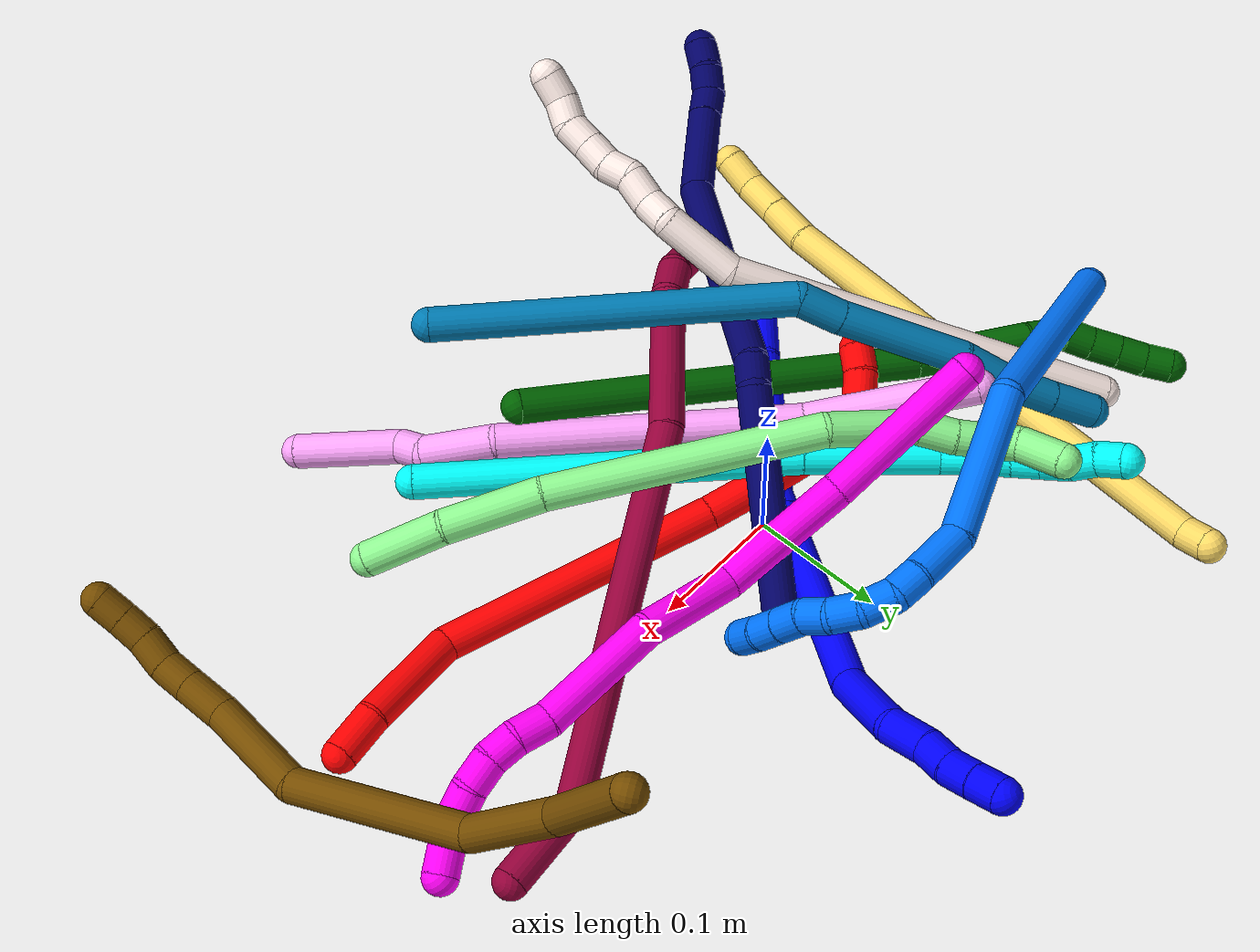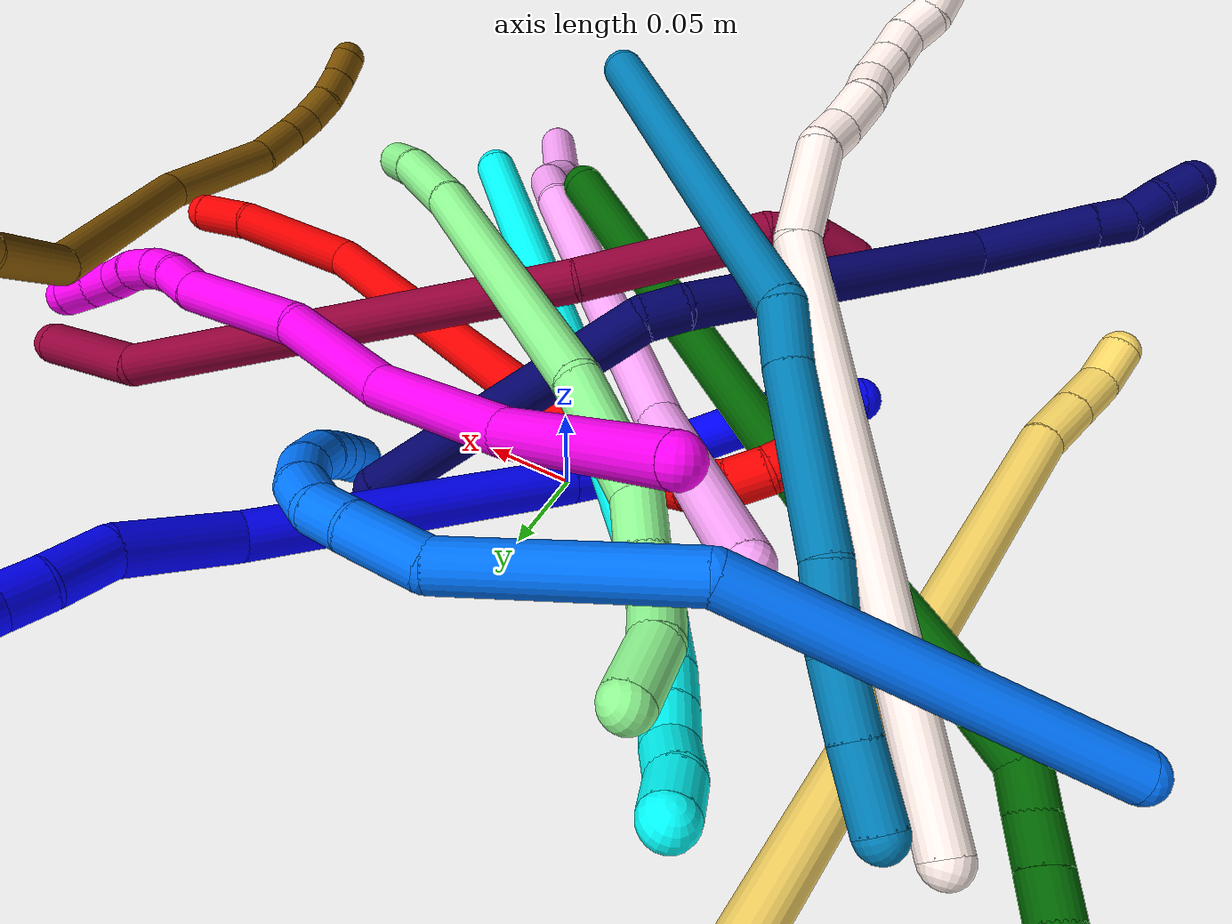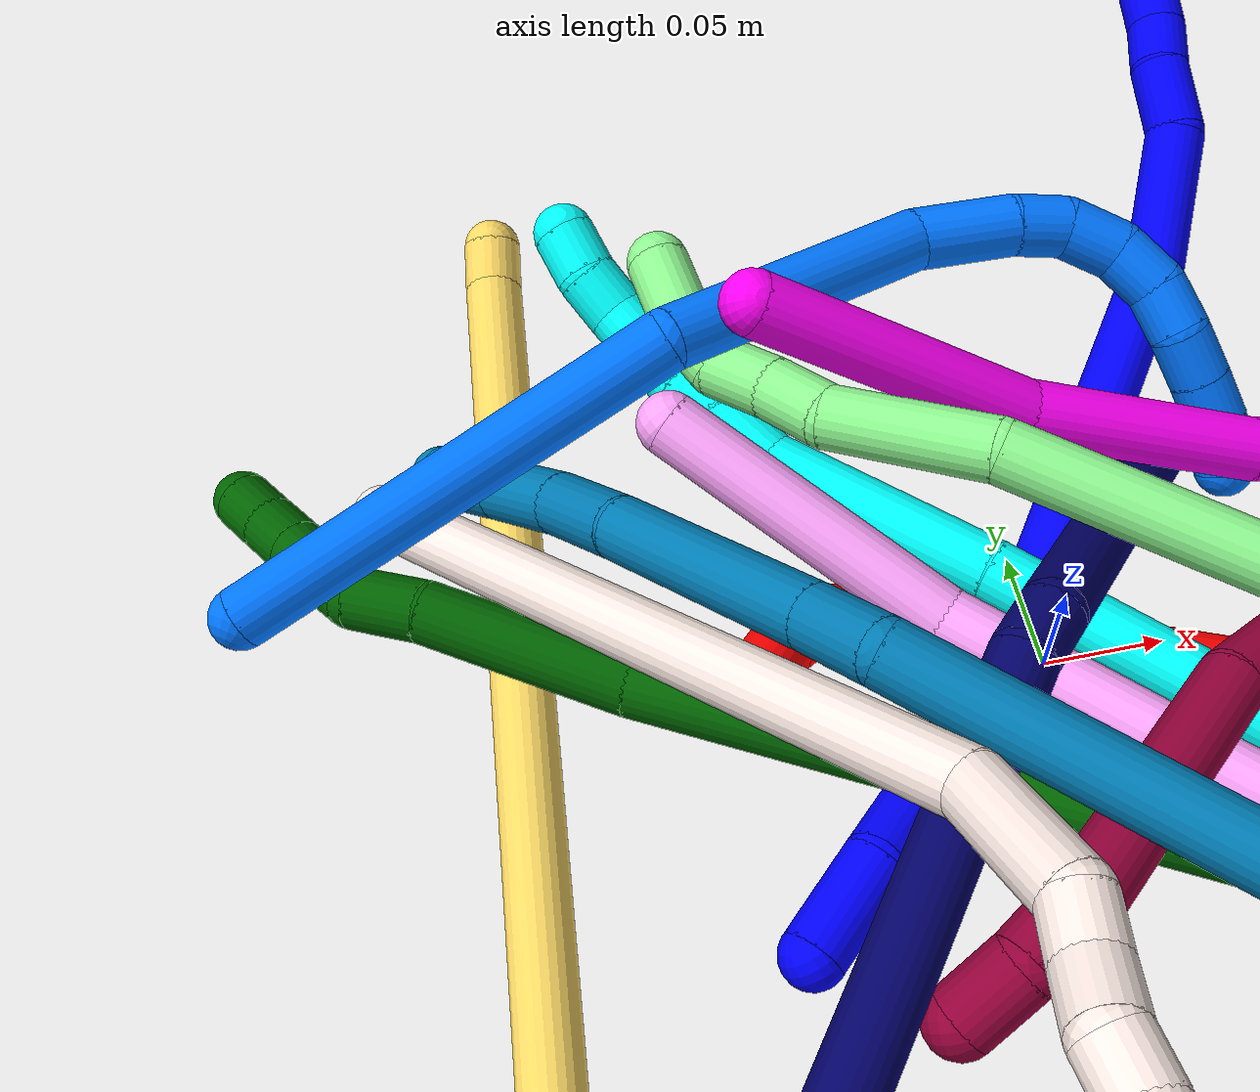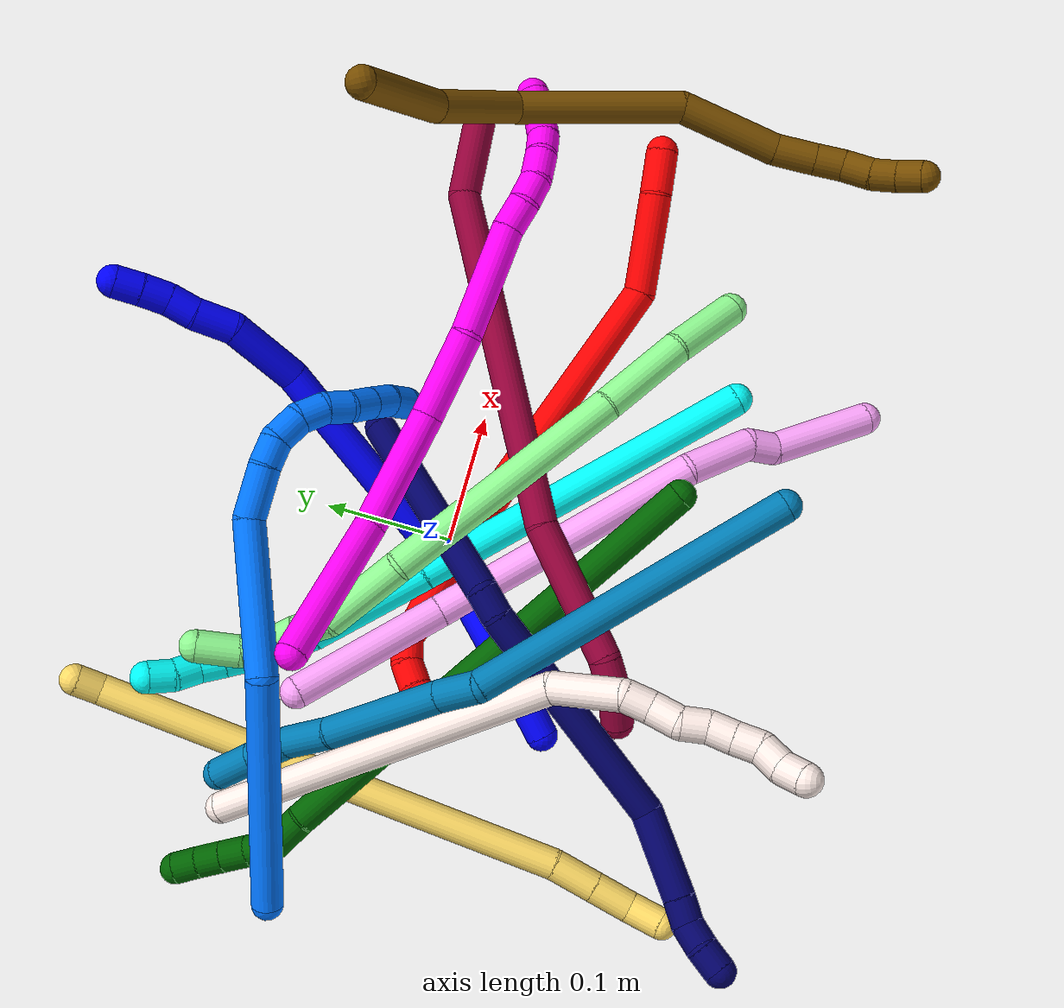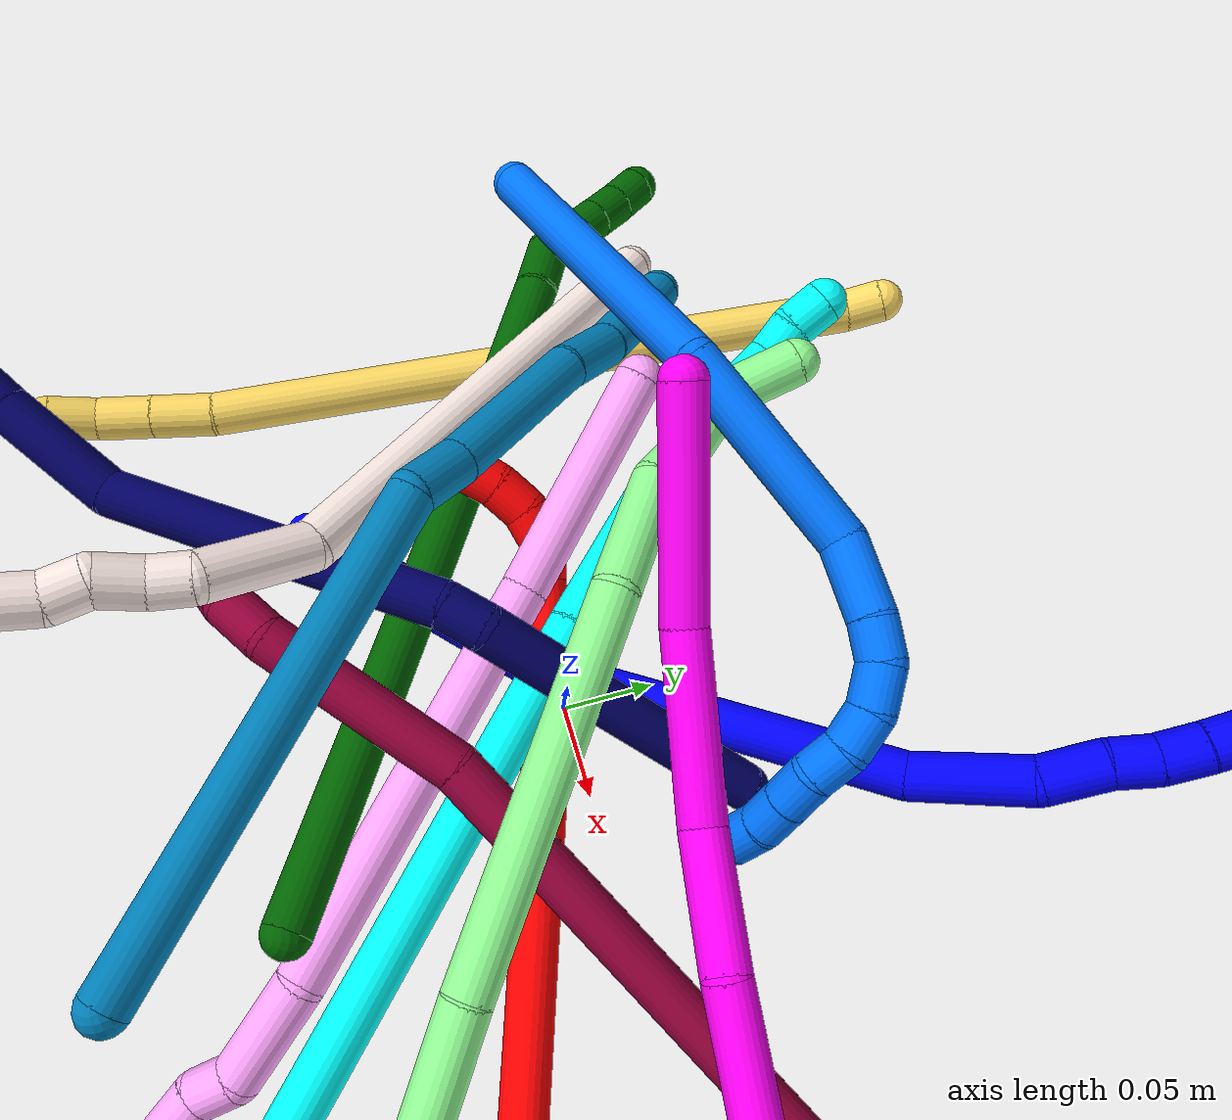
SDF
<sdf version="1.7">
 <world name="default">
  <plugin name="TubeGeneratorPlugin" filename="libtube_generator_plugin.so"/>
  <model name="photoneo_s_sensor">
   <static>1</static>
   <pose>0 0 2 1.57079 1.57079 3.14159</pose>
   <link name="link">
    <inertial><mass>0.1</mass></inertial>
    <sensor name="sensor" type="depth">
     <update_rate>30</update_rate>
     <camera>
      <horizontal_fov>1.22</horizontal_fov>
      <image><width>1920</width><height>1200</height><format>B8G8R8</format></image>
      <clip><near>0.1</near><far>4</far></clip>
      <depth_camera><output>points</output></depth_camera>
     </camera>
     <plugin name="camera_plugin" filename="libgazebo_ros_depth_camera.so">
      <baseline>0.2</baseline>
      <alwaysOn>1</alwaysOn>
      <updateRate>0.0</updateRate>
      <cameraName>camera_ir</cameraName>
      <imageTopicName>/camera/color/image_raw</imageTopicName>
      <cameraInfoTopicName>/camera/color/camera_info</cameraInfoTopicName>
      <depthImageTopicName>/camera/depth/image_raw</depthImageTopicName>
      <depthImageCameraInfoTopicName>/camera/depth/camera_info</depthImageCameraInfoTopicName>
      <pointCloudTopicName>/camera/depth/points</pointCloudTopicName>
      <frameName>fr_optical</frameName>
      <pointCloudCutoff>0.1</pointCloudCutoff>
      <pointCloudCutoffMax>2.0</pointCloudCutoffMax>
      <distortionK1>0</distortionK1>
      <distortionK2>0</distortionK2>
      <distortionK3>0</distortionK3>
      <distortionT1>0</distortionT1>
      <distortionT2>0</distortionT2>
      <CxPrime>0</CxPrime>
      <Cx>0</Cx>
      <Cy>0</Cy>
      <focalLength>0</focalLength>
      <hackBaseline>0</hackBaseline>
     </plugin>
    </sensor>
   </link>
  </model>
  <gravity>0 0 -9.8</gravity>
  <magnetic_field>6e-06 2.3e-05 -4.2e-05</magnetic_field>
  <atmosphere type="adiabatic"/>
  <physics name="default_physics" default="0" type="ode">
   <max_step_size>0.003</max_step_size>
   <real_time_factor>1</real_time_factor>
   <real_time_update_rate>1000</real_time_update_rate>
   <max_contacts>10000</max_contacts>
   <ode>
    <solver>
     <type>quick</type>
     <iters>100</iters>
     <sor>1.3</sor>
     <use_dynamic_moi_rescaling>0</use_dynamic_moi_rescaling>
    </solver>
    <constraints>
     <contact_max_correcting_vel>0</contact_max_correcting_vel>
     <contact_surface_layer>0.001</contact_surface_layer>
     <cfm>0</cfm>
     <erp>0.2</erp>
    </constraints>
   </ode>
  </physics>
  <scene><ambient>0.4 0.4 0.4 1</ambient><background>0.7 0.7 0.7 1</background><shadows>0</shadows></scene>
  <audio><device>default</device></audio>
  <spherical_coordinates>
   <surface_model>EARTH_WGS84</surface_model>
   <latitude_deg>0</latitude_deg>
   <longitude_deg>0</longitude_deg>
   <elevation>0</elevation>
   <heading_deg>0</heading_deg>
  </spherical_coordinates>
  <model name="bin">
   <static>1</static>
   <link name="bottom">
    <collision name="collision-bottom">
     <pose>0 0 -0.01 0 -0 0</pose>
     <geometry><box><size>0.8 0.6 0.02</size></box></geometry>
     <surface>
      <friction><ode><mu>100</mu><mu2>100</mu2></ode></friction>
      <contact><collide_bitmask>65535</collide_bitmask></contact>
     </surface>
    </collision>
   </link>
   <link name="west_wall">
    <collision name="collision-west_wall">
     <pose>-0.41 0 0.1 0 -0 0</pose>
     <geometry><box><size>0.02 0.6 0.2</size></box></geometry>
     <surface>
      <friction><ode><mu>100</mu><mu2>100</mu2></ode></friction>
      <contact><collide_bitmask>65535</collide_bitmask></contact>
     </surface>
    </collision>
   </link>
   <link name="east_wall">
    <collision name="collision-east_wall">
     <pose>0.41 0 0.1 0 -0 0</pose>
     <geometry><box><size>0.02 0.6 0.2</size></box></geometry>
     <surface>
      <friction><ode><mu>100</mu><mu2>100</mu2></ode></friction>
      <contact><collide_bitmask>65535</collide_bitmask></contact>
     </surface>
    </collision>
   </link>
   <link name="south_wall">
    <collision name="collision-south_wall">
     <pose>0 -0.31 0.1 0 -0 0</pose>
     <geometry><box><size>0.8 0.02 0.2</size></box></geometry>
     <surface>
      <friction><ode><mu>100</mu><mu2>100</mu2></ode></friction>
      <contact><collide_bitmask>65535</collide_bitmask></contact>
     </surface>
    </collision>
   </link>
   <link name="north_wall">
    <collision name="collision-north_wall">
     <pose>0 0.31 0.1 0 -0 0</pose>
     <geometry><box><size>0.8 0.02 0.2</size></box></geometry>
     <surface>
      <friction><ode><mu>100</mu><mu2>100</mu2></ode></friction>
      <contact><collide_bitmask>65535</collide_bitmask></contact>
     </surface>
    </collision>
   </link>
  </model>
  <model name="1">
   <static>0</static>
   <link name="1">
    <collision name="collision-cylinder-e_1_1_4">
     <pose>0.019754 0.003025 0.005488 -0.503782 1.2636 -0.372346</pose>
     <geometry><cylinder><radius>0.0125</radius><length>0.041448</length></cylinder></geometry>
     <surface>
      <friction><ode><mu>1.16</mu><mu2>1.16</mu2><slip1>0</slip1><slip2>0</slip2></ode></friction>
      <contact><ode><kp>1e+06</kp><kd>1</kd><max_vel>0</max_vel><min_depth>0.001</min_depth></ode></contact>
     </surface>
    </collision>
    <visual name="visual-cylinder-e_1_1_4">
     <pose>0.019754 0.003025 0.005488 -0.503782 1.2636 -0.372346</pose>
     <geometry><cylinder><radius>0.0125</radius><length>0.041448</length></cylinder></geometry>
     <material><ambient>0 0 1 1</ambient></material>
    </visual>
    <collision name="collision-cylinder-e_2_4_5">
     <pose>0.089437 0.027794 0.017007 -1.30024 1.14635 -0.91252</pose>
     <geometry><cylinder><radius>0.0125</radius><length>0.109583</length></cylinder></geometry>
     <surface>
      <friction><ode><mu>1.16</mu><mu2>1.16</mu2><slip1>0</slip1><slip2>0</slip2></ode></friction>
      <contact><ode><kp>1e+06</kp><kd>1</kd><max_vel>0</max_vel><min_depth>0.001</min_depth></ode></contact>
     </surface>
    </collision>
    <visual name="visual-cylinder-e_2_4_5">
     <pose>0.089437 0.027794 0.017007 -1.30024 1.14635 -0.91252</pose>
     <geometry><cylinder><radius>0.0125</radius><length>0.109583</length></cylinder></geometry>
     <material><ambient>0 0 1 1</ambient></material>
    </visual>
    <collision name="collision-cylinder-e_3_5_6">
     <pose>0.148236 0.051377 0.027967 -0.357334 1.03531 -0.204957</pose>
     <geometry><cylinder><radius>0.0125</radius><length>0.020624</length></cylinder></geometry>
     <surface>
      <friction><ode><mu>1.16</mu><mu2>1.16</mu2><slip1>0</slip1><slip2>0</slip2></ode></friction>
      <contact><ode><kp>1e+06</kp><kd>1</kd><max_vel>0</max_vel><min_depth>0.001</min_depth></ode></contact>
     </surface>
    </collision>
    <visual name="visual-cylinder-e_3_5_6">
     <pose>0.148236 0.051377 0.027967 -0.357334 1.03531 -0.204957</pose>
     <geometry><cylinder><radius>0.0125</radius><length>0.020624</length></cylinder></geometry>
     <material><ambient>0 0 1 1</ambient></material>
    </visual>
    <collision name="collision-cylinder-e_4_6_7">
     <pose>0.231754 0.065924 0.074902 -0.293728 1.03933 -0.168864</pose>
     <geometry><cylinder><radius>0.0125</radius><length>0.173188</length></cylinder></geometry>
     <surface>
      <friction><ode><mu>1.16</mu><mu2>1.16</mu2><slip1>0</slip1><slip2>0</slip2></ode></friction>
      <contact><ode><kp>1e+06</kp><kd>1</kd><max_vel>0</max_vel><min_depth>0.001</min_depth></ode></contact>
     </surface>
    </collision>
    <visual name="visual-cylinder-e_4_6_7">
     <pose>0.231754 0.065924 0.074902 -0.293728 1.03933 -0.168864</pose>
     <geometry><cylinder><radius>0.0125</radius><length>0.173188</length></cylinder></geometry>
     <material><ambient>0 0 1 1</ambient></material>
    </visual>
    <collision name="collision-cylinder-e_5_7_8">
     <pose>0.327058 0.078996 0.138964 -0.016615 0.752531 -0.006564</pose>
     <geometry><cylinder><radius>0.0125</radius><length>0.060438</length></cylinder></geometry>
     <surface>
      <friction><ode><mu>1.16</mu><mu2>1.16</mu2><slip1>0</slip1><slip2>0</slip2></ode></friction>
      <contact><ode><kp>1e+06</kp><kd>1</kd><max_vel>0</max_vel><min_depth>0.001</min_depth></ode></contact>
     </surface>
    </collision>
    <visual name="visual-cylinder-e_5_7_8">
     <pose>0.327058 0.078996 0.138964 -0.016615 0.752531 -0.006564</pose>
     <geometry><cylinder><radius>0.0125</radius><length>0.060438</length></cylinder></geometry>
     <material><ambient>0 0 1 1</ambient></material>
    </visual>
    <collision name="collision-cylinder-e_6_8_9">
     <pose>0.355109 0.083847 0.174087 -0.330587 0.491545 -0.08364</pose>
     <geometry><cylinder><radius>0.0125</radius><length>0.031343</length></cylinder></geometry>
     <surface>
      <friction><ode><mu>1.16</mu><mu2>1.16</mu2><slip1>0</slip1><slip2>0</slip2></ode></friction>
      <contact><ode><kp>1e+06</kp><kd>1</kd><max_vel>0</max_vel><min_depth>0.001</min_depth></ode></contact>
     </surface>
    </collision>
    <visual name="visual-cylinder-e_6_8_9">
     <pose>0.355109 0.083847 0.174087 -0.330587 0.491545 -0.08364</pose>
     <geometry><cylinder><radius>0.0125</radius><length>0.031343</length></cylinder></geometry>
     <material><ambient>0 0 1 1</ambient></material>
    </visual>
    <collision name="collision-cylinder-e_7_9_10">
     <pose>0.369153 0.09164 0.194892 -0.40403 0.668602 -0.142036</pose>
     <geometry><cylinder><radius>0.0125</radius><length>0.021446</length></cylinder></geometry>
     <surface>
      <friction><ode><mu>1.16</mu><mu2>1.16</mu2><slip1>0</slip1><slip2>0</slip2></ode></friction>
      <contact><ode><kp>1e+06</kp><kd>1</kd><max_vel>0</max_vel><min_depth>0.001</min_depth></ode></contact>
     </surface>
    </collision>
    <visual name="visual-cylinder-e_7_9_10">
     <pose>0.369153 0.09164 0.194892 -0.40403 0.668602 -0.142036</pose>
     <geometry><cylinder><radius>0.0125</radius><length>0.021446</length></cylinder></geometry>
     <material><ambient>0 0 1 1</ambient></material>
    </visual>
    <collision name="collision-cylinder-e_8_10_11">
     <pose>0.38071 0.097789 0.211689 -0.303925 0.477233 -0.07447</pose>
     <geometry><cylinder><radius>0.0125</radius><length>0.021379</length></cylinder></geometry>
     <surface>
      <friction><ode><mu>1.16</mu><mu2>1.16</mu2><slip1>0</slip1><slip2>0</slip2></ode></friction>
      <contact><ode><kp>1e+06</kp><kd>1</kd><max_vel>0</max_vel><min_depth>0.001</min_depth></ode></contact>
     </surface>
    </collision>
    <visual name="visual-cylinder-e_8_10_11">
     <pose>0.38071 0.097789 0.211689 -0.303925 0.477233 -0.07447</pose>
     <geometry><cylinder><radius>0.0125</radius><length>0.021379</length></cylinder></geometry>
     <material><ambient>0 0 1 1</ambient></material>
    </visual>
    <collision name="collision-cylinder-e_9_11_2">
     <pose>0.389957 0.103954 0.229451 -0.364834 0.435678 -0.081619</pose>
     <geometry><cylinder><radius>0.0125</radius><length>0.02055</length></cylinder></geometry>
     <surface>
      <friction><ode><mu>1.16</mu><mu2>1.16</mu2><slip1>0</slip1><slip2>0</slip2></ode></friction>
      <contact><ode><kp>1e+06</kp><kd>1</kd><max_vel>0</max_vel><min_depth>0.001</min_depth></ode></contact>
     </surface>
    </collision>
    <visual name="visual-cylinder-e_9_11_2">
     <pose>0.389957 0.103954 0.229451 -0.364834 0.435678 -0.081619</pose>
     <geometry><cylinder><radius>0.0125</radius><length>0.02055</length></cylinder></geometry>
     <material><ambient>0 0 1 1</ambient></material>
    </visual>
    <collision name="collision-sphere-2">
     <pose>0.394293 0.107278 0.238153 0 -0 0</pose>
     <geometry><sphere><radius>0.0125</radius></sphere></geometry>
     <surface>
      <friction><ode><mu>1.16</mu><mu2>1.16</mu2><slip1>0</slip1><slip2>0</slip2></ode></friction>
      <contact><ode><kp>1e+06</kp><kd>1</kd><max_vel>0</max_vel><min_depth>0.001</min_depth></ode></contact>
     </surface>
    </collision>
    <visual name="visual-sphere-2">
     <pose>0.394293 0.107278 0.238153 0 -0 0</pose>
     <geometry><sphere><radius>0.0125</radius></sphere></geometry>
     <material><ambient>0 0 1 1</ambient></material>
    </visual>
    <collision name="collision-sphere-11">
     <pose>0.38562 0.100631 0.220749 0 -0 0</pose>
     <geometry><sphere><radius>0.0125</radius></sphere></geometry>
     <surface>
      <friction><ode><mu>1.16</mu><mu2>1.16</mu2><slip1>0</slip1><slip2>0</slip2></ode></friction>
      <contact><ode><kp>1e+06</kp><kd>1</kd><max_vel>0</max_vel><min_depth>0.001</min_depth></ode></contact>
     </surface>
    </collision>
    <visual name="visual-sphere-11">
     <pose>0.38562 0.100631 0.220749 0 -0 0</pose>
     <geometry><sphere><radius>0.0125</radius></sphere></geometry>
     <material><ambient>0 0 1 1</ambient></material>
    </visual>
    <collision name="collision-sphere-10">
     <pose>0.3758 0.094947 0.202629 0 -0 0</pose>
     <geometry><sphere><radius>0.0125</radius></sphere></geometry>
     <surface>
      <friction><ode><mu>1.16</mu><mu2>1.16</mu2><slip1>0</slip1><slip2>0</slip2></ode></friction>
      <contact><ode><kp>1e+06</kp><kd>1</kd><max_vel>0</max_vel><min_depth>0.001</min_depth></ode></contact>
     </surface>
    </collision>
    <visual name="visual-sphere-10">
     <pose>0.3758 0.094947 0.202629 0 -0 0</pose>
     <geometry><sphere><radius>0.0125</radius></sphere></geometry>
     <material><ambient>0 0 1 1</ambient></material>
    </visual>
    <collision name="collision-sphere-9">
     <pose>0.362506 0.088332 0.187155 0 -0 0</pose>
     <geometry><sphere><radius>0.0125</radius></sphere></geometry>
     <surface>
      <friction><ode><mu>1.16</mu><mu2>1.16</mu2><slip1>0</slip1><slip2>0</slip2></ode></friction>
      <contact><ode><kp>1e+06</kp><kd>1</kd><max_vel>0</max_vel><min_depth>0.001</min_depth></ode></contact>
     </surface>
    </collision>
    <visual name="visual-sphere-9">
     <pose>0.362506 0.088332 0.187155 0 -0 0</pose>
     <geometry><sphere><radius>0.0125</radius></sphere></geometry>
     <material><ambient>0 0 1 1</ambient></material>
    </visual>
    <collision name="collision-sphere-4">
     <pose>0.039508 0.00605 0.010976 0 -0 0</pose>
     <geometry><sphere><radius>0.0125</radius></sphere></geometry>
     <surface>
      <friction><ode><mu>1.16</mu><mu2>1.16</mu2><slip1>0</slip1><slip2>0</slip2></ode></friction>
      <contact><ode><kp>1e+06</kp><kd>1</kd><max_vel>0</max_vel><min_depth>0.001</min_depth></ode></contact>
     </surface>
    </collision>
    <visual name="visual-sphere-4">
     <pose>0.039508 0.00605 0.010976 0 -0 0</pose>
     <geometry><sphere><radius>0.0125</radius></sphere></geometry>
     <material><ambient>0 0 1 1</ambient></material>
    </visual>
    <collision name="collision-sphere-1">
     <geometry><sphere><radius>0.0125</radius></sphere></geometry>
     <surface>
      <friction><ode><mu>1.16</mu><mu2>1.16</mu2><slip1>0</slip1><slip2>0</slip2></ode></friction>
      <contact><ode><kp>1e+06</kp><kd>1</kd><max_vel>0</max_vel><min_depth>0.001</min_depth></ode></contact>
     </surface>
    </collision>
    <visual name="visual-sphere-1">
     <geometry><sphere><radius>0.0125</radius></sphere></geometry>
     <material><ambient>0 0 1 1</ambient></material>
    </visual>
    <collision name="collision-sphere-8">
     <pose>0.347713 0.079362 0.161019 0 -0 0</pose>
     <geometry><sphere><radius>0.0125</radius></sphere></geometry>
     <surface>
      <friction><ode><mu>1.16</mu><mu2>1.16</mu2><slip1>0</slip1><slip2>0</slip2></ode></friction>
      <contact><ode><kp>1e+06</kp><kd>1</kd><max_vel>0</max_vel><min_depth>0.001</min_depth></ode></contact>
     </surface>
    </collision>
    <visual name="visual-sphere-8">
     <pose>0.347713 0.079362 0.161019 0 -0 0</pose>
     <geometry><sphere><radius>0.0125</radius></sphere></geometry>
     <material><ambient>0 0 1 1</ambient></material>
    </visual>
    <collision name="collision-sphere-5">
     <pose>0.139367 0.049537 0.023038 0 -0 0</pose>
     <geometry><sphere><radius>0.0125</radius></sphere></geometry>
     <surface>
      <friction><ode><mu>1.16</mu><mu2>1.16</mu2><slip1>0</slip1><slip2>0</slip2></ode></friction>
      <contact><ode><kp>1e+06</kp><kd>1</kd><max_vel>0</max_vel><min_depth>0.001</min_depth></ode></contact>
     </surface>
    </collision>
    <visual name="visual-sphere-5">
     <pose>0.139367 0.049537 0.023038 0 -0 0</pose>
     <geometry><sphere><radius>0.0125</radius></sphere></geometry>
     <material><ambient>0 0 1 1</ambient></material>
    </visual>
    <collision name="collision-sphere-6">
     <pose>0.157104 0.053218 0.032897 0 -0 0</pose>
     <geometry><sphere><radius>0.0125</radius></sphere></geometry>
     <surface>
      <friction><ode><mu>1.16</mu><mu2>1.16</mu2><slip1>0</slip1><slip2>0</slip2></ode></friction>
      <contact><ode><kp>1e+06</kp><kd>1</kd><max_vel>0</max_vel><min_depth>0.001</min_depth></ode></contact>
     </surface>
    </collision>
    <visual name="visual-sphere-6">
     <pose>0.157104 0.053218 0.032897 0 -0 0</pose>
     <geometry><sphere><radius>0.0125</radius></sphere></geometry>
     <material><ambient>0 0 1 1</ambient></material>
    </visual>
    <collision name="collision-sphere-7">
     <pose>0.306404 0.078629 0.116908 0 -0 0</pose>
     <geometry><sphere><radius>0.0125</radius></sphere></geometry>
     <surface>
      <friction><ode><mu>1.16</mu><mu2>1.16</mu2><slip1>0</slip1><slip2>0</slip2></ode></friction>
      <contact><ode><kp>1e+06</kp><kd>1</kd><max_vel>0</max_vel><min_depth>0.001</min_depth></ode></contact>
     </surface>
    </collision>
    <visual name="visual-sphere-7">
     <pose>0.306404 0.078629 0.116908 0 -0 0</pose>
     <geometry><sphere><radius>0.0125</radius></sphere></geometry>
     <material><ambient>0 0 1 1</ambient></material>
    </visual>
    <inertial>
     <pose>0.217561 0.058485 0.085832 0 -0 0</pose>
     <mass>0.5</mass>
     <inertia>
      <ixx>0.000228</ixx>
      <ixy>0</ixy>
      <ixz>0</ixz>
      <iyy>0.000501</iyy>
      <iyz>0</iyz>
      <izz>-0.000605</izz>
     </inertia>
    </inertial>
   </link>
   <pose>-0.124781 -0.110402 0.03111 -0.897436 -0.033526 0.450251</pose>
  </model>
  <model name="2">
   <static>0</static>
   <link name="2">
    <collision name="collision-cylinder-e_1_1_4">
     <pose>-0.013684 0.004619 0.009258 -0.462796 -0.923393 0.233405</pose>
     <geometry><cylinder><radius>0.0125</radius><length>0.034311</length></cylinder></geometry>
     <surface>
      <friction><ode><mu>1.16</mu><mu2>1.16</mu2><slip1>0</slip1><slip2>0</slip2></ode></friction>
      <contact><ode><kp>1e+06</kp><kd>1</kd><max_vel>0</max_vel><min_depth>0.001</min_depth></ode></contact>
     </surface>
    </collision>
    <visual name="visual-cylinder-e_1_1_4">
     <pose>-0.013684 0.004619 0.009258 -0.462796 -0.923393 0.233405</pose>
     <geometry><cylinder><radius>0.0125</radius><length>0.034311</length></cylinder></geometry>
     <material><ambient>1 0 0 1</ambient></material>
    </visual>
    <collision name="collision-cylinder-e_2_4_5">
     <pose>-0.054428 0.016309 0.045211 -0.258907 -0.775246 0.106201</pose>
     <geometry><cylinder><radius>0.0125</radius><length>0.077327</length></cylinder></geometry>
     <surface>
      <friction><ode><mu>1.16</mu><mu2>1.16</mu2><slip1>0</slip1><slip2>0</slip2></ode></friction>
      <contact><ode><kp>1e+06</kp><kd>1</kd><max_vel>0</max_vel><min_depth>0.001</min_depth></ode></contact>
     </surface>
    </collision>
    <visual name="visual-cylinder-e_2_4_5">
     <pose>-0.054428 0.016309 0.045211 -0.258907 -0.775246 0.106201</pose>
     <geometry><cylinder><radius>0.0125</radius><length>0.077327</length></cylinder></geometry>
     <material><ambient>1 0 0 1</ambient></material>
    </visual>
    <collision name="collision-cylinder-e_3_5_6">
     <pose>-0.175763 0.008448 0.110957 0.365194 -1.15339 -0.239072</pose>
     <geometry><cylinder><radius>0.0125</radius><length>0.206258</length></cylinder></geometry>
     <surface>
      <friction><ode><mu>1.16</mu><mu2>1.16</mu2><slip1>0</slip1><slip2>0</slip2></ode></friction>
      <contact><ode><kp>1e+06</kp><kd>1</kd><max_vel>0</max_vel><min_depth>0.001</min_depth></ode></contact>
     </surface>
    </collision>
    <visual name="visual-cylinder-e_3_5_6">
     <pose>-0.175763 0.008448 0.110957 0.365194 -1.15339 -0.239072</pose>
     <geometry><cylinder><radius>0.0125</radius><length>0.206258</length></cylinder></geometry>
     <material><ambient>1 0 0 1</ambient></material>
    </visual>
    <collision name="collision-cylinder-e_4_6_7">
     <pose>-0.29113 -0.008798 0.157003 0.319664 -1.2347 -0.227895</pose>
     <geometry><cylinder><radius>0.0125</radius><length>0.044685</length></cylinder></geometry>
     <surface>
      <friction><ode><mu>1.16</mu><mu2>1.16</mu2><slip1>0</slip1><slip2>0</slip2></ode></friction>
      <contact><ode><kp>1e+06</kp><kd>1</kd><max_vel>0</max_vel><min_depth>0.001</min_depth></ode></contact>
     </surface>
    </collision>
    <visual name="visual-cylinder-e_4_6_7">
     <pose>-0.29113 -0.008798 0.157003 0.319664 -1.2347 -0.227895</pose>
     <geometry><cylinder><radius>0.0125</radius><length>0.044685</length></cylinder></geometry>
     <material><ambient>1 0 0 1</ambient></material>
    </visual>
    <collision name="collision-cylinder-e_5_7_8">
     <pose>-0.337468 -0.012683 0.176971 0.120362 -1.09317 -0.073286</pose>
     <geometry><cylinder><radius>0.0125</radius><length>0.056854</length></cylinder></geometry>
     <surface>
      <friction><ode><mu>1.16</mu><mu2>1.16</mu2><slip1>0</slip1><slip2>0</slip2></ode></friction>
      <contact><ode><kp>1e+06</kp><kd>1</kd><max_vel>0</max_vel><min_depth>0.001</min_depth></ode></contact>
     </surface>
    </collision>
    <visual name="visual-cylinder-e_5_7_8">
     <pose>-0.337468 -0.012683 0.176971 0.120362 -1.09317 -0.073286</pose>
     <geometry><cylinder><radius>0.0125</radius><length>0.056854</length></cylinder></geometry>
     <material><ambient>1 0 0 1</ambient></material>
    </visual>
    <collision name="collision-cylinder-e_6_8_9">
     <pose>-0.372774 -0.013339 0.190287 -1.21094 -1.47416 1.12199</pose>
     <geometry><cylinder><radius>0.0125</radius><length>0.020214</length></cylinder></geometry>
     <surface>
      <friction><ode><mu>1.16</mu><mu2>1.16</mu2><slip1>0</slip1><slip2>0</slip2></ode></friction>
      <contact><ode><kp>1e+06</kp><kd>1</kd><max_vel>0</max_vel><min_depth>0.001</min_depth></ode></contact>
     </surface>
    </collision>
    <visual name="visual-cylinder-e_6_8_9">
     <pose>-0.372774 -0.013339 0.190287 -1.21094 -1.47416 1.12199</pose>
     <geometry><cylinder><radius>0.0125</radius><length>0.020214</length></cylinder></geometry>
     <material><ambient>1 0 0 1</ambient></material>
    </visual>
    <collision name="collision-cylinder-e_7_9_10">
     <pose>-0.391137 -0.007131 0.193185 -1.12132 -0.954681 0.628024</pose>
     <geometry><cylinder><radius>0.0125</radius><length>0.020347</length></cylinder></geometry>
     <surface>
      <friction><ode><mu>1.16</mu><mu2>1.16</mu2><slip1>0</slip1><slip2>0</slip2></ode></friction>
      <contact><ode><kp>1e+06</kp><kd>1</kd><max_vel>0</max_vel><min_depth>0.001</min_depth></ode></contact>
     </surface>
    </collision>
    <visual name="visual-cylinder-e_7_9_10">
     <pose>-0.391137 -0.007131 0.193185 -1.12132 -0.954681 0.628024</pose>
     <geometry><cylinder><radius>0.0125</radius><length>0.020347</length></cylinder></geometry>
     <material><ambient>1 0 0 1</ambient></material>
    </visual>
    <collision name="collision-cylinder-e_8_10_11">
     <pose>-0.405232 0.005666 0.198928 -1.16892 -0.617779 0.416105</pose>
     <geometry><cylinder><radius>0.0125</radius><length>0.02</length></cylinder></geometry>
     <surface>
      <friction><ode><mu>1.16</mu><mu2>1.16</mu2><slip1>0</slip1><slip2>0</slip2></ode></friction>
      <contact><ode><kp>1e+06</kp><kd>1</kd><max_vel>0</max_vel><min_depth>0.001</min_depth></ode></contact>
     </surface>
    </collision>
    <visual name="visual-cylinder-e_8_10_11">
     <pose>-0.405232 0.005666 0.198928 -1.16892 -0.617779 0.416105</pose>
     <geometry><cylinder><radius>0.0125</radius><length>0.02</length></cylinder></geometry>
     <material><ambient>1 0 0 1</ambient></material>
    </visual>
    <collision name="collision-cylinder-e_9_11_2">
     <pose>-0.41481 0.021654 0.205819 -1.15931 -0.388135 0.255936</pose>
     <geometry><cylinder><radius>0.0125</radius><length>0.020004</length></cylinder></geometry>
     <surface>
      <friction><ode><mu>1.16</mu><mu2>1.16</mu2><slip1>0</slip1><slip2>0</slip2></ode></friction>
      <contact><ode><kp>1e+06</kp><kd>1</kd><max_vel>0</max_vel><min_depth>0.001</min_depth></ode></contact>
     </surface>
    </collision>
    <visual name="visual-cylinder-e_9_11_2">
     <pose>-0.41481 0.021654 0.205819 -1.15931 -0.388135 0.255936</pose>
     <geometry><cylinder><radius>0.0125</radius><length>0.020004</length></cylinder></geometry>
     <material><ambient>1 0 0 1</ambient></material>
    </visual>
    <collision name="collision-sphere-2">
     <pose>-0.418595 0.030139 0.209522 0 -0 0</pose>
     <geometry><sphere><radius>0.0125</radius></sphere></geometry>
     <surface>
      <friction><ode><mu>1.16</mu><mu2>1.16</mu2><slip1>0</slip1><slip2>0</slip2></ode></friction>
      <contact><ode><kp>1e+06</kp><kd>1</kd><max_vel>0</max_vel><min_depth>0.001</min_depth></ode></contact>
     </surface>
    </collision>
    <visual name="visual-sphere-2">
     <pose>-0.418595 0.030139 0.209522 0 -0 0</pose>
     <geometry><sphere><radius>0.0125</radius></sphere></geometry>
     <material><ambient>1 0 0 1</ambient></material>
    </visual>
    <collision name="collision-sphere-11">
     <pose>-0.411024 0.013169 0.202117 0 -0 0</pose>
     <geometry><sphere><radius>0.0125</radius></sphere></geometry>
     <surface>
      <friction><ode><mu>1.16</mu><mu2>1.16</mu2><slip1>0</slip1><slip2>0</slip2></ode></friction>
      <contact><ode><kp>1e+06</kp><kd>1</kd><max_vel>0</max_vel><min_depth>0.001</min_depth></ode></contact>
     </surface>
    </collision>
    <visual name="visual-sphere-11">
     <pose>-0.411024 0.013169 0.202117 0 -0 0</pose>
     <geometry><sphere><radius>0.0125</radius></sphere></geometry>
     <material><ambient>1 0 0 1</ambient></material>
    </visual>
    <collision name="collision-sphere-10">
     <pose>-0.39944 -0.001836 0.19574 0 -0 0</pose>
     <geometry><sphere><radius>0.0125</radius></sphere></geometry>
     <surface>
      <friction><ode><mu>1.16</mu><mu2>1.16</mu2><slip1>0</slip1><slip2>0</slip2></ode></friction>
      <contact><ode><kp>1e+06</kp><kd>1</kd><max_vel>0</max_vel><min_depth>0.001</min_depth></ode></contact>
     </surface>
    </collision>
    <visual name="visual-sphere-10">
     <pose>-0.39944 -0.001836 0.19574 0 -0 0</pose>
     <geometry><sphere><radius>0.0125</radius></sphere></geometry>
     <material><ambient>1 0 0 1</ambient></material>
    </visual>
    <collision name="collision-sphere-9">
     <pose>-0.382833 -0.012426 0.190631 0 -0 0</pose>
     <geometry><sphere><radius>0.0125</radius></sphere></geometry>
     <surface>
      <friction><ode><mu>1.16</mu><mu2>1.16</mu2><slip1>0</slip1><slip2>0</slip2></ode></friction>
      <contact><ode><kp>1e+06</kp><kd>1</kd><max_vel>0</max_vel><min_depth>0.001</min_depth></ode></contact>
     </surface>
    </collision>
    <visual name="visual-sphere-9">
     <pose>-0.382833 -0.012426 0.190631 0 -0 0</pose>
     <geometry><sphere><radius>0.0125</radius></sphere></geometry>
     <material><ambient>1 0 0 1</ambient></material>
    </visual>
    <collision name="collision-sphere-4">
     <pose>-0.027368 0.009239 0.018517 0 -0 0</pose>
     <geometry><sphere><radius>0.0125</radius></sphere></geometry>
     <surface>
      <friction><ode><mu>1.16</mu><mu2>1.16</mu2><slip1>0</slip1><slip2>0</slip2></ode></friction>
      <contact><ode><kp>1e+06</kp><kd>1</kd><max_vel>0</max_vel><min_depth>0.001</min_depth></ode></contact>
     </surface>
    </collision>
    <visual name="visual-sphere-4">
     <pose>-0.027368 0.009239 0.018517 0 -0 0</pose>
     <geometry><sphere><radius>0.0125</radius></sphere></geometry>
     <material><ambient>1 0 0 1</ambient></material>
    </visual>
    <collision name="collision-sphere-1">
     <geometry><sphere><radius>0.0125</radius></sphere></geometry>
     <surface>
      <friction><ode><mu>1.16</mu><mu2>1.16</mu2><slip1>0</slip1><slip2>0</slip2></ode></friction>
      <contact><ode><kp>1e+06</kp><kd>1</kd><max_vel>0</max_vel><min_depth>0.001</min_depth></ode></contact>
     </surface>
    </collision>
    <visual name="visual-sphere-1">
     <geometry><sphere><radius>0.0125</radius></sphere></geometry>
     <material><ambient>1 0 0 1</ambient></material>
    </visual>
    <collision name="collision-sphere-8">
     <pose>-0.362714 -0.014252 0.189944 0 -0 0</pose>
     <geometry><sphere><radius>0.0125</radius></sphere></geometry>
     <surface>
      <friction><ode><mu>1.16</mu><mu2>1.16</mu2><slip1>0</slip1><slip2>0</slip2></ode></friction>
      <contact><ode><kp>1e+06</kp><kd>1</kd><max_vel>0</max_vel><min_depth>0.001</min_depth></ode></contact>
     </surface>
    </collision>
    <visual name="visual-sphere-8">
     <pose>-0.362714 -0.014252 0.189944 0 -0 0</pose>
     <geometry><sphere><radius>0.0125</radius></sphere></geometry>
     <material><ambient>1 0 0 1</ambient></material>
    </visual>
    <collision name="collision-sphere-5">
     <pose>-0.081488 0.023379 0.071906 0 -0 0</pose>
     <geometry><sphere><radius>0.0125</radius></sphere></geometry>
     <surface>
      <friction><ode><mu>1.16</mu><mu2>1.16</mu2><slip1>0</slip1><slip2>0</slip2></ode></friction>
      <contact><ode><kp>1e+06</kp><kd>1</kd><max_vel>0</max_vel><min_depth>0.001</min_depth></ode></contact>
     </surface>
    </collision>
    <visual name="visual-sphere-5">
     <pose>-0.081488 0.023379 0.071906 0 -0 0</pose>
     <geometry><sphere><radius>0.0125</radius></sphere></geometry>
     <material><ambient>1 0 0 1</ambient></material>
    </visual>
    <collision name="collision-sphere-6">
     <pose>-0.270038 -0.006483 0.150008 0 -0 0</pose>
     <geometry><sphere><radius>0.0125</radius></sphere></geometry>
     <surface>
      <friction><ode><mu>1.16</mu><mu2>1.16</mu2><slip1>0</slip1><slip2>0</slip2></ode></friction>
      <contact><ode><kp>1e+06</kp><kd>1</kd><max_vel>0</max_vel><min_depth>0.001</min_depth></ode></contact>
     </surface>
    </collision>
    <visual name="visual-sphere-6">
     <pose>-0.270038 -0.006483 0.150008 0 -0 0</pose>
     <geometry><sphere><radius>0.0125</radius></sphere></geometry>
     <material><ambient>1 0 0 1</ambient></material>
    </visual>
    <collision name="collision-sphere-7">
     <pose>-0.312222 -0.011114 0.163999 0 -0 0</pose>
     <geometry><sphere><radius>0.0125</radius></sphere></geometry>
     <surface>
      <friction><ode><mu>1.16</mu><mu2>1.16</mu2><slip1>0</slip1><slip2>0</slip2></ode></friction>
      <contact><ode><kp>1e+06</kp><kd>1</kd><max_vel>0</max_vel><min_depth>0.001</min_depth></ode></contact>
     </surface>
    </collision>
    <visual name="visual-sphere-7">
     <pose>-0.312222 -0.011114 0.163999 0 -0 0</pose>
     <geometry><sphere><radius>0.0125</radius></sphere></geometry>
     <material><ambient>1 0 0 1</ambient></material>
    </visual>
    <inertial>
     <pose>-0.210046 0.004359 0.1193 0 -0 0</pose>
     <mass>0.5</mass>
     <inertia>
      <ixx>0.000238</ixx>
      <ixy>0</ixy>
      <ixz>0</ixz>
      <iyy>0.000739</iyy>
      <iyz>0</iyz>
      <izz>0.00085</izz>
     </inertia>
    </inertial>
   </link>
   <pose>0.338247 -0.076214 0.020033 2.6486 0.492235 -0.390696</pose>
  </model>
  <model name="3">
   <static>0</static>
   <link name="3">
    <collision name="collision-cylinder-e_1_1_4">
     <pose>-0.044812 0.126976 0.019544 -1.41808 -0.335616 0.288624</pose>
     <geometry><cylinder><radius>0.0125</radius><length>0.272125</length></cylinder></geometry>
     <surface>
      <friction><ode><mu>1.16</mu><mu2>1.16</mu2><slip1>0</slip1><slip2>0</slip2></ode></friction>
      <contact><ode><kp>1e+06</kp><kd>1</kd><max_vel>0</max_vel><min_depth>0.001</min_depth></ode></contact>
     </surface>
    </collision>
    <visual name="visual-cylinder-e_1_1_4">
     <pose>-0.044812 0.126976 0.019544 -1.41808 -0.335616 0.288624</pose>
     <geometry><cylinder><radius>0.0125</radius><length>0.272125</length></cylinder></geometry>
     <material><ambient>0.003922 1 0.996078 1</ambient></material>
    </visual>
    <collision name="collision-cylinder-e_2_4_5">
     <pose>-0.105696 0.299578 0.042015 -1.50672 -0.338026 0.317394</pose>
     <geometry><cylinder><radius>0.0125</radius><length>0.096925</length></cylinder></geometry>
     <surface>
      <friction><ode><mu>1.16</mu><mu2>1.16</mu2><slip1>0</slip1><slip2>0</slip2></ode></friction>
      <contact><ode><kp>1e+06</kp><kd>1</kd><max_vel>0</max_vel><min_depth>0.001</min_depth></ode></contact>
     </surface>
    </collision>
    <visual name="visual-cylinder-e_2_4_5">
     <pose>-0.105696 0.299578 0.042015 -1.50672 -0.338026 0.317394</pose>
     <geometry><cylinder><radius>0.0125</radius><length>0.096925</length></cylinder></geometry>
     <material><ambient>0.003922 1 0.996078 1</ambient></material>
    </visual>
    <collision name="collision-cylinder-e_3_5_6">
     <pose>-0.123361 0.359535 0.048272 -1.34249 -0.107921 0.08575</pose>
     <geometry><cylinder><radius>0.0125</radius><length>0.029596</length></cylinder></geometry>
     <surface>
      <friction><ode><mu>1.16</mu><mu2>1.16</mu2><slip1>0</slip1><slip2>0</slip2></ode></friction>
      <contact><ode><kp>1e+06</kp><kd>1</kd><max_vel>0</max_vel><min_depth>0.001</min_depth></ode></contact>
     </surface>
    </collision>
    <visual name="visual-cylinder-e_3_5_6">
     <pose>-0.123361 0.359535 0.048272 -1.34249 -0.107921 0.08575</pose>
     <geometry><cylinder><radius>0.0125</radius><length>0.029596</length></cylinder></geometry>
     <material><ambient>0.003922 1 0.996078 1</ambient></material>
    </visual>
    <collision name="collision-cylinder-e_4_6_7">
     <pose>-0.126472 0.38377 0.053252 -1.4057 -0.149963 0.127111</pose>
     <geometry><cylinder><radius>0.0125</radius><length>0.020311</length></cylinder></geometry>
     <surface>
      <friction><ode><mu>1.16</mu><mu2>1.16</mu2><slip1>0</slip1><slip2>0</slip2></ode></friction>
      <contact><ode><kp>1e+06</kp><kd>1</kd><max_vel>0</max_vel><min_depth>0.001</min_depth></ode></contact>
     </surface>
    </collision>
    <visual name="visual-cylinder-e_4_6_7">
     <pose>-0.126472 0.38377 0.053252 -1.4057 -0.149963 0.127111</pose>
     <geometry><cylinder><radius>0.0125</radius><length>0.020311</length></cylinder></geometry>
     <material><ambient>0.003922 1 0.996078 1</ambient></material>
    </visual>
    <collision name="collision-cylinder-e_5_7_8">
     <pose>-0.128306 0.403672 0.057392 -1.32678 -0.030734 0.024021</pose>
     <geometry><cylinder><radius>0.0125</radius><length>0.020615</length></cylinder></geometry>
     <surface>
      <friction><ode><mu>1.16</mu><mu2>1.16</mu2><slip1>0</slip1><slip2>0</slip2></ode></friction>
      <contact><ode><kp>1e+06</kp><kd>1</kd><max_vel>0</max_vel><min_depth>0.001</min_depth></ode></contact>
     </surface>
    </collision>
    <visual name="visual-cylinder-e_5_7_8">
     <pose>-0.128306 0.403672 0.057392 -1.32678 -0.030734 0.024021</pose>
     <geometry><cylinder><radius>0.0125</radius><length>0.020615</length></cylinder></geometry>
     <material><ambient>0.003922 1 0.996078 1</ambient></material>
    </visual>
    <collision name="collision-cylinder-e_6_8_9">
     <pose>-0.128672 0.423355 0.062583 -1.2987 -0.004888 0.003711</pose>
     <geometry><cylinder><radius>0.0125</radius><length>0.020111</length></cylinder></geometry>
     <surface>
      <friction><ode><mu>1.16</mu><mu2>1.16</mu2><slip1>0</slip1><slip2>0</slip2></ode></friction>
      <contact><ode><kp>1e+06</kp><kd>1</kd><max_vel>0</max_vel><min_depth>0.001</min_depth></ode></contact>
     </surface>
    </collision>
    <visual name="visual-cylinder-e_6_8_9">
     <pose>-0.128672 0.423355 0.062583 -1.2987 -0.004888 0.003711</pose>
     <geometry><cylinder><radius>0.0125</radius><length>0.020111</length></cylinder></geometry>
     <material><ambient>0.003922 1 0.996078 1</ambient></material>
    </visual>
    <collision name="collision-cylinder-e_7_9_10">
     <pose>-0.129135 0.441642 0.070472 -1.02819 -0.041135 0.023233</pose>
     <geometry><cylinder><radius>0.0125</radius><length>0.020105</length></cylinder></geometry>
     <surface>
      <friction><ode><mu>1.16</mu><mu2>1.16</mu2><slip1>0</slip1><slip2>0</slip2></ode></friction>
      <contact><ode><kp>1e+06</kp><kd>1</kd><max_vel>0</max_vel><min_depth>0.001</min_depth></ode></contact>
     </surface>
    </collision>
    <visual name="visual-cylinder-e_7_9_10">
     <pose>-0.129135 0.441642 0.070472 -1.02819 -0.041135 0.023233</pose>
     <geometry><cylinder><radius>0.0125</radius><length>0.020105</length></cylinder></geometry>
     <material><ambient>0.003922 1 0.996078 1</ambient></material>
    </visual>
    <collision name="collision-cylinder-e_8_10_2">
     <pose>-0.127817 0.459389 0.079594 -1.16448 0.172121 -0.113479</pose>
     <geometry><cylinder><radius>0.0125</radius><length>0.020212</length></cylinder></geometry>
     <surface>
      <friction><ode><mu>1.16</mu><mu2>1.16</mu2><slip1>0</slip1><slip2>0</slip2></ode></friction>
      <contact><ode><kp>1e+06</kp><kd>1</kd><max_vel>0</max_vel><min_depth>0.001</min_depth></ode></contact>
     </surface>
    </collision>
    <visual name="visual-cylinder-e_8_10_2">
     <pose>-0.127817 0.459389 0.079594 -1.16448 0.172121 -0.113479</pose>
     <geometry><cylinder><radius>0.0125</radius><length>0.020212</length></cylinder></geometry>
     <material><ambient>0.003922 1 0.996078 1</ambient></material>
    </visual>
    <collision name="collision-sphere-2">
     <pose>-0.126086 0.468535 0.083529 0 -0 0</pose>
     <geometry><sphere><radius>0.0125</radius></sphere></geometry>
     <surface>
      <friction><ode><mu>1.16</mu><mu2>1.16</mu2><slip1>0</slip1><slip2>0</slip2></ode></friction>
      <contact><ode><kp>1e+06</kp><kd>1</kd><max_vel>0</max_vel><min_depth>0.001</min_depth></ode></contact>
     </surface>
    </collision>
    <visual name="visual-sphere-2">
     <pose>-0.126086 0.468535 0.083529 0 -0 0</pose>
     <geometry><sphere><radius>0.0125</radius></sphere></geometry>
     <material><ambient>0.003922 1 0.996078 1</ambient></material>
    </visual>
    <collision name="collision-sphere-10">
     <pose>-0.129548 0.450243 0.075658 0 -0 0</pose>
     <geometry><sphere><radius>0.0125</radius></sphere></geometry>
     <surface>
      <friction><ode><mu>1.16</mu><mu2>1.16</mu2><slip1>0</slip1><slip2>0</slip2></ode></friction>
      <contact><ode><kp>1e+06</kp><kd>1</kd><max_vel>0</max_vel><min_depth>0.001</min_depth></ode></contact>
     </surface>
    </collision>
    <visual name="visual-sphere-10">
     <pose>-0.129548 0.450243 0.075658 0 -0 0</pose>
     <geometry><sphere><radius>0.0125</radius></sphere></geometry>
     <material><ambient>0.003922 1 0.996078 1</ambient></material>
    </visual>
    <collision name="collision-sphere-9">
     <pose>-0.128721 0.433041 0.065286 0 -0 0</pose>
     <geometry><sphere><radius>0.0125</radius></sphere></geometry>
     <surface>
      <friction><ode><mu>1.16</mu><mu2>1.16</mu2><slip1>0</slip1><slip2>0</slip2></ode></friction>
      <contact><ode><kp>1e+06</kp><kd>1</kd><max_vel>0</max_vel><min_depth>0.001</min_depth></ode></contact>
     </surface>
    </collision>
    <visual name="visual-sphere-9">
     <pose>-0.128721 0.433041 0.065286 0 -0 0</pose>
     <geometry><sphere><radius>0.0125</radius></sphere></geometry>
     <material><ambient>0.003922 1 0.996078 1</ambient></material>
    </visual>
    <collision name="collision-sphere-4">
     <pose>-0.089625 0.253952 0.039087 0 -0 0</pose>
     <geometry><sphere><radius>0.0125</radius></sphere></geometry>
     <surface>
      <friction><ode><mu>1.16</mu><mu2>1.16</mu2><slip1>0</slip1><slip2>0</slip2></ode></friction>
      <contact><ode><kp>1e+06</kp><kd>1</kd><max_vel>0</max_vel><min_depth>0.001</min_depth></ode></contact>
     </surface>
    </collision>
    <visual name="visual-sphere-4">
     <pose>-0.089625 0.253952 0.039087 0 -0 0</pose>
     <geometry><sphere><radius>0.0125</radius></sphere></geometry>
     <material><ambient>0.003922 1 0.996078 1</ambient></material>
    </visual>
    <collision name="collision-sphere-1">
     <geometry><sphere><radius>0.0125</radius></sphere></geometry>
     <surface>
      <friction><ode><mu>1.16</mu><mu2>1.16</mu2><slip1>0</slip1><slip2>0</slip2></ode></friction>
      <contact><ode><kp>1e+06</kp><kd>1</kd><max_vel>0</max_vel><min_depth>0.001</min_depth></ode></contact>
     </surface>
    </collision>
    <visual name="visual-sphere-1">
     <geometry><sphere><radius>0.0125</radius></sphere></geometry>
     <material><ambient>0.003922 1 0.996078 1</ambient></material>
    </visual>
    <collision name="collision-sphere-8">
     <pose>-0.128623 0.41367 0.059881 0 -0 0</pose>
     <geometry><sphere><radius>0.0125</radius></sphere></geometry>
     <surface>
      <friction><ode><mu>1.16</mu><mu2>1.16</mu2><slip1>0</slip1><slip2>0</slip2></ode></friction>
      <contact><ode><kp>1e+06</kp><kd>1</kd><max_vel>0</max_vel><min_depth>0.001</min_depth></ode></contact>
     </surface>
    </collision>
    <visual name="visual-sphere-8">
     <pose>-0.128623 0.41367 0.059881 0 -0 0</pose>
     <geometry><sphere><radius>0.0125</radius></sphere></geometry>
     <material><ambient>0.003922 1 0.996078 1</ambient></material>
    </visual>
    <collision name="collision-sphere-5">
     <pose>-0.121767 0.345204 0.044942 0 -0 0</pose>
     <geometry><sphere><radius>0.0125</radius></sphere></geometry>
     <surface>
      <friction><ode><mu>1.16</mu><mu2>1.16</mu2><slip1>0</slip1><slip2>0</slip2></ode></friction>
      <contact><ode><kp>1e+06</kp><kd>1</kd><max_vel>0</max_vel><min_depth>0.001</min_depth></ode></contact>
     </surface>
    </collision>
    <visual name="visual-sphere-5">
     <pose>-0.121767 0.345204 0.044942 0 -0 0</pose>
     <geometry><sphere><radius>0.0125</radius></sphere></geometry>
     <material><ambient>0.003922 1 0.996078 1</ambient></material>
    </visual>
    <collision name="collision-sphere-6">
     <pose>-0.124955 0.373865 0.051602 0 -0 0</pose>
     <geometry><sphere><radius>0.0125</radius></sphere></geometry>
     <surface>
      <friction><ode><mu>1.16</mu><mu2>1.16</mu2><slip1>0</slip1><slip2>0</slip2></ode></friction>
      <contact><ode><kp>1e+06</kp><kd>1</kd><max_vel>0</max_vel><min_depth>0.001</min_depth></ode></contact>
     </surface>
    </collision>
    <visual name="visual-sphere-6">
     <pose>-0.124955 0.373865 0.051602 0 -0 0</pose>
     <geometry><sphere><radius>0.0125</radius></sphere></geometry>
     <material><ambient>0.003922 1 0.996078 1</ambient></material>
    </visual>
    <collision name="collision-sphere-7">
     <pose>-0.12799 0.393675 0.054903 0 -0 0</pose>
     <geometry><sphere><radius>0.0125</radius></sphere></geometry>
     <surface>
      <friction><ode><mu>1.16</mu><mu2>1.16</mu2><slip1>0</slip1><slip2>0</slip2></ode></friction>
      <contact><ode><kp>1e+06</kp><kd>1</kd><max_vel>0</max_vel><min_depth>0.001</min_depth></ode></contact>
     </surface>
    </collision>
    <visual name="visual-sphere-7">
     <pose>-0.12799 0.393675 0.054903 0 -0 0</pose>
     <geometry><sphere><radius>0.0125</radius></sphere></geometry>
     <material><ambient>0.003922 1 0.996078 1</ambient></material>
    </visual>
    <inertial>
     <pose>-0.078143 0.234051 0.034736 0 -0 0</pose>
     <mass>0.5</mass>
     <inertia>
      <ixx>0.00208</ixx>
      <ixy>0</ixy>
      <ixz>0</ixz>
      <iyy>0.000934</iyy>
      <iyz>0</iyz>
      <izz>-0.001072</izz>
     </inertia>
    </inertial>
   </link>
   <pose>0.165177 -0.181422 0.052896 -0.057444 -0.176981 0.442178</pose>
  </model>
  <model name="4">
   <static>0</static>
   <link name="4">
    <collision name="collision-cylinder-e_1_1_4">
     <pose>-0.014308 0.037492 0.003828 -1.46904 -0.362853 0.328352</pose>
     <geometry><cylinder><radius>0.0125</radius><length>0.080624</length></cylinder></geometry>
     <surface>
      <friction><ode><mu>1.16</mu><mu2>1.16</mu2><slip1>0</slip1><slip2>0</slip2></ode></friction>
      <contact><ode><kp>1e+06</kp><kd>1</kd><max_vel>0</max_vel><min_depth>0.001</min_depth></ode></contact>
     </surface>
    </collision>
    <visual name="visual-cylinder-e_1_1_4">
     <pose>-0.014308 0.037492 0.003828 -1.46904 -0.362853 0.328352</pose>
     <geometry><cylinder><radius>0.0125</radius><length>0.080624</length></cylinder></geometry>
     <material><ambient>1 0.65098 0.996078 1</ambient></material>
    </visual>
    <collision name="collision-cylinder-e_2_4_5">
     <pose>-0.034596 0.084053 0.004009 -1.95318 -0.549024 0.789826</pose>
     <geometry><cylinder><radius>0.0125</radius><length>0.022915</length></cylinder></geometry>
     <surface>
      <friction><ode><mu>1.16</mu><mu2>1.16</mu2><slip1>0</slip1><slip2>0</slip2></ode></friction>
      <contact><ode><kp>1e+06</kp><kd>1</kd><max_vel>0</max_vel><min_depth>0.001</min_depth></ode></contact>
     </surface>
    </collision>
    <visual name="visual-cylinder-e_2_4_5">
     <pose>-0.034596 0.084053 0.004009 -1.95318 -0.549024 0.789826</pose>
     <geometry><cylinder><radius>0.0125</radius><length>0.022915</length></cylinder></geometry>
     <material><ambient>1 0.65098 0.996078 1</ambient></material>
    </visual>
    <collision name="collision-cylinder-e_3_5_6">
     <pose>-0.047456 0.11944 0.002595 -1.48619 -0.254842 0.23434</pose>
     <geometry><cylinder><radius>0.0125</radius><length>0.054591</length></cylinder></geometry>
     <surface>
      <friction><ode><mu>1.16</mu><mu2>1.16</mu2><slip1>0</slip1><slip2>0</slip2></ode></friction>
      <contact><ode><kp>1e+06</kp><kd>1</kd><max_vel>0</max_vel><min_depth>0.001</min_depth></ode></contact>
     </surface>
    </collision>
    <visual name="visual-cylinder-e_3_5_6">
     <pose>-0.047456 0.11944 0.002595 -1.48619 -0.254842 0.23434</pose>
     <geometry><cylinder><radius>0.0125</radius><length>0.054591</length></cylinder></geometry>
     <material><ambient>1 0.65098 0.996078 1</ambient></material>
    </visual>
    <collision name="collision-cylinder-e_4_6_7">
     <pose>-0.090146 0.239869 0.046255 -1.15611 -0.335116 0.219808</pose>
     <geometry><cylinder><radius>0.0125</radius><length>0.217764</length></cylinder></geometry>
     <surface>
      <friction><ode><mu>1.16</mu><mu2>1.16</mu2><slip1>0</slip1><slip2>0</slip2></ode></friction>
      <contact><ode><kp>1e+06</kp><kd>1</kd><max_vel>0</max_vel><min_depth>0.001</min_depth></ode></contact>
     </surface>
    </collision>
    <visual name="visual-cylinder-e_4_6_7">
     <pose>-0.090146 0.239869 0.046255 -1.15611 -0.335116 0.219808</pose>
     <geometry><cylinder><radius>0.0125</radius><length>0.217764</length></cylinder></geometry>
     <material><ambient>1 0.65098 0.996078 1</ambient></material>
    </visual>
    <collision name="collision-cylinder-e_5_7_2">
     <pose>-0.139454 0.393109 0.100799 -1.35251 -0.219285 0.176225</pose>
     <geometry><cylinder><radius>0.0125</radius><length>0.124106</length></cylinder></geometry>
     <surface>
      <friction><ode><mu>1.16</mu><mu2>1.16</mu2><slip1>0</slip1><slip2>0</slip2></ode></friction>
      <contact><ode><kp>1e+06</kp><kd>1</kd><max_vel>0</max_vel><min_depth>0.001</min_depth></ode></contact>
     </surface>
    </collision>
    <visual name="visual-cylinder-e_5_7_2">
     <pose>-0.139454 0.393109 0.100799 -1.35251 -0.219285 0.176225</pose>
     <geometry><cylinder><radius>0.0125</radius><length>0.124106</length></cylinder></geometry>
     <material><ambient>1 0.65098 0.996078 1</ambient></material>
    </visual>
    <collision name="collision-sphere-2">
     <pose>-0.152952 0.452239 0.113915 0 -0 0</pose>
     <geometry><sphere><radius>0.0125</radius></sphere></geometry>
     <surface>
      <friction><ode><mu>1.16</mu><mu2>1.16</mu2><slip1>0</slip1><slip2>0</slip2></ode></friction>
      <contact><ode><kp>1e+06</kp><kd>1</kd><max_vel>0</max_vel><min_depth>0.001</min_depth></ode></contact>
     </surface>
    </collision>
    <visual name="visual-sphere-2">
     <pose>-0.152952 0.452239 0.113915 0 -0 0</pose>
     <geometry><sphere><radius>0.0125</radius></sphere></geometry>
     <material><ambient>1 0.65098 0.996078 1</ambient></material>
    </visual>
    <collision name="collision-sphere-7">
     <pose>-0.125955 0.33398 0.087683 0 -0 0</pose>
     <geometry><sphere><radius>0.0125</radius></sphere></geometry>
     <surface>
      <friction><ode><mu>1.16</mu><mu2>1.16</mu2><slip1>0</slip1><slip2>0</slip2></ode></friction>
      <contact><ode><kp>1e+06</kp><kd>1</kd><max_vel>0</max_vel><min_depth>0.001</min_depth></ode></contact>
     </surface>
    </collision>
    <visual name="visual-sphere-7">
     <pose>-0.125955 0.33398 0.087683 0 -0 0</pose>
     <geometry><sphere><radius>0.0125</radius></sphere></geometry>
     <material><ambient>1 0.65098 0.996078 1</ambient></material>
    </visual>
    <collision name="collision-sphere-6">
     <pose>-0.054337 0.145759 0.004827 0 -0 0</pose>
     <geometry><sphere><radius>0.0125</radius></sphere></geometry>
     <surface>
      <friction><ode><mu>1.16</mu><mu2>1.16</mu2><slip1>0</slip1><slip2>0</slip2></ode></friction>
      <contact><ode><kp>1e+06</kp><kd>1</kd><max_vel>0</max_vel><min_depth>0.001</min_depth></ode></contact>
     </surface>
    </collision>
    <visual name="visual-sphere-6">
     <pose>-0.054337 0.145759 0.004827 0 -0 0</pose>
     <geometry><sphere><radius>0.0125</radius></sphere></geometry>
     <material><ambient>1 0.65098 0.996078 1</ambient></material>
    </visual>
    <collision name="collision-sphere-5">
     <pose>-0.040576 0.09312 0.000362 0 -0 0</pose>
     <geometry><sphere><radius>0.0125</radius></sphere></geometry>
     <surface>
      <friction><ode><mu>1.16</mu><mu2>1.16</mu2><slip1>0</slip1><slip2>0</slip2></ode></friction>
      <contact><ode><kp>1e+06</kp><kd>1</kd><max_vel>0</max_vel><min_depth>0.001</min_depth></ode></contact>
     </surface>
    </collision>
    <visual name="visual-sphere-5">
     <pose>-0.040576 0.09312 0.000362 0 -0 0</pose>
     <geometry><sphere><radius>0.0125</radius></sphere></geometry>
     <material><ambient>1 0.65098 0.996078 1</ambient></material>
    </visual>
    <collision name="collision-sphere-1">
     <geometry><sphere><radius>0.0125</radius></sphere></geometry>
     <surface>
      <friction><ode><mu>1.16</mu><mu2>1.16</mu2><slip1>0</slip1><slip2>0</slip2></ode></friction>
      <contact><ode><kp>1e+06</kp><kd>1</kd><max_vel>0</max_vel><min_depth>0.001</min_depth></ode></contact>
     </surface>
    </collision>
    <visual name="visual-sphere-1">
     <geometry><sphere><radius>0.0125</radius></sphere></geometry>
     <material><ambient>1 0.65098 0.996078 1</ambient></material>
    </visual>
    <collision name="collision-sphere-4">
     <pose>-0.028617 0.074985 0.007656 0 -0 0</pose>
     <geometry><sphere><radius>0.0125</radius></sphere></geometry>
     <surface>
      <friction><ode><mu>1.16</mu><mu2>1.16</mu2><slip1>0</slip1><slip2>0</slip2></ode></friction>
      <contact><ode><kp>1e+06</kp><kd>1</kd><max_vel>0</max_vel><min_depth>0.001</min_depth></ode></contact>
     </surface>
    </collision>
    <visual name="visual-sphere-4">
     <pose>-0.028617 0.074985 0.007656 0 -0 0</pose>
     <geometry><sphere><radius>0.0125</radius></sphere></geometry>
     <material><ambient>1 0.65098 0.996078 1</ambient></material>
    </visual>
    <inertial>
     <pose>-0.082949 0.224982 0.046249 0 -0 0</pose>
     <mass>0.5</mass>
     <inertia>
      <ixx>0.00123</ixx>
      <ixy>0</ixy>
      <ixz>0</ixz>
      <iyy>0.000713</iyy>
      <iyz>0</iyz>
      <izz>-0.000616</izz>
     </inertia>
    </inertial>
   </link>
   <pose>0.182047 -0.286897 0.01211 2.48487 -0.53062 -1.93608</pose>
  </model>
  <model name="5">
   <static>0</static>
   <link name="5">
    <collision name="collision-cylinder-e_1_1_4">
     <pose>0.000906 -0.010615 -0.00273 1.8225 0.082507 0.106369</pose>
     <geometry><cylinder><radius>0.0125</radius><length>0.021995</length></cylinder></geometry>
     <surface>
      <friction><ode><mu>1.16</mu><mu2>1.16</mu2><slip1>0</slip1><slip2>0</slip2></ode></friction>
      <contact><ode><kp>1e+06</kp><kd>1</kd><max_vel>0</max_vel><min_depth>0.001</min_depth></ode></contact>
     </surface>
    </collision>
    <visual name="visual-cylinder-e_1_1_4">
     <pose>0.000906 -0.010615 -0.00273 1.8225 0.082507 0.106369</pose>
     <geometry><cylinder><radius>0.0125</radius><length>0.021995</length></cylinder></geometry>
     <material><ambient>1 0.858824 0.4 1</ambient></material>
    </visual>
    <collision name="collision-cylinder-e_2_4_5">
     <pose>0.004611 -0.181781 -0.108337 2.14066 0.014673 0.026827</pose>
     <geometry><cylinder><radius>0.0125</radius><length>0.38141</length></cylinder></geometry>
     <surface>
      <friction><ode><mu>1.16</mu><mu2>1.16</mu2><slip1>0</slip1><slip2>0</slip2></ode></friction>
      <contact><ode><kp>1e+06</kp><kd>1</kd><max_vel>0</max_vel><min_depth>0.001</min_depth></ode></contact>
     </surface>
    </collision>
    <visual name="visual-cylinder-e_2_4_5">
     <pose>0.004611 -0.181781 -0.108337 2.14066 0.014673 0.026827</pose>
     <geometry><cylinder><radius>0.0125</radius><length>0.38141</length></cylinder></geometry>
     <material><ambient>1 0.858824 0.4 1</ambient></material>
    </visual>
    <collision name="collision-cylinder-e_3_5_6">
     <pose>0.010359 -0.357261 -0.220495 2.12696 0.166275 0.297617</pose>
     <geometry><cylinder><radius>0.0125</radius><length>0.035647</length></cylinder></geometry>
     <surface>
      <friction><ode><mu>1.16</mu><mu2>1.16</mu2><slip1>0</slip1><slip2>0</slip2></ode></friction>
      <contact><ode><kp>1e+06</kp><kd>1</kd><max_vel>0</max_vel><min_depth>0.001</min_depth></ode></contact>
     </surface>
    </collision>
    <visual name="visual-cylinder-e_3_5_6">
     <pose>0.010359 -0.357261 -0.220495 2.12696 0.166275 0.297617</pose>
     <geometry><cylinder><radius>0.0125</radius><length>0.035647</length></cylinder></geometry>
     <material><ambient>1 0.858824 0.4 1</ambient></material>
    </visual>
    <collision name="collision-cylinder-e_4_6_7">
     <pose>0.016038 -0.385995 -0.238359 2.12709 0.166327 0.297755</pose>
     <geometry><cylinder><radius>0.0125</radius><length>0.032969</length></cylinder></geometry>
     <surface>
      <friction><ode><mu>1.16</mu><mu2>1.16</mu2><slip1>0</slip1><slip2>0</slip2></ode></friction>
      <contact><ode><kp>1e+06</kp><kd>1</kd><max_vel>0</max_vel><min_depth>0.001</min_depth></ode></contact>
     </surface>
    </collision>
    <visual name="visual-cylinder-e_4_6_7">
     <pose>0.016038 -0.385995 -0.238359 2.12709 0.166327 0.297755</pose>
     <geometry><cylinder><radius>0.0125</radius><length>0.032969</length></cylinder></geometry>
     <material><ambient>1 0.858824 0.4 1</ambient></material>
    </visual>
    <collision name="collision-cylinder-e_5_7_2">
     <pose>0.019693 -0.409002 -0.25744 2.42183 0.066238 0.175653</pose>
     <geometry><cylinder><radius>0.0125</radius><length>0.027979</length></cylinder></geometry>
     <surface>
      <friction><ode><mu>1.16</mu><mu2>1.16</mu2><slip1>0</slip1><slip2>0</slip2></ode></friction>
      <contact><ode><kp>1e+06</kp><kd>1</kd><max_vel>0</max_vel><min_depth>0.001</min_depth></ode></contact>
     </surface>
    </collision>
    <visual name="visual-cylinder-e_5_7_2">
     <pose>0.019693 -0.409002 -0.25744 2.42183 0.066238 0.175653</pose>
     <geometry><cylinder><radius>0.0125</radius><length>0.027979</length></cylinder></geometry>
     <material><ambient>1 0.858824 0.4 1</ambient></material>
    </visual>
    <collision name="collision-sphere-2">
     <pose>0.020619 -0.418204 -0.267936 0 -0 0</pose>
     <geometry><sphere><radius>0.0125</radius></sphere></geometry>
     <surface>
      <friction><ode><mu>1.16</mu><mu2>1.16</mu2><slip1>0</slip1><slip2>0</slip2></ode></friction>
      <contact><ode><kp>1e+06</kp><kd>1</kd><max_vel>0</max_vel><min_depth>0.001</min_depth></ode></contact>
     </surface>
    </collision>
    <visual name="visual-sphere-2">
     <pose>0.020619 -0.418204 -0.267936 0 -0 0</pose>
     <geometry><sphere><radius>0.0125</radius></sphere></geometry>
     <material><ambient>1 0.858824 0.4 1</ambient></material>
    </visual>
    <collision name="collision-sphere-7">
     <pose>0.018767 -0.399801 -0.246943 0 -0 0</pose>
     <geometry><sphere><radius>0.0125</radius></sphere></geometry>
     <surface>
      <friction><ode><mu>1.16</mu><mu2>1.16</mu2><slip1>0</slip1><slip2>0</slip2></ode></friction>
      <contact><ode><kp>1e+06</kp><kd>1</kd><max_vel>0</max_vel><min_depth>0.001</min_depth></ode></contact>
     </surface>
    </collision>
    <visual name="visual-sphere-7">
     <pose>0.018767 -0.399801 -0.246943 0 -0 0</pose>
     <geometry><sphere><radius>0.0125</radius></sphere></geometry>
     <material><ambient>1 0.858824 0.4 1</ambient></material>
    </visual>
    <collision name="collision-sphere-6">
     <pose>0.013309 -0.37219 -0.229774 0 -0 0</pose>
     <geometry><sphere><radius>0.0125</radius></sphere></geometry>
     <surface>
      <friction><ode><mu>1.16</mu><mu2>1.16</mu2><slip1>0</slip1><slip2>0</slip2></ode></friction>
      <contact><ode><kp>1e+06</kp><kd>1</kd><max_vel>0</max_vel><min_depth>0.001</min_depth></ode></contact>
     </surface>
    </collision>
    <visual name="visual-sphere-6">
     <pose>0.013309 -0.37219 -0.229774 0 -0 0</pose>
     <geometry><sphere><radius>0.0125</radius></sphere></geometry>
     <material><ambient>1 0.858824 0.4 1</ambient></material>
    </visual>
    <collision name="collision-sphere-5">
     <pose>0.007409 -0.342333 -0.211215 0 -0 0</pose>
     <geometry><sphere><radius>0.0125</radius></sphere></geometry>
     <surface>
      <friction><ode><mu>1.16</mu><mu2>1.16</mu2><slip1>0</slip1><slip2>0</slip2></ode></friction>
      <contact><ode><kp>1e+06</kp><kd>1</kd><max_vel>0</max_vel><min_depth>0.001</min_depth></ode></contact>
     </surface>
    </collision>
    <visual name="visual-sphere-5">
     <pose>0.007409 -0.342333 -0.211215 0 -0 0</pose>
     <geometry><sphere><radius>0.0125</radius></sphere></geometry>
     <material><ambient>1 0.858824 0.4 1</ambient></material>
    </visual>
    <collision name="collision-sphere-1">
     <geometry><sphere><radius>0.0125</radius></sphere></geometry>
     <surface>
      <friction><ode><mu>1.16</mu><mu2>1.16</mu2><slip1>0</slip1><slip2>0</slip2></ode></friction>
      <contact><ode><kp>1e+06</kp><kd>1</kd><max_vel>0</max_vel><min_depth>0.001</min_depth></ode></contact>
     </surface>
    </collision>
    <visual name="visual-sphere-1">
     <geometry><sphere><radius>0.0125</radius></sphere></geometry>
     <material><ambient>1 0.858824 0.4 1</ambient></material>
    </visual>
    <collision name="collision-sphere-4">
     <pose>0.001813 -0.02123 -0.005459 0 -0 0</pose>
     <geometry><sphere><radius>0.0125</radius></sphere></geometry>
     <surface>
      <friction><ode><mu>1.16</mu><mu2>1.16</mu2><slip1>0</slip1><slip2>0</slip2></ode></friction>
      <contact><ode><kp>1e+06</kp><kd>1</kd><max_vel>0</max_vel><min_depth>0.001</min_depth></ode></contact>
     </surface>
    </collision>
    <visual name="visual-sphere-4">
     <pose>0.001813 -0.02123 -0.005459 0 -0 0</pose>
     <geometry><sphere><radius>0.0125</radius></sphere></geometry>
     <material><ambient>1 0.858824 0.4 1</ambient></material>
    </visual>
    <inertial>
     <pose>0.006455 -0.212942 -0.128604 0 -0 0</pose>
     <mass>0.5</mass>
     <inertia>
      <ixx>0.004779</ixx>
      <ixy>0</ixy>
      <ixz>0</ixz>
      <iyy>-0.002412</iyy>
      <iyz>0</iyz>
      <izz>0.003826</izz>
     </inertia>
    </inertial>
   </link>
   <pose>-0.184909 0.252121 0.018366 2.57707 0.079618 3.06748</pose>
  </model>
  <model name="6">
   <static>0</static>
   <link name="6">
    <collision name="collision-cylinder-e_1_1_4">
     <pose>-0.133121 0.039055 -0.055755 -2.53055 -1.0981 2.18962</pose>
     <geometry><cylinder><radius>0.0125</radius><length>0.299033</length></cylinder></geometry>
     <surface>
      <friction><ode><mu>1.16</mu><mu2>1.16</mu2><slip1>0</slip1><slip2>0</slip2></ode></friction>
      <contact><ode><kp>1e+06</kp><kd>1</kd><max_vel>0</max_vel><min_depth>0.001</min_depth></ode></contact>
     </surface>
    </collision>
    <visual name="visual-cylinder-e_1_1_4">
     <pose>-0.133121 0.039055 -0.055755 -2.53055 -1.0981 2.18962</pose>
     <geometry><cylinder><radius>0.0125</radius><length>0.299033</length></cylinder></geometry>
     <material><ambient>0 0.392157 0.003922 1</ambient></material>
    </visual>
    <collision name="collision-cylinder-e_2_4_5">
     <pose>-0.304195 0.094603 -0.124396 -2.23399 -1.06681 1.7608</pose>
     <geometry><cylinder><radius>0.0125</radius><length>0.086682</length></cylinder></geometry>
     <surface>
      <friction><ode><mu>1.16</mu><mu2>1.16</mu2><slip1>0</slip1><slip2>0</slip2></ode></friction>
      <contact><ode><kp>1e+06</kp><kd>1</kd><max_vel>0</max_vel><min_depth>0.001</min_depth></ode></contact>
     </surface>
    </collision>
    <visual name="visual-cylinder-e_2_4_5">
     <pose>-0.304195 0.094603 -0.124396 -2.23399 -1.06681 1.7608</pose>
     <geometry><cylinder><radius>0.0125</radius><length>0.086682</length></cylinder></geometry>
     <material><ambient>0 0.392157 0.003922 1</ambient></material>
    </visual>
    <collision name="collision-cylinder-e_3_5_6">
     <pose>-0.356062 0.114369 -0.142535 -2.58448 -1.15229 2.31223</pose>
     <geometry><cylinder><radius>0.0125</radius><length>0.03046</length></cylinder></geometry>
     <surface>
      <friction><ode><mu>1.16</mu><mu2>1.16</mu2><slip1>0</slip1><slip2>0</slip2></ode></friction>
      <contact><ode><kp>1e+06</kp><kd>1</kd><max_vel>0</max_vel><min_depth>0.001</min_depth></ode></contact>
     </surface>
    </collision>
    <visual name="visual-cylinder-e_3_5_6">
     <pose>-0.356062 0.114369 -0.142535 -2.58448 -1.15229 2.31223</pose>
     <geometry><cylinder><radius>0.0125</radius><length>0.03046</length></cylinder></geometry>
     <material><ambient>0 0.392157 0.003922 1</ambient></material>
    </visual>
    <collision name="collision-cylinder-e_4_6_7">
     <pose>-0.376482 0.120655 -0.155695 -2.77741 -0.655313 2.14869</pose>
     <geometry><cylinder><radius>0.0125</radius><length>0.021344</length></cylinder></geometry>
     <surface>
      <friction><ode><mu>1.16</mu><mu2>1.16</mu2><slip1>0</slip1><slip2>0</slip2></ode></friction>
      <contact><ode><kp>1e+06</kp><kd>1</kd><max_vel>0</max_vel><min_depth>0.001</min_depth></ode></contact>
     </surface>
    </collision>
    <visual name="visual-cylinder-e_4_6_7">
     <pose>-0.376482 0.120655 -0.155695 -2.77741 -0.655313 2.14869</pose>
     <geometry><cylinder><radius>0.0125</radius><length>0.021344</length></cylinder></geometry>
     <material><ambient>0 0.392157 0.003922 1</ambient></material>
    </visual>
    <collision name="collision-cylinder-e_5_7_8">
     <pose>-0.389525 0.127721 -0.171286 -2.65637 -0.645281 1.86712</pose>
     <geometry><cylinder><radius>0.0125</radius><length>0.021749</length></cylinder></geometry>
     <surface>
      <friction><ode><mu>1.16</mu><mu2>1.16</mu2><slip1>0</slip1><slip2>0</slip2></ode></friction>
      <contact><ode><kp>1e+06</kp><kd>1</kd><max_vel>0</max_vel><min_depth>0.001</min_depth></ode></contact>
     </surface>
    </collision>
    <visual name="visual-cylinder-e_5_7_8">
     <pose>-0.389525 0.127721 -0.171286 -2.65637 -0.645281 1.86712</pose>
     <geometry><cylinder><radius>0.0125</radius><length>0.021749</length></cylinder></geometry>
     <material><ambient>0 0.392157 0.003922 1</ambient></material>
    </visual>
    <collision name="collision-cylinder-e_6_8_9">
     <pose>-0.402341 0.135458 -0.18633 -2.67735 -0.651532 1.92046</pose>
     <geometry><cylinder><radius>0.0125</radius><length>0.020699</length></cylinder></geometry>
     <surface>
      <friction><ode><mu>1.16</mu><mu2>1.16</mu2><slip1>0</slip1><slip2>0</slip2></ode></friction>
      <contact><ode><kp>1e+06</kp><kd>1</kd><max_vel>0</max_vel><min_depth>0.001</min_depth></ode></contact>
     </surface>
    </collision>
    <visual name="visual-cylinder-e_6_8_9">
     <pose>-0.402341 0.135458 -0.18633 -2.67735 -0.651532 1.92046</pose>
     <geometry><cylinder><radius>0.0125</radius><length>0.020699</length></cylinder></geometry>
     <material><ambient>0 0.392157 0.003922 1</ambient></material>
    </visual>
    <collision name="collision-cylinder-e_7_9_2">
     <pose>-0.414828 0.143411 -0.200287 -2.56746 -0.66873 1.73287</pose>
     <geometry><cylinder><radius>0.0125</radius><length>0.020034</length></cylinder></geometry>
     <surface>
      <friction><ode><mu>1.16</mu><mu2>1.16</mu2><slip1>0</slip1><slip2>0</slip2></ode></friction>
      <contact><ode><kp>1e+06</kp><kd>1</kd><max_vel>0</max_vel><min_depth>0.001</min_depth></ode></contact>
     </surface>
    </collision>
    <visual name="visual-cylinder-e_7_9_2">
     <pose>-0.414828 0.143411 -0.200287 -2.56746 -0.66873 1.73287</pose>
     <geometry><cylinder><radius>0.0125</radius><length>0.020034</length></cylinder></geometry>
     <material><ambient>0 0.392157 0.003922 1</ambient></material>
    </visual>
    <collision name="collision-sphere-2">
     <pose>-0.421038 0.147679 -0.206886 0 -0 0</pose>
     <geometry><sphere><radius>0.0125</radius></sphere></geometry>
     <surface>
      <friction><ode><mu>1.16</mu><mu2>1.16</mu2><slip1>0</slip1><slip2>0</slip2></ode></friction>
      <contact><ode><kp>1e+06</kp><kd>1</kd><max_vel>0</max_vel><min_depth>0.001</min_depth></ode></contact>
     </surface>
    </collision>
    <visual name="visual-sphere-2">
     <pose>-0.421038 0.147679 -0.206886 0 -0 0</pose>
     <geometry><sphere><radius>0.0125</radius></sphere></geometry>
     <material><ambient>0 0.392157 0.003922 1</ambient></material>
    </visual>
    <collision name="collision-sphere-9">
     <pose>-0.408617 0.139143 -0.193688 0 -0 0</pose>
     <geometry><sphere><radius>0.0125</radius></sphere></geometry>
     <surface>
      <friction><ode><mu>1.16</mu><mu2>1.16</mu2><slip1>0</slip1><slip2>0</slip2></ode></friction>
      <contact><ode><kp>1e+06</kp><kd>1</kd><max_vel>0</max_vel><min_depth>0.001</min_depth></ode></contact>
     </surface>
    </collision>
    <visual name="visual-sphere-9">
     <pose>-0.408617 0.139143 -0.193688 0 -0 0</pose>
     <geometry><sphere><radius>0.0125</radius></sphere></geometry>
     <material><ambient>0 0.392157 0.003922 1</ambient></material>
    </visual>
    <collision name="collision-sphere-4">
     <pose>-0.266243 0.078109 -0.11151 0 -0 0</pose>
     <geometry><sphere><radius>0.0125</radius></sphere></geometry>
     <surface>
      <friction><ode><mu>1.16</mu><mu2>1.16</mu2><slip1>0</slip1><slip2>0</slip2></ode></friction>
      <contact><ode><kp>1e+06</kp><kd>1</kd><max_vel>0</max_vel><min_depth>0.001</min_depth></ode></contact>
     </surface>
    </collision>
    <visual name="visual-sphere-4">
     <pose>-0.266243 0.078109 -0.11151 0 -0 0</pose>
     <geometry><sphere><radius>0.0125</radius></sphere></geometry>
     <material><ambient>0 0.392157 0.003922 1</ambient></material>
    </visual>
    <collision name="collision-sphere-1">
     <geometry><sphere><radius>0.0125</radius></sphere></geometry>
     <surface>
      <friction><ode><mu>1.16</mu><mu2>1.16</mu2><slip1>0</slip1><slip2>0</slip2></ode></friction>
      <contact><ode><kp>1e+06</kp><kd>1</kd><max_vel>0</max_vel><min_depth>0.001</min_depth></ode></contact>
     </surface>
    </collision>
    <visual name="visual-sphere-1">
     <geometry><sphere><radius>0.0125</radius></sphere></geometry>
     <material><ambient>0 0.392157 0.003922 1</ambient></material>
    </visual>
    <collision name="collision-sphere-8">
     <pose>-0.396066 0.131773 -0.178971 0 -0 0</pose>
     <geometry><sphere><radius>0.0125</radius></sphere></geometry>
     <surface>
      <friction><ode><mu>1.16</mu><mu2>1.16</mu2><slip1>0</slip1><slip2>0</slip2></ode></friction>
      <contact><ode><kp>1e+06</kp><kd>1</kd><max_vel>0</max_vel><min_depth>0.001</min_depth></ode></contact>
     </surface>
    </collision>
    <visual name="visual-sphere-8">
     <pose>-0.396066 0.131773 -0.178971 0 -0 0</pose>
     <geometry><sphere><radius>0.0125</radius></sphere></geometry>
     <material><ambient>0 0.392157 0.003922 1</ambient></material>
    </visual>
    <collision name="collision-sphere-5">
     <pose>-0.342147 0.111097 -0.137281 0 -0 0</pose>
     <geometry><sphere><radius>0.0125</radius></sphere></geometry>
     <surface>
      <friction><ode><mu>1.16</mu><mu2>1.16</mu2><slip1>0</slip1><slip2>0</slip2></ode></friction>
      <contact><ode><kp>1e+06</kp><kd>1</kd><max_vel>0</max_vel><min_depth>0.001</min_depth></ode></contact>
     </surface>
    </collision>
    <visual name="visual-sphere-5">
     <pose>-0.342147 0.111097 -0.137281 0 -0 0</pose>
     <geometry><sphere><radius>0.0125</radius></sphere></geometry>
     <material><ambient>0 0.392157 0.003922 1</ambient></material>
    </visual>
    <collision name="collision-sphere-6">
     <pose>-0.369978 0.117642 -0.147788 0 -0 0</pose>
     <geometry><sphere><radius>0.0125</radius></sphere></geometry>
     <surface>
      <friction><ode><mu>1.16</mu><mu2>1.16</mu2><slip1>0</slip1><slip2>0</slip2></ode></friction>
      <contact><ode><kp>1e+06</kp><kd>1</kd><max_vel>0</max_vel><min_depth>0.001</min_depth></ode></contact>
     </surface>
    </collision>
    <visual name="visual-sphere-6">
     <pose>-0.369978 0.117642 -0.147788 0 -0 0</pose>
     <geometry><sphere><radius>0.0125</radius></sphere></geometry>
     <material><ambient>0 0.392157 0.003922 1</ambient></material>
    </visual>
    <collision name="collision-sphere-7">
     <pose>-0.382985 0.123669 -0.163601 0 -0 0</pose>
     <geometry><sphere><radius>0.0125</radius></sphere></geometry>
     <surface>
      <friction><ode><mu>1.16</mu><mu2>1.16</mu2><slip1>0</slip1><slip2>0</slip2></ode></friction>
      <contact><ode><kp>1e+06</kp><kd>1</kd><max_vel>0</max_vel><min_depth>0.001</min_depth></ode></contact>
     </surface>
    </collision>
    <visual name="visual-sphere-7">
     <pose>-0.382985 0.123669 -0.163601 0 -0 0</pose>
     <geometry><sphere><radius>0.0125</radius></sphere></geometry>
     <material><ambient>0 0.392157 0.003922 1</ambient></material>
    </visual>
    <inertial>
     <pose>-0.220335 0.068785 -0.093429 0 -0 0</pose>
     <mass>0.5</mass>
     <inertia>
      <ixx>0.000231</ixx>
      <ixy>0</ixy>
      <ixz>0</ixz>
      <iyy>0.002924</iyy>
      <iyz>0</iyz>
      <izz>0.001426</izz>
     </inertia>
    </inertial>
   </link>
   <pose>0.081901 -0.158248 0.078672 0.922668 -0.140714 -0.100296</pose>
  </model>
  <model name="7">
   <static>0</static>
   <link name="7">
    <collision name="collision-cylinder-e_1_1_4">
     <pose>-0.061381 -0.030285 -0.04548 2.55413 -0.843429 -1.95514</pose>
     <geometry><cylinder><radius>0.0125</radius><length>0.164356</length></cylinder></geometry>
     <surface>
      <friction><ode><mu>1.16</mu><mu2>1.16</mu2><slip1>0</slip1><slip2>0</slip2></ode></friction>
      <contact><ode><kp>1e+06</kp><kd>1</kd><max_vel>0</max_vel><min_depth>0.001</min_depth></ode></contact>
     </surface>
    </collision>
    <visual name="visual-cylinder-e_1_1_4">
     <pose>-0.061381 -0.030285 -0.04548 2.55413 -0.843429 -1.95514</pose>
     <geometry><cylinder><radius>0.0125</radius><length>0.164356</length></cylinder></geometry>
     <material><ambient>0.003922 0 0.403922 1</ambient></material>
    </visual>
    <collision name="collision-cylinder-e_2_4_5">
     <pose>-0.131944 -0.066568 -0.093673 1.99554 -0.948713 -1.34429</pose>
     <geometry><cylinder><radius>0.0125</radius><length>0.022597</length></cylinder></geometry>
     <surface>
      <friction><ode><mu>1.16</mu><mu2>1.16</mu2><slip1>0</slip1><slip2>0</slip2></ode></friction>
      <contact><ode><kp>1e+06</kp><kd>1</kd><max_vel>0</max_vel><min_depth>0.001</min_depth></ode></contact>
     </surface>
    </collision>
    <visual name="visual-cylinder-e_2_4_5">
     <pose>-0.131944 -0.066568 -0.093673 1.99554 -0.948713 -1.34429</pose>
     <geometry><cylinder><radius>0.0125</radius><length>0.022597</length></cylinder></geometry>
     <material><ambient>0.003922 0 0.403922 1</ambient></material>
    </visual>
    <collision name="collision-cylinder-e_3_5_6">
     <pose>-0.222931 -0.115659 -0.096557 1.57475 -1.08597 -1.08947</pose>
     <geometry><cylinder><radius>0.0125</radius><length>0.184922</length></cylinder></geometry>
     <surface>
      <friction><ode><mu>1.16</mu><mu2>1.16</mu2><slip1>0</slip1><slip2>0</slip2></ode></friction>
      <contact><ode><kp>1e+06</kp><kd>1</kd><max_vel>0</max_vel><min_depth>0.001</min_depth></ode></contact>
     </surface>
    </collision>
    <visual name="visual-cylinder-e_3_5_6">
     <pose>-0.222931 -0.115659 -0.096557 1.57475 -1.08597 -1.08947</pose>
     <geometry><cylinder><radius>0.0125</radius><length>0.184922</length></cylinder></geometry>
     <material><ambient>0.003922 0 0.403922 1</ambient></material>
    </visual>
    <collision name="collision-cylinder-e_4_6_7">
     <pose>-0.32807 -0.179862 -0.108232 2.06979 -0.770439 -1.19813</pose>
     <geometry><cylinder><radius>0.0125</radius><length>0.067007</length></cylinder></geometry>
     <surface>
      <friction><ode><mu>1.16</mu><mu2>1.16</mu2><slip1>0</slip1><slip2>0</slip2></ode></friction>
      <contact><ode><kp>1e+06</kp><kd>1</kd><max_vel>0</max_vel><min_depth>0.001</min_depth></ode></contact>
     </surface>
    </collision>
    <visual name="visual-cylinder-e_4_6_7">
     <pose>-0.32807 -0.179862 -0.108232 2.06979 -0.770439 -1.19813</pose>
     <geometry><cylinder><radius>0.0125</radius><length>0.067007</length></cylinder></geometry>
     <material><ambient>0.003922 0 0.403922 1</ambient></material>
    </visual>
    <collision name="collision-cylinder-e_5_7_8">
     <pose>-0.358255 -0.207933 -0.123214 2.03405 -0.721984 -1.09635</pose>
     <geometry><cylinder><radius>0.0125</radius><length>0.020736</length></cylinder></geometry>
     <surface>
      <friction><ode><mu>1.16</mu><mu2>1.16</mu2><slip1>0</slip1><slip2>0</slip2></ode></friction>
      <contact><ode><kp>1e+06</kp><kd>1</kd><max_vel>0</max_vel><min_depth>0.001</min_depth></ode></contact>
     </surface>
    </collision>
    <visual name="visual-cylinder-e_5_7_8">
     <pose>-0.358255 -0.207933 -0.123214 2.03405 -0.721984 -1.09635</pose>
     <geometry><cylinder><radius>0.0125</radius><length>0.020736</length></cylinder></geometry>
     <material><ambient>0.003922 0 0.403922 1</ambient></material>
    </visual>
    <collision name="collision-cylinder-e_6_8_9">
     <pose>-0.372495 -0.218477 -0.132406 2.58154 -0.83087 -1.98609</pose>
     <geometry><cylinder><radius>0.0125</radius><length>0.020009</length></cylinder></geometry>
     <surface>
      <friction><ode><mu>1.16</mu><mu2>1.16</mu2><slip1>0</slip1><slip2>0</slip2></ode></friction>
      <contact><ode><kp>1e+06</kp><kd>1</kd><max_vel>0</max_vel><min_depth>0.001</min_depth></ode></contact>
     </surface>
    </collision>
    <visual name="visual-cylinder-e_6_8_9">
     <pose>-0.372495 -0.218477 -0.132406 2.58154 -0.83087 -1.98609</pose>
     <geometry><cylinder><radius>0.0125</radius><length>0.020009</length></cylinder></geometry>
     <material><ambient>0.003922 0 0.403922 1</ambient></material>
    </visual>
    <collision name="collision-cylinder-e_7_9_2">
     <pose>-0.388583 -0.225846 -0.141831 2.34604 -1.02364 -1.85718</pose>
     <geometry><cylinder><radius>0.0125</radius><length>0.020374</length></cylinder></geometry>
     <surface>
      <friction><ode><mu>1.16</mu><mu2>1.16</mu2><slip1>0</slip1><slip2>0</slip2></ode></friction>
      <contact><ode><kp>1e+06</kp><kd>1</kd><max_vel>0</max_vel><min_depth>0.001</min_depth></ode></contact>
     </surface>
    </collision>
    <visual name="visual-cylinder-e_7_9_2">
     <pose>-0.388583 -0.225846 -0.141831 2.34604 -1.02364 -1.85718</pose>
     <geometry><cylinder><radius>0.0125</radius><length>0.020374</length></cylinder></geometry>
     <material><ambient>0.003922 0 0.403922 1</ambient></material>
    </visual>
    <collision name="collision-sphere-2">
     <pose>-0.397283 -0.229632 -0.14554 0 -0 0</pose>
     <geometry><sphere><radius>0.0125</radius></sphere></geometry>
     <surface>
      <friction><ode><mu>1.16</mu><mu2>1.16</mu2><slip1>0</slip1><slip2>0</slip2></ode></friction>
      <contact><ode><kp>1e+06</kp><kd>1</kd><max_vel>0</max_vel><min_depth>0.001</min_depth></ode></contact>
     </surface>
    </collision>
    <visual name="visual-sphere-2">
     <pose>-0.397283 -0.229632 -0.14554 0 -0 0</pose>
     <geometry><sphere><radius>0.0125</radius></sphere></geometry>
     <material><ambient>0.003922 0 0.403922 1</ambient></material>
    </visual>
    <collision name="collision-sphere-9">
     <pose>-0.379884 -0.222061 -0.138121 0 -0 0</pose>
     <geometry><sphere><radius>0.0125</radius></sphere></geometry>
     <surface>
      <friction><ode><mu>1.16</mu><mu2>1.16</mu2><slip1>0</slip1><slip2>0</slip2></ode></friction>
      <contact><ode><kp>1e+06</kp><kd>1</kd><max_vel>0</max_vel><min_depth>0.001</min_depth></ode></contact>
     </surface>
    </collision>
    <visual name="visual-sphere-9">
     <pose>-0.379884 -0.222061 -0.138121 0 -0 0</pose>
     <geometry><sphere><radius>0.0125</radius></sphere></geometry>
     <material><ambient>0.003922 0 0.403922 1</ambient></material>
    </visual>
    <collision name="collision-sphere-4">
     <pose>-0.122762 -0.060569 -0.09096 0 -0 0</pose>
     <geometry><sphere><radius>0.0125</radius></sphere></geometry>
     <surface>
      <friction><ode><mu>1.16</mu><mu2>1.16</mu2><slip1>0</slip1><slip2>0</slip2></ode></friction>
      <contact><ode><kp>1e+06</kp><kd>1</kd><max_vel>0</max_vel><min_depth>0.001</min_depth></ode></contact>
     </surface>
    </collision>
    <visual name="visual-sphere-4">
     <pose>-0.122762 -0.060569 -0.09096 0 -0 0</pose>
     <geometry><sphere><radius>0.0125</radius></sphere></geometry>
     <material><ambient>0.003922 0 0.403922 1</ambient></material>
    </visual>
    <collision name="collision-sphere-1">
     <geometry><sphere><radius>0.0125</radius></sphere></geometry>
     <surface>
      <friction><ode><mu>1.16</mu><mu2>1.16</mu2><slip1>0</slip1><slip2>0</slip2></ode></friction>
      <contact><ode><kp>1e+06</kp><kd>1</kd><max_vel>0</max_vel><min_depth>0.001</min_depth></ode></contact>
     </surface>
    </collision>
    <visual name="visual-sphere-1">
     <geometry><sphere><radius>0.0125</radius></sphere></geometry>
     <material><ambient>0.003922 0 0.403922 1</ambient></material>
    </visual>
    <collision name="collision-sphere-8">
     <pose>-0.365106 -0.214894 -0.126691 0 -0 0</pose>
     <geometry><sphere><radius>0.0125</radius></sphere></geometry>
     <surface>
      <friction><ode><mu>1.16</mu><mu2>1.16</mu2><slip1>0</slip1><slip2>0</slip2></ode></friction>
      <contact><ode><kp>1e+06</kp><kd>1</kd><max_vel>0</max_vel><min_depth>0.001</min_depth></ode></contact>
     </surface>
    </collision>
    <visual name="visual-sphere-8">
     <pose>-0.365106 -0.214894 -0.126691 0 -0 0</pose>
     <geometry><sphere><radius>0.0125</radius></sphere></geometry>
     <material><ambient>0.003922 0 0.403922 1</ambient></material>
    </visual>
    <collision name="collision-sphere-5">
     <pose>-0.141126 -0.072567 -0.096386 0 -0 0</pose>
     <geometry><sphere><radius>0.0125</radius></sphere></geometry>
     <surface>
      <friction><ode><mu>1.16</mu><mu2>1.16</mu2><slip1>0</slip1><slip2>0</slip2></ode></friction>
      <contact><ode><kp>1e+06</kp><kd>1</kd><max_vel>0</max_vel><min_depth>0.001</min_depth></ode></contact>
     </surface>
    </collision>
    <visual name="visual-sphere-5">
     <pose>-0.141126 -0.072567 -0.096386 0 -0 0</pose>
     <geometry><sphere><radius>0.0125</radius></sphere></geometry>
     <material><ambient>0.003922 0 0.403922 1</ambient></material>
    </visual>
    <collision name="collision-sphere-6">
     <pose>-0.304736 -0.158751 -0.096727 0 -0 0</pose>
     <geometry><sphere><radius>0.0125</radius></sphere></geometry>
     <surface>
      <friction><ode><mu>1.16</mu><mu2>1.16</mu2><slip1>0</slip1><slip2>0</slip2></ode></friction>
      <contact><ode><kp>1e+06</kp><kd>1</kd><max_vel>0</max_vel><min_depth>0.001</min_depth></ode></contact>
     </surface>
    </collision>
    <visual name="visual-sphere-6">
     <pose>-0.304736 -0.158751 -0.096727 0 -0 0</pose>
     <geometry><sphere><radius>0.0125</radius></sphere></geometry>
     <material><ambient>0.003922 0 0.403922 1</ambient></material>
    </visual>
    <collision name="collision-sphere-7">
     <pose>-0.351403 -0.200972 -0.119737 0 -0 0</pose>
     <geometry><sphere><radius>0.0125</radius></sphere></geometry>
     <surface>
      <friction><ode><mu>1.16</mu><mu2>1.16</mu2><slip1>0</slip1><slip2>0</slip2></ode></friction>
      <contact><ode><kp>1e+06</kp><kd>1</kd><max_vel>0</max_vel><min_depth>0.001</min_depth></ode></contact>
     </surface>
    </collision>
    <visual name="visual-sphere-7">
     <pose>-0.351403 -0.200972 -0.119737 0 -0 0</pose>
     <geometry><sphere><radius>0.0125</radius></sphere></geometry>
     <material><ambient>0.003922 0 0.403922 1</ambient></material>
    </visual>
    <inertial>
     <pose>-0.198153 -0.106412 -0.085587 0 -0 0</pose>
     <mass>0.5</mass>
     <inertia>
      <ixx>-0.000477</ixx>
      <ixy>0</ixy>
      <ixz>0</ixz>
      <iyy>0.000202</iyy>
      <iyz>0</iyz>
      <izz>0.001175</izz>
     </inertia>
    </inertial>
   </link>
   <pose>0.070032 0.075382 0.027737 2.94425 -0.016539 1.40892</pose>
  </model>
  <model name="8">
   <static>0</static>
   <link name="8">
    <collision name="collision-cylinder-e_1_1_4">
     <pose>-0.024457 -0.00688 -0.019391 2.80066 -0.871392 -2.43325</pose>
     <geometry><cylinder><radius>0.0125</radius><length>0.063922</length></cylinder></geometry>
     <surface>
      <friction><ode><mu>1.16</mu><mu2>1.16</mu2><slip1>0</slip1><slip2>0</slip2></ode></friction>
      <contact><ode><kp>1e+06</kp><kd>1</kd><max_vel>0</max_vel><min_depth>0.001</min_depth></ode></contact>
     </surface>
    </collision>
    <visual name="visual-cylinder-e_1_1_4">
     <pose>-0.024457 -0.00688 -0.019391 2.80066 -0.871392 -2.43325</pose>
     <geometry><cylinder><radius>0.0125</radius><length>0.063922</length></cylinder></geometry>
     <material><ambient>0.584314 0 0.227451 1</ambient></material>
    </visual>
    <collision name="collision-cylinder-e_2_4_5">
     <pose>-0.160537 -0.082818 -0.076914 2.0753 -0.95557 -1.44037</pose>
     <geometry><cylinder><radius>0.0125</radius><length>0.273368</length></cylinder></geometry>
     <surface>
      <friction><ode><mu>1.16</mu><mu2>1.16</mu2><slip1>0</slip1><slip2>0</slip2></ode></friction>
      <contact><ode><kp>1e+06</kp><kd>1</kd><max_vel>0</max_vel><min_depth>0.001</min_depth></ode></contact>
     </surface>
    </collision>
    <visual name="visual-cylinder-e_2_4_5">
     <pose>-0.160537 -0.082818 -0.076914 2.0753 -0.95557 -1.44037</pose>
     <geometry><cylinder><radius>0.0125</radius><length>0.273368</length></cylinder></geometry>
     <material><ambient>0.584314 0 0.227451 1</ambient></material>
    </visual>
    <collision name="collision-cylinder-e_3_5_6">
     <pose>-0.31003 -0.189234 -0.125782 1.85067 -0.772375 -0.990159</pose>
     <geometry><cylinder><radius>0.0125</radius><length>0.108537</length></cylinder></geometry>
     <surface>
      <friction><ode><mu>1.16</mu><mu2>1.16</mu2><slip1>0</slip1><slip2>0</slip2></ode></friction>
      <contact><ode><kp>1e+06</kp><kd>1</kd><max_vel>0</max_vel><min_depth>0.001</min_depth></ode></contact>
     </surface>
    </collision>
    <visual name="visual-cylinder-e_3_5_6">
     <pose>-0.31003 -0.189234 -0.125782 1.85067 -0.772375 -0.990159</pose>
     <geometry><cylinder><radius>0.0125</radius><length>0.108537</length></cylinder></geometry>
     <material><ambient>0.584314 0 0.227451 1</ambient></material>
    </visual>
    <collision name="collision-cylinder-e_4_6_7">
     <pose>-0.355477 -0.236205 -0.143242 2.18107 -0.573467 -1.0301</pose>
     <geometry><cylinder><radius>0.0125</radius><length>0.027931</length></cylinder></geometry>
     <surface>
      <friction><ode><mu>1.16</mu><mu2>1.16</mu2><slip1>0</slip1><slip2>0</slip2></ode></friction>
      <contact><ode><kp>1e+06</kp><kd>1</kd><max_vel>0</max_vel><min_depth>0.001</min_depth></ode></contact>
     </surface>
    </collision>
    <visual name="visual-cylinder-e_4_6_7">
     <pose>-0.355477 -0.236205 -0.143242 2.18107 -0.573467 -1.0301</pose>
     <geometry><cylinder><radius>0.0125</radius><length>0.027931</length></cylinder></geometry>
     <material><ambient>0.584314 0 0.227451 1</ambient></material>
    </visual>
    <collision name="collision-cylinder-e_5_7_2">
     <pose>-0.366155 -0.253837 -0.159878 2.46144 -0.238584 -0.65325</pose>
     <geometry><cylinder><radius>0.0125</radius><length>0.026242</length></cylinder></geometry>
     <surface>
      <friction><ode><mu>1.16</mu><mu2>1.16</mu2><slip1>0</slip1><slip2>0</slip2></ode></friction>
      <contact><ode><kp>1e+06</kp><kd>1</kd><max_vel>0</max_vel><min_depth>0.001</min_depth></ode></contact>
     </surface>
    </collision>
    <visual name="visual-cylinder-e_5_7_2">
     <pose>-0.366155 -0.253837 -0.159878 2.46144 -0.238584 -0.65325</pose>
     <geometry><cylinder><radius>0.0125</radius><length>0.026242</length></cylinder></geometry>
     <material><ambient>0.584314 0 0.227451 1</ambient></material>
    </visual>
    <collision name="collision-sphere-2">
     <pose>-0.369256 -0.261855 -0.16979 0 -0 0</pose>
     <geometry><sphere><radius>0.0125</radius></sphere></geometry>
     <surface>
      <friction><ode><mu>1.16</mu><mu2>1.16</mu2><slip1>0</slip1><slip2>0</slip2></ode></friction>
      <contact><ode><kp>1e+06</kp><kd>1</kd><max_vel>0</max_vel><min_depth>0.001</min_depth></ode></contact>
     </surface>
    </collision>
    <visual name="visual-sphere-2">
     <pose>-0.369256 -0.261855 -0.16979 0 -0 0</pose>
     <geometry><sphere><radius>0.0125</radius></sphere></geometry>
     <material><ambient>0.584314 0 0.227451 1</ambient></material>
    </visual>
    <collision name="collision-sphere-7">
     <pose>-0.363054 -0.245819 -0.149966 0 -0 0</pose>
     <geometry><sphere><radius>0.0125</radius></sphere></geometry>
     <surface>
      <friction><ode><mu>1.16</mu><mu2>1.16</mu2><slip1>0</slip1><slip2>0</slip2></ode></friction>
      <contact><ode><kp>1e+06</kp><kd>1</kd><max_vel>0</max_vel><min_depth>0.001</min_depth></ode></contact>
     </surface>
    </collision>
    <visual name="visual-sphere-7">
     <pose>-0.363054 -0.245819 -0.149966 0 -0 0</pose>
     <geometry><sphere><radius>0.0125</radius></sphere></geometry>
     <material><ambient>0.584314 0 0.227451 1</ambient></material>
    </visual>
    <collision name="collision-sphere-6">
     <pose>-0.3479 -0.226591 -0.136519 0 -0 0</pose>
     <geometry><sphere><radius>0.0125</radius></sphere></geometry>
     <surface>
      <friction><ode><mu>1.16</mu><mu2>1.16</mu2><slip1>0</slip1><slip2>0</slip2></ode></friction>
      <contact><ode><kp>1e+06</kp><kd>1</kd><max_vel>0</max_vel><min_depth>0.001</min_depth></ode></contact>
     </surface>
    </collision>
    <visual name="visual-sphere-6">
     <pose>-0.3479 -0.226591 -0.136519 0 -0 0</pose>
     <geometry><sphere><radius>0.0125</radius></sphere></geometry>
     <material><ambient>0.584314 0 0.227451 1</ambient></material>
    </visual>
    <collision name="collision-sphere-5">
     <pose>-0.272159 -0.151876 -0.115045 0 -0 0</pose>
     <geometry><sphere><radius>0.0125</radius></sphere></geometry>
     <surface>
      <friction><ode><mu>1.16</mu><mu2>1.16</mu2><slip1>0</slip1><slip2>0</slip2></ode></friction>
      <contact><ode><kp>1e+06</kp><kd>1</kd><max_vel>0</max_vel><min_depth>0.001</min_depth></ode></contact>
     </surface>
    </collision>
    <visual name="visual-sphere-5">
     <pose>-0.272159 -0.151876 -0.115045 0 -0 0</pose>
     <geometry><sphere><radius>0.0125</radius></sphere></geometry>
     <material><ambient>0.584314 0 0.227451 1</ambient></material>
    </visual>
    <collision name="collision-sphere-1">
     <geometry><sphere><radius>0.0125</radius></sphere></geometry>
     <surface>
      <friction><ode><mu>1.16</mu><mu2>1.16</mu2><slip1>0</slip1><slip2>0</slip2></ode></friction>
      <contact><ode><kp>1e+06</kp><kd>1</kd><max_vel>0</max_vel><min_depth>0.001</min_depth></ode></contact>
     </surface>
    </collision>
    <visual name="visual-sphere-1">
     <geometry><sphere><radius>0.0125</radius></sphere></geometry>
     <material><ambient>0.584314 0 0.227451 1</ambient></material>
    </visual>
    <collision name="collision-sphere-4">
     <pose>-0.048915 -0.013759 -0.038782 0 -0 0</pose>
     <geometry><sphere><radius>0.0125</radius></sphere></geometry>
     <surface>
      <friction><ode><mu>1.16</mu><mu2>1.16</mu2><slip1>0</slip1><slip2>0</slip2></ode></friction>
      <contact><ode><kp>1e+06</kp><kd>1</kd><max_vel>0</max_vel><min_depth>0.001</min_depth></ode></contact>
     </surface>
    </collision>
    <visual name="visual-sphere-4">
     <pose>-0.048915 -0.013759 -0.038782 0 -0 0</pose>
     <geometry><sphere><radius>0.0125</radius></sphere></geometry>
     <material><ambient>0.584314 0 0.227451 1</ambient></material>
    </visual>
    <inertial>
     <pose>-0.197272 -0.113754 -0.088227 0 -0 0</pose>
     <mass>0.5</mass>
     <inertia>
      <ixx>-0.000926</ixx>
      <ixy>0</ixy>
      <ixz>0</ixz>
      <iyy>9.1e-05</iyy>
      <iyz>0</iyz>
      <izz>0.002434</izz>
     </inertia>
    </inertial>
   </link>
   <pose>0.326509 0.068269 0.012573 0.485873 0.795063 0.171165</pose>
  </model>
  <model name="9">
   <static>0</static>
   <link name="9">
    <collision name="collision-cylinder-e_1_1_4">
     <pose>-0.022189 0.110664 0.062983 -1.05338 -0.172528 0.100486</pose>
     <geometry><cylinder><radius>0.0125</radius><length>0.258501</length></cylinder></geometry>
     <surface>
      <friction><ode><mu>1.16</mu><mu2>1.16</mu2><slip1>0</slip1><slip2>0</slip2></ode></friction>
      <contact><ode><kp>1e+06</kp><kd>1</kd><max_vel>0</max_vel><min_depth>0.001</min_depth></ode></contact>
     </surface>
    </collision>
    <visual name="visual-cylinder-e_1_1_4">
     <pose>-0.022189 0.110664 0.062983 -1.05338 -0.172528 0.100486</pose>
     <geometry><cylinder><radius>0.0125</radius><length>0.258501</length></cylinder></geometry>
     <material><ambient>0 0.490196 0.709804 1</ambient></material>
    </visual>
    <collision name="collision-cylinder-e_2_4_5">
     <pose>-0.048305 0.23739 0.125877 -1.57634 -0.239802 0.241121</pose>
     <geometry><cylinder><radius>0.0125</radius><length>0.033072</length></cylinder></geometry>
     <surface>
      <friction><ode><mu>1.16</mu><mu2>1.16</mu2><slip1>0</slip1><slip2>0</slip2></ode></friction>
      <contact><ode><kp>1e+06</kp><kd>1</kd><max_vel>0</max_vel><min_depth>0.001</min_depth></ode></contact>
     </surface>
    </collision>
    <visual name="visual-cylinder-e_2_4_5">
     <pose>-0.048305 0.23739 0.125877 -1.57634 -0.239802 0.241121</pose>
     <geometry><cylinder><radius>0.0125</radius><length>0.033072</length></cylinder></geometry>
     <material><ambient>0 0.490196 0.709804 1</ambient></material>
    </visual>
    <collision name="collision-cylinder-e_3_5_6">
     <pose>-0.064428 0.299445 0.130108 -1.47713 -0.258118 0.235229</pose>
     <geometry><cylinder><radius>0.0125</radius><length>0.095554</length></cylinder></geometry>
     <surface>
      <friction><ode><mu>1.16</mu><mu2>1.16</mu2><slip1>0</slip1><slip2>0</slip2></ode></friction>
      <contact><ode><kp>1e+06</kp><kd>1</kd><max_vel>0</max_vel><min_depth>0.001</min_depth></ode></contact>
     </surface>
    </collision>
    <visual name="visual-cylinder-e_3_5_6">
     <pose>-0.064428 0.299445 0.130108 -1.47713 -0.258118 0.235229</pose>
     <geometry><cylinder><radius>0.0125</radius><length>0.095554</length></cylinder></geometry>
     <material><ambient>0 0.490196 0.709804 1</ambient></material>
    </visual>
    <collision name="collision-cylinder-e_4_6_7">
     <pose>-0.082353 0.364667 0.132728 -1.659 -0.288497 0.314716</pose>
     <geometry><cylinder><radius>0.0125</radius><length>0.040275</length></cylinder></geometry>
     <surface>
      <friction><ode><mu>1.16</mu><mu2>1.16</mu2><slip1>0</slip1><slip2>0</slip2></ode></friction>
      <contact><ode><kp>1e+06</kp><kd>1</kd><max_vel>0</max_vel><min_depth>0.001</min_depth></ode></contact>
     </surface>
    </collision>
    <visual name="visual-cylinder-e_4_6_7">
     <pose>-0.082353 0.364667 0.132728 -1.659 -0.288497 0.314716</pose>
     <geometry><cylinder><radius>0.0125</radius><length>0.040275</length></cylinder></geometry>
     <material><ambient>0 0.490196 0.709804 1</ambient></material>
    </visual>
    <collision name="collision-cylinder-e_5_7_8">
     <pose>-0.094842 0.400323 0.131596 -1.53623 -0.390191 0.37725</pose>
     <geometry><cylinder><radius>0.0125</radius><length>0.035543</length></cylinder></geometry>
     <surface>
      <friction><ode><mu>1.16</mu><mu2>1.16</mu2><slip1>0</slip1><slip2>0</slip2></ode></friction>
      <contact><ode><kp>1e+06</kp><kd>1</kd><max_vel>0</max_vel><min_depth>0.001</min_depth></ode></contact>
     </surface>
    </collision>
    <visual name="visual-cylinder-e_5_7_8">
     <pose>-0.094842 0.400323 0.131596 -1.53623 -0.390191 0.37725</pose>
     <geometry><cylinder><radius>0.0125</radius><length>0.035543</length></cylinder></geometry>
     <material><ambient>0 0.490196 0.709804 1</ambient></material>
    </visual>
    <collision name="collision-cylinder-e_6_8_2">
     <pose>-0.108955 0.433718 0.133274 -1.50544 -0.408113 0.382923</pose>
     <geometry><cylinder><radius>0.0125</radius><length>0.037055</length></cylinder></geometry>
     <surface>
      <friction><ode><mu>1.16</mu><mu2>1.16</mu2><slip1>0</slip1><slip2>0</slip2></ode></friction>
      <contact><ode><kp>1e+06</kp><kd>1</kd><max_vel>0</max_vel><min_depth>0.001</min_depth></ode></contact>
     </surface>
    </collision>
    <visual name="visual-cylinder-e_6_8_2">
     <pose>-0.108955 0.433718 0.133274 -1.50544 -0.408113 0.382923</pose>
     <geometry><cylinder><radius>0.0125</radius><length>0.037055</length></cylinder></geometry>
     <material><ambient>0 0.490196 0.709804 1</ambient></material>
    </visual>
    <collision name="collision-sphere-2">
     <pose>-0.116308 0.450688 0.134385 0 -0 0</pose>
     <geometry><sphere><radius>0.0125</radius></sphere></geometry>
     <surface>
      <friction><ode><mu>1.16</mu><mu2>1.16</mu2><slip1>0</slip1><slip2>0</slip2></ode></friction>
      <contact><ode><kp>1e+06</kp><kd>1</kd><max_vel>0</max_vel><min_depth>0.001</min_depth></ode></contact>
     </surface>
    </collision>
    <visual name="visual-sphere-2">
     <pose>-0.116308 0.450688 0.134385 0 -0 0</pose>
     <geometry><sphere><radius>0.0125</radius></sphere></geometry>
     <material><ambient>0 0.490196 0.709804 1</ambient></material>
    </visual>
    <collision name="collision-sphere-4">
     <pose>-0.044378 0.221327 0.125966 0 -0 0</pose>
     <geometry><sphere><radius>0.0125</radius></sphere></geometry>
     <surface>
      <friction><ode><mu>1.16</mu><mu2>1.16</mu2><slip1>0</slip1><slip2>0</slip2></ode></friction>
      <contact><ode><kp>1e+06</kp><kd>1</kd><max_vel>0</max_vel><min_depth>0.001</min_depth></ode></contact>
     </surface>
    </collision>
    <visual name="visual-sphere-4">
     <pose>-0.044378 0.221327 0.125966 0 -0 0</pose>
     <geometry><sphere><radius>0.0125</radius></sphere></geometry>
     <material><ambient>0 0.490196 0.709804 1</ambient></material>
    </visual>
    <collision name="collision-sphere-1">
     <geometry><sphere><radius>0.0125</radius></sphere></geometry>
     <surface>
      <friction><ode><mu>1.16</mu><mu2>1.16</mu2><slip1>0</slip1><slip2>0</slip2></ode></friction>
      <contact><ode><kp>1e+06</kp><kd>1</kd><max_vel>0</max_vel><min_depth>0.001</min_depth></ode></contact>
     </surface>
    </collision>
    <visual name="visual-sphere-1">
     <geometry><sphere><radius>0.0125</radius></sphere></geometry>
     <material><ambient>0 0.490196 0.709804 1</ambient></material>
    </visual>
    <collision name="collision-sphere-8">
     <pose>-0.101602 0.416749 0.132164 0 -0 0</pose>
     <geometry><sphere><radius>0.0125</radius></sphere></geometry>
     <surface>
      <friction><ode><mu>1.16</mu><mu2>1.16</mu2><slip1>0</slip1><slip2>0</slip2></ode></friction>
      <contact><ode><kp>1e+06</kp><kd>1</kd><max_vel>0</max_vel><min_depth>0.001</min_depth></ode></contact>
     </surface>
    </collision>
    <visual name="visual-sphere-8">
     <pose>-0.101602 0.416749 0.132164 0 -0 0</pose>
     <geometry><sphere><radius>0.0125</radius></sphere></geometry>
     <material><ambient>0 0.490196 0.709804 1</ambient></material>
    </visual>
    <collision name="collision-sphere-5">
     <pose>-0.052233 0.253453 0.125788 0 -0 0</pose>
     <geometry><sphere><radius>0.0125</radius></sphere></geometry>
     <surface>
      <friction><ode><mu>1.16</mu><mu2>1.16</mu2><slip1>0</slip1><slip2>0</slip2></ode></friction>
      <contact><ode><kp>1e+06</kp><kd>1</kd><max_vel>0</max_vel><min_depth>0.001</min_depth></ode></contact>
     </surface>
    </collision>
    <visual name="visual-sphere-5">
     <pose>-0.052233 0.253453 0.125788 0 -0 0</pose>
     <geometry><sphere><radius>0.0125</radius></sphere></geometry>
     <material><ambient>0 0.490196 0.709804 1</ambient></material>
    </visual>
    <collision name="collision-sphere-6">
     <pose>-0.076624 0.345437 0.134429 0 -0 0</pose>
     <geometry><sphere><radius>0.0125</radius></sphere></geometry>
     <surface>
      <friction><ode><mu>1.16</mu><mu2>1.16</mu2><slip1>0</slip1><slip2>0</slip2></ode></friction>
      <contact><ode><kp>1e+06</kp><kd>1</kd><max_vel>0</max_vel><min_depth>0.001</min_depth></ode></contact>
     </surface>
    </collision>
    <visual name="visual-sphere-6">
     <pose>-0.076624 0.345437 0.134429 0 -0 0</pose>
     <geometry><sphere><radius>0.0125</radius></sphere></geometry>
     <material><ambient>0 0.490196 0.709804 1</ambient></material>
    </visual>
    <collision name="collision-sphere-7">
     <pose>-0.088083 0.383897 0.131028 0 -0 0</pose>
     <geometry><sphere><radius>0.0125</radius></sphere></geometry>
     <surface>
      <friction><ode><mu>1.16</mu><mu2>1.16</mu2><slip1>0</slip1><slip2>0</slip2></ode></friction>
      <contact><ode><kp>1e+06</kp><kd>1</kd><max_vel>0</max_vel><min_depth>0.001</min_depth></ode></contact>
     </surface>
    </collision>
    <visual name="visual-sphere-7">
     <pose>-0.088083 0.383897 0.131028 0 -0 0</pose>
     <geometry><sphere><radius>0.0125</radius></sphere></geometry>
     <material><ambient>0 0.490196 0.709804 1</ambient></material>
    </visual>
    <inertial>
     <pose>-0.04843 0.220116 0.095676 0 -0 0</pose>
     <mass>0.5</mass>
     <inertia>
      <ixx>0.001671</ixx>
      <ixy>0</ixy>
      <ixz>0</ixz>
      <iyy>0.000951</iyy>
      <iyz>0</iyz>
      <izz>-0.001049</izz>
     </inertia>
    </inertial>
   </link>
   <pose>0.094372 -0.229923 0.121658 -0.362919 -0.635719 0.578787</pose>
  </model>
  <model name="10">
   <static>0</static>
   <link name="10">
    <collision name="collision-cylinder-e_1_1_4">
     <pose>0.053761 -0.023851 -0.003047 1.69786 1.15022 1.26933</pose>
     <geometry><cylinder><radius>0.0125</radius><length>0.117786</length></cylinder></geometry>
     <surface>
      <friction><ode><mu>1.16</mu><mu2>1.16</mu2><slip1>0</slip1><slip2>0</slip2></ode></friction>
      <contact><ode><kp>1e+06</kp><kd>1</kd><max_vel>0</max_vel><min_depth>0.001</min_depth></ode></contact>
     </surface>
    </collision>
    <visual name="visual-cylinder-e_1_1_4">
     <pose>0.053761 -0.023851 -0.003047 1.69786 1.15022 1.26933</pose>
     <geometry><cylinder><radius>0.0125</radius><length>0.117786</length></cylinder></geometry>
     <material><ambient>1 0 0.964706 1</ambient></material>
    </visual>
    <collision name="collision-cylinder-e_2_4_5">
     <pose>0.154086 -0.060017 -0.000731 1.16002 1.28998 0.91592</pose>
     <geometry><cylinder><radius>0.0125</radius><length>0.096926</length></cylinder></geometry>
     <surface>
      <friction><ode><mu>1.16</mu><mu2>1.16</mu2><slip1>0</slip1><slip2>0</slip2></ode></friction>
      <contact><ode><kp>1e+06</kp><kd>1</kd><max_vel>0</max_vel><min_depth>0.001</min_depth></ode></contact>
     </surface>
    </collision>
    <visual name="visual-cylinder-e_2_4_5">
     <pose>0.154086 -0.060017 -0.000731 1.16002 1.28998 0.91592</pose>
     <geometry><cylinder><radius>0.0125</radius><length>0.096926</length></cylinder></geometry>
     <material><ambient>1 0 0.964706 1</ambient></material>
    </visual>
    <collision name="collision-cylinder-e_3_5_6">
     <pose>0.232206 -0.073671 0.018321 0.097572 1.15975 0.063938</pose>
     <geometry><cylinder><radius>0.0125</radius><length>0.068845</length></cylinder></geometry>
     <surface>
      <friction><ode><mu>1.16</mu><mu2>1.16</mu2><slip1>0</slip1><slip2>0</slip2></ode></friction>
      <contact><ode><kp>1e+06</kp><kd>1</kd><max_vel>0</max_vel><min_depth>0.001</min_depth></ode></contact>
     </surface>
    </collision>
    <visual name="visual-cylinder-e_3_5_6">
     <pose>0.232206 -0.073671 0.018321 0.097572 1.15975 0.063938</pose>
     <geometry><cylinder><radius>0.0125</radius><length>0.068845</length></cylinder></geometry>
     <material><ambient>1 0 0.964706 1</ambient></material>
    </visual>
    <collision name="collision-cylinder-e_4_6_7">
     <pose>0.307307 -0.08027 0.038287 0.697415 1.38491 0.585788</pose>
     <geometry><cylinder><radius>0.0125</radius><length>0.088617</length></cylinder></geometry>
     <surface>
      <friction><ode><mu>1.16</mu><mu2>1.16</mu2><slip1>0</slip1><slip2>0</slip2></ode></friction>
      <contact><ode><kp>1e+06</kp><kd>1</kd><max_vel>0</max_vel><min_depth>0.001</min_depth></ode></contact>
     </surface>
    </collision>
    <visual name="visual-cylinder-e_4_6_7">
     <pose>0.307307 -0.08027 0.038287 0.697415 1.38491 0.585788</pose>
     <geometry><cylinder><radius>0.0125</radius><length>0.088617</length></cylinder></geometry>
     <material><ambient>1 0 0.964706 1</ambient></material>
    </visual>
    <collision name="collision-cylinder-e_5_7_8">
     <pose>0.36201 -0.087707 0.048955 0.460518 1.15686 0.303756</pose>
     <geometry><cylinder><radius>0.0125</radius><length>0.024374</length></cylinder></geometry>
     <surface>
      <friction><ode><mu>1.16</mu><mu2>1.16</mu2><slip1>0</slip1><slip2>0</slip2></ode></friction>
      <contact><ode><kp>1e+06</kp><kd>1</kd><max_vel>0</max_vel><min_depth>0.001</min_depth></ode></contact>
     </surface>
    </collision>
    <visual name="visual-cylinder-e_5_7_8">
     <pose>0.36201 -0.087707 0.048955 0.460518 1.15686 0.303756</pose>
     <geometry><cylinder><radius>0.0125</radius><length>0.024374</length></cylinder></geometry>
     <material><ambient>1 0 0.964706 1</ambient></material>
    </visual>
    <collision name="collision-cylinder-e_6_8_9">
     <pose>0.383136 -0.092423 0.05461 1.10879 1.29378 0.87489</pose>
     <geometry><cylinder><radius>0.0125</radius><length>0.020727</length></cylinder></geometry>
     <surface>
      <friction><ode><mu>1.16</mu><mu2>1.16</mu2><slip1>0</slip1><slip2>0</slip2></ode></friction>
      <contact><ode><kp>1e+06</kp><kd>1</kd><max_vel>0</max_vel><min_depth>0.001</min_depth></ode></contact>
     </surface>
    </collision>
    <visual name="visual-cylinder-e_6_8_9">
     <pose>0.383136 -0.092423 0.05461 1.10879 1.29378 0.87489</pose>
     <geometry><cylinder><radius>0.0125</radius><length>0.020727</length></cylinder></geometry>
     <material><ambient>1 0 0.964706 1</ambient></material>
    </visual>
    <collision name="collision-cylinder-e_7_9_10">
     <pose>0.404343 -0.09614 0.054707 2.35033 1.42421 2.24031</pose>
     <geometry><cylinder><radius>0.0125</radius><length>0.02272</length></cylinder></geometry>
     <surface>
      <friction><ode><mu>1.16</mu><mu2>1.16</mu2><slip1>0</slip1><slip2>0</slip2></ode></friction>
      <contact><ode><kp>1e+06</kp><kd>1</kd><max_vel>0</max_vel><min_depth>0.001</min_depth></ode></contact>
     </surface>
    </collision>
    <visual name="visual-cylinder-e_7_9_10">
     <pose>0.404343 -0.09614 0.054707 2.35033 1.42421 2.24031</pose>
     <geometry><cylinder><radius>0.0125</radius><length>0.02272</length></cylinder></geometry>
     <material><ambient>1 0 0.964706 1</ambient></material>
    </visual>
    <collision name="collision-cylinder-e_8_10_11">
     <pose>0.424832 -0.099202 0.050239 2.62339 1.18108 2.3885</pose>
     <geometry><cylinder><radius>0.0125</radius><length>0.020002</length></cylinder></geometry>
     <surface>
      <friction><ode><mu>1.16</mu><mu2>1.16</mu2><slip1>0</slip1><slip2>0</slip2></ode></friction>
      <contact><ode><kp>1e+06</kp><kd>1</kd><max_vel>0</max_vel><min_depth>0.001</min_depth></ode></contact>
     </surface>
    </collision>
    <visual name="visual-cylinder-e_8_10_11">
     <pose>0.424832 -0.099202 0.050239 2.62339 1.18108 2.3885</pose>
     <geometry><cylinder><radius>0.0125</radius><length>0.020002</length></cylinder></geometry>
     <material><ambient>1 0 0.964706 1</ambient></material>
    </visual>
    <collision name="collision-cylinder-e_9_11_12">
     <pose>0.443368 -0.099772 0.043463 -2.78054 1.19021 -2.61491</pose>
     <geometry><cylinder><radius>0.0125</radius><length>0.02</length></cylinder></geometry>
     <surface>
      <friction><ode><mu>1.16</mu><mu2>1.16</mu2><slip1>0</slip1><slip2>0</slip2></ode></friction>
      <contact><ode><kp>1e+06</kp><kd>1</kd><max_vel>0</max_vel><min_depth>0.001</min_depth></ode></contact>
     </surface>
    </collision>
    <visual name="visual-cylinder-e_9_11_12">
     <pose>0.443368 -0.099772 0.043463 -2.78054 1.19021 -2.61491</pose>
     <geometry><cylinder><radius>0.0125</radius><length>0.02</length></cylinder></geometry>
     <material><ambient>1 0 0.964706 1</ambient></material>
    </visual>
    <collision name="collision-cylinder-e_10_12_2">
     <pose>0.461701 -0.095995 0.036516 -2.52431 1.13098 -2.21047</pose>
     <geometry><cylinder><radius>0.0125</radius><length>0.020002</length></cylinder></geometry>
     <surface>
      <friction><ode><mu>1.16</mu><mu2>1.16</mu2><slip1>0</slip1><slip2>0</slip2></ode></friction>
      <contact><ode><kp>1e+06</kp><kd>1</kd><max_vel>0</max_vel><min_depth>0.001</min_depth></ode></contact>
     </surface>
    </collision>
    <visual name="visual-cylinder-e_10_12_2">
     <pose>0.461701 -0.095995 0.036516 -2.52431 1.13098 -2.21047</pose>
     <geometry><cylinder><radius>0.0125</radius><length>0.020002</length></cylinder></geometry>
     <material><ambient>1 0 0.964706 1</ambient></material>
    </visual>
    <collision name="collision-sphere-2">
     <pose>0.470751 -0.093531 0.033044 0 -0 0</pose>
     <geometry><sphere><radius>0.0125</radius></sphere></geometry>
     <surface>
      <friction><ode><mu>1.16</mu><mu2>1.16</mu2><slip1>0</slip1><slip2>0</slip2></ode></friction>
      <contact><ode><kp>1e+06</kp><kd>1</kd><max_vel>0</max_vel><min_depth>0.001</min_depth></ode></contact>
     </surface>
    </collision>
    <visual name="visual-sphere-2">
     <pose>0.470751 -0.093531 0.033044 0 -0 0</pose>
     <geometry><sphere><radius>0.0125</radius></sphere></geometry>
     <material><ambient>1 0 0.964706 1</ambient></material>
    </visual>
    <collision name="collision-sphere-12">
     <pose>0.452652 -0.09846 0.039988 0 -0 0</pose>
     <geometry><sphere><radius>0.0125</radius></sphere></geometry>
     <surface>
      <friction><ode><mu>1.16</mu><mu2>1.16</mu2><slip1>0</slip1><slip2>0</slip2></ode></friction>
      <contact><ode><kp>1e+06</kp><kd>1</kd><max_vel>0</max_vel><min_depth>0.001</min_depth></ode></contact>
     </surface>
    </collision>
    <visual name="visual-sphere-12">
     <pose>0.452652 -0.09846 0.039988 0 -0 0</pose>
     <geometry><sphere><radius>0.0125</radius></sphere></geometry>
     <material><ambient>1 0 0.964706 1</ambient></material>
    </visual>
    <collision name="collision-sphere-11">
     <pose>0.434083 -0.101084 0.046938 0 -0 0</pose>
     <geometry><sphere><radius>0.0125</radius></sphere></geometry>
     <surface>
      <friction><ode><mu>1.16</mu><mu2>1.16</mu2><slip1>0</slip1><slip2>0</slip2></ode></friction>
      <contact><ode><kp>1e+06</kp><kd>1</kd><max_vel>0</max_vel><min_depth>0.001</min_depth></ode></contact>
     </surface>
    </collision>
    <visual name="visual-sphere-11">
     <pose>0.434083 -0.101084 0.046938 0 -0 0</pose>
     <geometry><sphere><radius>0.0125</radius></sphere></geometry>
     <material><ambient>1 0 0.964706 1</ambient></material>
    </visual>
    <collision name="collision-sphere-10">
     <pose>0.415581 -0.09732 0.05354 0 -0 0</pose>
     <geometry><sphere><radius>0.0125</radius></sphere></geometry>
     <surface>
      <friction><ode><mu>1.16</mu><mu2>1.16</mu2><slip1>0</slip1><slip2>0</slip2></ode></friction>
      <contact><ode><kp>1e+06</kp><kd>1</kd><max_vel>0</max_vel><min_depth>0.001</min_depth></ode></contact>
     </surface>
    </collision>
    <visual name="visual-sphere-10">
     <pose>0.415581 -0.09732 0.05354 0 -0 0</pose>
     <geometry><sphere><radius>0.0125</radius></sphere></geometry>
     <material><ambient>1 0 0.964706 1</ambient></material>
    </visual>
    <collision name="collision-sphere-9">
     <pose>0.393105 -0.09496 0.055873 0 -0 0</pose>
     <geometry><sphere><radius>0.0125</radius></sphere></geometry>
     <surface>
      <friction><ode><mu>1.16</mu><mu2>1.16</mu2><slip1>0</slip1><slip2>0</slip2></ode></friction>
      <contact><ode><kp>1e+06</kp><kd>1</kd><max_vel>0</max_vel><min_depth>0.001</min_depth></ode></contact>
     </surface>
    </collision>
    <visual name="visual-sphere-9">
     <pose>0.393105 -0.09496 0.055873 0 -0 0</pose>
     <geometry><sphere><radius>0.0125</radius></sphere></geometry>
     <material><ambient>1 0 0.964706 1</ambient></material>
    </visual>
    <collision name="collision-sphere-4">
     <pose>0.107522 -0.047703 -0.006094 0 -0 0</pose>
     <geometry><sphere><radius>0.0125</radius></sphere></geometry>
     <surface>
      <friction><ode><mu>1.16</mu><mu2>1.16</mu2><slip1>0</slip1><slip2>0</slip2></ode></friction>
      <contact><ode><kp>1e+06</kp><kd>1</kd><max_vel>0</max_vel><min_depth>0.001</min_depth></ode></contact>
     </surface>
    </collision>
    <visual name="visual-sphere-4">
     <pose>0.107522 -0.047703 -0.006094 0 -0 0</pose>
     <geometry><sphere><radius>0.0125</radius></sphere></geometry>
     <material><ambient>1 0 0.964706 1</ambient></material>
    </visual>
    <collision name="collision-sphere-1">
     <geometry><sphere><radius>0.0125</radius></sphere></geometry>
     <surface>
      <friction><ode><mu>1.16</mu><mu2>1.16</mu2><slip1>0</slip1><slip2>0</slip2></ode></friction>
      <contact><ode><kp>1e+06</kp><kd>1</kd><max_vel>0</max_vel><min_depth>0.001</min_depth></ode></contact>
     </surface>
    </collision>
    <visual name="visual-sphere-1">
     <geometry><sphere><radius>0.0125</radius></sphere></geometry>
     <material><ambient>1 0 0.964706 1</ambient></material>
    </visual>
    <collision name="collision-sphere-8">
     <pose>0.373168 -0.089886 0.053346 0 -0 0</pose>
     <geometry><sphere><radius>0.0125</radius></sphere></geometry>
     <surface>
      <friction><ode><mu>1.16</mu><mu2>1.16</mu2><slip1>0</slip1><slip2>0</slip2></ode></friction>
      <contact><ode><kp>1e+06</kp><kd>1</kd><max_vel>0</max_vel><min_depth>0.001</min_depth></ode></contact>
     </surface>
    </collision>
    <visual name="visual-sphere-8">
     <pose>0.373168 -0.089886 0.053346 0 -0 0</pose>
     <geometry><sphere><radius>0.0125</radius></sphere></geometry>
     <material><ambient>1 0 0.964706 1</ambient></material>
    </visual>
    <collision name="collision-sphere-5">
     <pose>0.200651 -0.072331 0.004633 0 -0 0</pose>
     <geometry><sphere><radius>0.0125</radius></sphere></geometry>
     <surface>
      <friction><ode><mu>1.16</mu><mu2>1.16</mu2><slip1>0</slip1><slip2>0</slip2></ode></friction>
      <contact><ode><kp>1e+06</kp><kd>1</kd><max_vel>0</max_vel><min_depth>0.001</min_depth></ode></contact>
     </surface>
    </collision>
    <visual name="visual-sphere-5">
     <pose>0.200651 -0.072331 0.004633 0 -0 0</pose>
     <geometry><sphere><radius>0.0125</radius></sphere></geometry>
     <material><ambient>1 0 0.964706 1</ambient></material>
    </visual>
    <collision name="collision-sphere-6">
     <pose>0.263761 -0.07501 0.03201 0 -0 0</pose>
     <geometry><sphere><radius>0.0125</radius></sphere></geometry>
     <surface>
      <friction><ode><mu>1.16</mu><mu2>1.16</mu2><slip1>0</slip1><slip2>0</slip2></ode></friction>
      <contact><ode><kp>1e+06</kp><kd>1</kd><max_vel>0</max_vel><min_depth>0.001</min_depth></ode></contact>
     </surface>
    </collision>
    <visual name="visual-sphere-6">
     <pose>0.263761 -0.07501 0.03201 0 -0 0</pose>
     <geometry><sphere><radius>0.0125</radius></sphere></geometry>
     <material><ambient>1 0 0.964706 1</ambient></material>
    </visual>
    <collision name="collision-sphere-7">
     <pose>0.350852 -0.085529 0.044564 0 -0 0</pose>
     <geometry><sphere><radius>0.0125</radius></sphere></geometry>
     <surface>
      <friction><ode><mu>1.16</mu><mu2>1.16</mu2><slip1>0</slip1><slip2>0</slip2></ode></friction>
      <contact><ode><kp>1e+06</kp><kd>1</kd><max_vel>0</max_vel><min_depth>0.001</min_depth></ode></contact>
     </surface>
    </collision>
    <visual name="visual-sphere-7">
     <pose>0.350852 -0.085529 0.044564 0 -0 0</pose>
     <geometry><sphere><radius>0.0125</radius></sphere></geometry>
     <material><ambient>1 0 0.964706 1</ambient></material>
    </visual>
    <inertial>
     <pose>0.234075 -0.065898 0.020794 0 -0 0</pose>
     <mass>0.5</mass>
     <inertia>
      <ixx>0.000168</ixx>
      <ixy>0</ixy>
      <ixz>0</ixz>
      <iyy>0.000364</iyy>
      <iyz>0</iyz>
      <izz>-0.000213</izz>
     </inertia>
    </inertial>
   </link>
   <pose>-0.104675 0.083842 0.146927 0.638817 0.221437 0.097741</pose>
  </model>
  <model name="11">
   <static>0</static>
   <link name="11">
    <collision name="collision-cylinder-e_1_1_4">
     <pose>0.056953 -0.025641 0.135526 0.186986 0.391589 0.03719</pose>
     <geometry><cylinder><radius>0.0125</radius><length>0.298451</length></cylinder></geometry>
     <surface>
      <friction><ode><mu>1.16</mu><mu2>1.16</mu2><slip1>0</slip1><slip2>0</slip2></ode></friction>
      <contact><ode><kp>1e+06</kp><kd>1</kd><max_vel>0</max_vel><min_depth>0.001</min_depth></ode></contact>
     </surface>
    </collision>
    <visual name="visual-cylinder-e_1_1_4">
     <pose>0.056953 -0.025641 0.135526 0.186986 0.391589 0.03719</pose>
     <geometry><cylinder><radius>0.0125</radius><length>0.298451</length></cylinder></geometry>
     <material><ambient>1 0.933333 0.909804 1</ambient></material>
    </visual>
    <collision name="collision-cylinder-e_2_4_5">
     <pose>0.113695 -0.05337 0.299419 0.073474 -0.007432 -0.000273</pose>
     <geometry><cylinder><radius>0.0125</radius><length>0.056891</length></cylinder></geometry>
     <surface>
      <friction><ode><mu>1.16</mu><mu2>1.16</mu2><slip1>0</slip1><slip2>0</slip2></ode></friction>
      <contact><ode><kp>1e+06</kp><kd>1</kd><max_vel>0</max_vel><min_depth>0.001</min_depth></ode></contact>
     </surface>
    </collision>
    <visual name="visual-cylinder-e_2_4_5">
     <pose>0.113695 -0.05337 0.299419 0.073474 -0.007432 -0.000273</pose>
     <geometry><cylinder><radius>0.0125</radius><length>0.056891</length></cylinder></geometry>
     <material><ambient>1 0.933333 0.909804 1</ambient></material>
    </visual>
    <collision name="collision-cylinder-e_3_5_6">
     <pose>0.109235 -0.059191 0.336642 0.398969 -0.416296 -0.085349</pose>
     <geometry><cylinder><radius>0.0125</radius><length>0.021013</length></cylinder></geometry>
     <surface>
      <friction><ode><mu>1.16</mu><mu2>1.16</mu2><slip1>0</slip1><slip2>0</slip2></ode></friction>
      <contact><ode><kp>1e+06</kp><kd>1</kd><max_vel>0</max_vel><min_depth>0.001</min_depth></ode></contact>
     </surface>
    </collision>
    <visual name="visual-cylinder-e_3_5_6">
     <pose>0.109235 -0.059191 0.336642 0.398969 -0.416296 -0.085349</pose>
     <geometry><cylinder><radius>0.0125</radius><length>0.021013</length></cylinder></geometry>
     <material><ambient>1 0.933333 0.909804 1</ambient></material>
    </visual>
    <collision name="collision-cylinder-e_4_6_7">
     <pose>0.100458 -0.063843 0.356195 0.085723 -0.399049 -0.017345</pose>
     <geometry><cylinder><radius>0.0125</radius><length>0.023307</length></cylinder></geometry>
     <surface>
      <friction><ode><mu>1.16</mu><mu2>1.16</mu2><slip1>0</slip1><slip2>0</slip2></ode></friction>
      <contact><ode><kp>1e+06</kp><kd>1</kd><max_vel>0</max_vel><min_depth>0.001</min_depth></ode></contact>
     </surface>
    </collision>
    <visual name="visual-cylinder-e_4_6_7">
     <pose>0.100458 -0.063843 0.356195 0.085723 -0.399049 -0.017345</pose>
     <geometry><cylinder><radius>0.0125</radius><length>0.023307</length></cylinder></geometry>
     <material><ambient>1 0.933333 0.909804 1</ambient></material>
    </visual>
    <collision name="collision-cylinder-e_5_7_8">
     <pose>0.094512 -0.069599 0.375592 0.507423 -0.141586 -0.03677</pose>
     <geometry><cylinder><radius>0.0125</radius><length>0.020107</length></cylinder></geometry>
     <surface>
      <friction><ode><mu>1.16</mu><mu2>1.16</mu2><slip1>0</slip1><slip2>0</slip2></ode></friction>
      <contact><ode><kp>1e+06</kp><kd>1</kd><max_vel>0</max_vel><min_depth>0.001</min_depth></ode></contact>
     </surface>
    </collision>
    <visual name="visual-cylinder-e_5_7_8">
     <pose>0.094512 -0.069599 0.375592 0.507423 -0.141586 -0.03677</pose>
     <geometry><cylinder><radius>0.0125</radius><length>0.020107</length></cylinder></geometry>
     <material><ambient>1 0.933333 0.909804 1</ambient></material>
    </visual>
    <collision name="collision-cylinder-e_6_8_9">
     <pose>0.089602 -0.076604 0.393455 0.2324 -0.354958 -0.041867</pose>
     <geometry><cylinder><radius>0.0125</radius><length>0.020087</length></cylinder></geometry>
     <surface>
      <friction><ode><mu>1.16</mu><mu2>1.16</mu2><slip1>0</slip1><slip2>0</slip2></ode></friction>
      <contact><ode><kp>1e+06</kp><kd>1</kd><max_vel>0</max_vel><min_depth>0.001</min_depth></ode></contact>
     </surface>
    </collision>
    <visual name="visual-cylinder-e_6_8_9">
     <pose>0.089602 -0.076604 0.393455 0.2324 -0.354958 -0.041867</pose>
     <geometry><cylinder><radius>0.0125</radius><length>0.020087</length></cylinder></geometry>
     <material><ambient>1 0.933333 0.909804 1</ambient></material>
    </visual>
    <collision name="collision-cylinder-e_7_9_10">
     <pose>0.083258 -0.080727 0.412058 0.204132 -0.287844 -0.029685</pose>
     <geometry><cylinder><radius>0.0125</radius><length>0.020105</length></cylinder></geometry>
     <surface>
      <friction><ode><mu>1.16</mu><mu2>1.16</mu2><slip1>0</slip1><slip2>0</slip2></ode></friction>
      <contact><ode><kp>1e+06</kp><kd>1</kd><max_vel>0</max_vel><min_depth>0.001</min_depth></ode></contact>
     </surface>
    </collision>
    <visual name="visual-cylinder-e_7_9_10">
     <pose>0.083258 -0.080727 0.412058 0.204132 -0.287844 -0.029685</pose>
     <geometry><cylinder><radius>0.0125</radius><length>0.020105</length></cylinder></geometry>
     <material><ambient>1 0.933333 0.909804 1</ambient></material>
    </visual>
    <collision name="collision-cylinder-e_8_10_11">
     <pose>0.074562 -0.081698 0.429557 -0.121426 -0.623706 0.039187</pose>
     <geometry><cylinder><radius>0.0125</radius><length>0.020007</length></cylinder></geometry>
     <surface>
      <friction><ode><mu>1.16</mu><mu2>1.16</mu2><slip1>0</slip1><slip2>0</slip2></ode></friction>
      <contact><ode><kp>1e+06</kp><kd>1</kd><max_vel>0</max_vel><min_depth>0.001</min_depth></ode></contact>
     </surface>
    </collision>
    <visual name="visual-cylinder-e_8_10_11">
     <pose>0.074562 -0.081698 0.429557 -0.121426 -0.623706 0.039187</pose>
     <geometry><cylinder><radius>0.0125</radius><length>0.020007</length></cylinder></geometry>
     <material><ambient>1 0.933333 0.909804 1</ambient></material>
    </visual>
    <collision name="collision-cylinder-e_9_11_2">
     <pose>0.066191 -0.078823 0.447122 -0.196399 -0.255194 0.025277</pose>
     <geometry><cylinder><radius>0.0125</radius><length>0.020031</length></cylinder></geometry>
     <surface>
      <friction><ode><mu>1.16</mu><mu2>1.16</mu2><slip1>0</slip1><slip2>0</slip2></ode></friction>
      <contact><ode><kp>1e+06</kp><kd>1</kd><max_vel>0</max_vel><min_depth>0.001</min_depth></ode></contact>
     </surface>
    </collision>
    <visual name="visual-cylinder-e_9_11_2">
     <pose>0.066191 -0.078823 0.447122 -0.196399 -0.255194 0.025277</pose>
     <geometry><cylinder><radius>0.0125</radius><length>0.020031</length></cylinder></geometry>
     <material><ambient>1 0.933333 0.909804 1</ambient></material>
    </visual>
    <collision name="collision-sphere-2">
     <pose>0.063663 -0.076932 0.456627 0 -0 0</pose>
     <geometry><sphere><radius>0.0125</radius></sphere></geometry>
     <surface>
      <friction><ode><mu>1.16</mu><mu2>1.16</mu2><slip1>0</slip1><slip2>0</slip2></ode></friction>
      <contact><ode><kp>1e+06</kp><kd>1</kd><max_vel>0</max_vel><min_depth>0.001</min_depth></ode></contact>
     </surface>
    </collision>
    <visual name="visual-sphere-2">
     <pose>0.063663 -0.076932 0.456627 0 -0 0</pose>
     <geometry><sphere><radius>0.0125</radius></sphere></geometry>
     <material><ambient>1 0.933333 0.909804 1</ambient></material>
    </visual>
    <collision name="collision-sphere-11">
     <pose>0.068719 -0.080714 0.437617 0 -0 0</pose>
     <geometry><sphere><radius>0.0125</radius></sphere></geometry>
     <surface>
      <friction><ode><mu>1.16</mu><mu2>1.16</mu2><slip1>0</slip1><slip2>0</slip2></ode></friction>
      <contact><ode><kp>1e+06</kp><kd>1</kd><max_vel>0</max_vel><min_depth>0.001</min_depth></ode></contact>
     </surface>
    </collision>
    <visual name="visual-sphere-11">
     <pose>0.068719 -0.080714 0.437617 0 -0 0</pose>
     <geometry><sphere><radius>0.0125</radius></sphere></geometry>
     <material><ambient>1 0.933333 0.909804 1</ambient></material>
    </visual>
    <collision name="collision-sphere-10">
     <pose>0.080404 -0.082681 0.421497 0 -0 0</pose>
     <geometry><sphere><radius>0.0125</radius></sphere></geometry>
     <surface>
      <friction><ode><mu>1.16</mu><mu2>1.16</mu2><slip1>0</slip1><slip2>0</slip2></ode></friction>
      <contact><ode><kp>1e+06</kp><kd>1</kd><max_vel>0</max_vel><min_depth>0.001</min_depth></ode></contact>
     </surface>
    </collision>
    <visual name="visual-sphere-10">
     <pose>0.080404 -0.082681 0.421497 0 -0 0</pose>
     <geometry><sphere><radius>0.0125</radius></sphere></geometry>
     <material><ambient>1 0.933333 0.909804 1</ambient></material>
    </visual>
    <collision name="collision-sphere-9">
     <pose>0.086112 -0.078773 0.40262 0 -0 0</pose>
     <geometry><sphere><radius>0.0125</radius></sphere></geometry>
     <surface>
      <friction><ode><mu>1.16</mu><mu2>1.16</mu2><slip1>0</slip1><slip2>0</slip2></ode></friction>
      <contact><ode><kp>1e+06</kp><kd>1</kd><max_vel>0</max_vel><min_depth>0.001</min_depth></ode></contact>
     </surface>
    </collision>
    <visual name="visual-sphere-9">
     <pose>0.086112 -0.078773 0.40262 0 -0 0</pose>
     <geometry><sphere><radius>0.0125</radius></sphere></geometry>
     <material><ambient>1 0.933333 0.909804 1</ambient></material>
    </visual>
    <collision name="collision-sphere-4">
     <pose>0.113906 -0.051282 0.271051 0 -0 0</pose>
     <geometry><sphere><radius>0.0125</radius></sphere></geometry>
     <surface>
      <friction><ode><mu>1.16</mu><mu2>1.16</mu2><slip1>0</slip1><slip2>0</slip2></ode></friction>
      <contact><ode><kp>1e+06</kp><kd>1</kd><max_vel>0</max_vel><min_depth>0.001</min_depth></ode></contact>
     </surface>
    </collision>
    <visual name="visual-sphere-4">
     <pose>0.113906 -0.051282 0.271051 0 -0 0</pose>
     <geometry><sphere><radius>0.0125</radius></sphere></geometry>
     <material><ambient>1 0.933333 0.909804 1</ambient></material>
    </visual>
    <collision name="collision-sphere-1">
     <geometry><sphere><radius>0.0125</radius></sphere></geometry>
     <surface>
      <friction><ode><mu>1.16</mu><mu2>1.16</mu2><slip1>0</slip1><slip2>0</slip2></ode></friction>
      <contact><ode><kp>1e+06</kp><kd>1</kd><max_vel>0</max_vel><min_depth>0.001</min_depth></ode></contact>
     </surface>
    </collision>
    <visual name="visual-sphere-1">
     <geometry><sphere><radius>0.0125</radius></sphere></geometry>
     <material><ambient>1 0.933333 0.909804 1</ambient></material>
    </visual>
    <collision name="collision-sphere-8">
     <pose>0.093093 -0.074435 0.384291 0 -0 0</pose>
     <geometry><sphere><radius>0.0125</radius></sphere></geometry>
     <surface>
      <friction><ode><mu>1.16</mu><mu2>1.16</mu2><slip1>0</slip1><slip2>0</slip2></ode></friction>
      <contact><ode><kp>1e+06</kp><kd>1</kd><max_vel>0</max_vel><min_depth>0.001</min_depth></ode></contact>
     </surface>
    </collision>
    <visual name="visual-sphere-8">
     <pose>0.093093 -0.074435 0.384291 0 -0 0</pose>
     <geometry><sphere><radius>0.0125</radius></sphere></geometry>
     <material><ambient>1 0.933333 0.909804 1</ambient></material>
    </visual>
    <collision name="collision-sphere-5">
     <pose>0.113484 -0.055458 0.327787 0 -0 0</pose>
     <geometry><sphere><radius>0.0125</radius></sphere></geometry>
     <surface>
      <friction><ode><mu>1.16</mu><mu2>1.16</mu2><slip1>0</slip1><slip2>0</slip2></ode></friction>
      <contact><ode><kp>1e+06</kp><kd>1</kd><max_vel>0</max_vel><min_depth>0.001</min_depth></ode></contact>
     </surface>
    </collision>
    <visual name="visual-sphere-5">
     <pose>0.113484 -0.055458 0.327787 0 -0 0</pose>
     <geometry><sphere><radius>0.0125</radius></sphere></geometry>
     <material><ambient>1 0.933333 0.909804 1</ambient></material>
    </visual>
    <collision name="collision-sphere-6">
     <pose>0.104986 -0.062924 0.345496 0 -0 0</pose>
     <geometry><sphere><radius>0.0125</radius></sphere></geometry>
     <surface>
      <friction><ode><mu>1.16</mu><mu2>1.16</mu2><slip1>0</slip1><slip2>0</slip2></ode></friction>
      <contact><ode><kp>1e+06</kp><kd>1</kd><max_vel>0</max_vel><min_depth>0.001</min_depth></ode></contact>
     </surface>
    </collision>
    <visual name="visual-sphere-6">
     <pose>0.104986 -0.062924 0.345496 0 -0 0</pose>
     <geometry><sphere><radius>0.0125</radius></sphere></geometry>
     <material><ambient>1 0.933333 0.909804 1</ambient></material>
    </visual>
    <collision name="collision-sphere-7">
     <pose>0.09593 -0.064763 0.366893 0 -0 0</pose>
     <geometry><sphere><radius>0.0125</radius></sphere></geometry>
     <surface>
      <friction><ode><mu>1.16</mu><mu2>1.16</mu2><slip1>0</slip1><slip2>0</slip2></ode></friction>
      <contact><ode><kp>1e+06</kp><kd>1</kd><max_vel>0</max_vel><min_depth>0.001</min_depth></ode></contact>
     </surface>
    </collision>
    <visual name="visual-sphere-7">
     <pose>0.09593 -0.064763 0.366893 0 -0 0</pose>
     <geometry><sphere><radius>0.0125</radius></sphere></geometry>
     <material><ambient>1 0.933333 0.909804 1</ambient></material>
    </visual>
    <inertial>
     <pose>0.072589 -0.042391 0.228296 0 -0 0</pose>
     <mass>0.5</mass>
     <inertia>
      <ixx>0.002166</ixx>
      <ixy>0</ixy>
      <ixz>0</ixz>
      <iyy>0.002291</iyy>
      <iyz>0</iyz>
      <izz>-0.000425</izz>
     </inertia>
    </inertial>
   </link>
   <pose>-0.250006 0.114728 0.015789 1.02044 -0.128598 0.29582</pose>
  </model>
  <model name="12">
   <static>0</static>
   <link name="12">
    <collision name="collision-cylinder-e_1_1_4">
     <pose>0.037011 -0.00316 0.021032 0.149143 1.04924 0.086417</pose>
     <geometry><cylinder><radius>0.0125</radius><length>0.085372</length></cylinder></geometry>
     <surface>
      <friction><ode><mu>1.16</mu><mu2>1.16</mu2><slip1>0</slip1><slip2>0</slip2></ode></friction>
      <contact><ode><kp>1e+06</kp><kd>1</kd><max_vel>0</max_vel><min_depth>0.001</min_depth></ode></contact>
     </surface>
    </collision>
    <visual name="visual-cylinder-e_1_1_4">
     <pose>0.037011 -0.00316 0.021032 0.149143 1.04924 0.086417</pose>
     <geometry><cylinder><radius>0.0125</radius><length>0.085372</length></cylinder></geometry>
     <material><ambient>0.466667 0.301961 0 1</ambient></material>
    </visual>
    <collision name="collision-cylinder-e_2_4_5">
     <pose>0.102721 -0.00525 0.069677 -0.03874 0.804311 -0.016479</pose>
     <geometry><cylinder><radius>0.0125</radius><length>0.079683</length></cylinder></geometry>
     <surface>
      <friction><ode><mu>1.16</mu><mu2>1.16</mu2><slip1>0</slip1><slip2>0</slip2></ode></friction>
      <contact><ode><kp>1e+06</kp><kd>1</kd><max_vel>0</max_vel><min_depth>0.001</min_depth></ode></contact>
     </surface>
    </collision>
    <visual name="visual-cylinder-e_2_4_5">
     <pose>0.102721 -0.00525 0.069677 -0.03874 0.804311 -0.016479</pose>
     <geometry><cylinder><radius>0.0125</radius><length>0.079683</length></cylinder></geometry>
     <material><ambient>0.466667 0.301961 0 1</ambient></material>
    </visual>
    <collision name="collision-cylinder-e_3_5_6">
     <pose>0.151894 -0.013672 0.160295 0.149527 0.310888 0.023475</pose>
     <geometry><cylinder><radius>0.0125</radius><length>0.133849</length></cylinder></geometry>
     <surface>
      <friction><ode><mu>1.16</mu><mu2>1.16</mu2><slip1>0</slip1><slip2>0</slip2></ode></friction>
      <contact><ode><kp>1e+06</kp><kd>1</kd><max_vel>0</max_vel><min_depth>0.001</min_depth></ode></contact>
     </surface>
    </collision>
    <visual name="visual-cylinder-e_3_5_6">
     <pose>0.151894 -0.013672 0.160295 0.149527 0.310888 0.023475</pose>
     <geometry><cylinder><radius>0.0125</radius><length>0.133849</length></cylinder></geometry>
     <material><ambient>0.466667 0.301961 0 1</ambient></material>
    </visual>
    <collision name="collision-cylinder-e_4_6_7">
     <pose>0.182258 -0.045571 0.255297 0.610922 0.248016 0.07857</pose>
     <geometry><cylinder><radius>0.0125</radius><length>0.080591</length></cylinder></geometry>
     <surface>
      <friction><ode><mu>1.16</mu><mu2>1.16</mu2><slip1>0</slip1><slip2>0</slip2></ode></friction>
      <contact><ode><kp>1e+06</kp><kd>1</kd><max_vel>0</max_vel><min_depth>0.001</min_depth></ode></contact>
     </surface>
    </collision>
    <visual name="visual-cylinder-e_4_6_7">
     <pose>0.182258 -0.045571 0.255297 0.610922 0.248016 0.07857</pose>
     <geometry><cylinder><radius>0.0125</radius><length>0.080591</length></cylinder></geometry>
     <material><ambient>0.466667 0.301961 0 1</ambient></material>
    </visual>
    <collision name="collision-cylinder-e_5_7_8">
     <pose>0.19341 -0.075306 0.301909 0.464801 0.076931 0.018216</pose>
     <geometry><cylinder><radius>0.0125</radius><length>0.032794</length></cylinder></geometry>
     <surface>
      <friction><ode><mu>1.16</mu><mu2>1.16</mu2><slip1>0</slip1><slip2>0</slip2></ode></friction>
      <contact><ode><kp>1e+06</kp><kd>1</kd><max_vel>0</max_vel><min_depth>0.001</min_depth></ode></contact>
     </surface>
    </collision>
    <visual name="visual-cylinder-e_5_7_8">
     <pose>0.19341 -0.075306 0.301909 0.464801 0.076931 0.018216</pose>
     <geometry><cylinder><radius>0.0125</radius><length>0.032794</length></cylinder></geometry>
     <material><ambient>0.466667 0.301961 0 1</ambient></material>
    </visual>
    <collision name="collision-cylinder-e_6_8_9">
     <pose>0.194917 -0.087808 0.327019 0.457926 0.0211 0.004917</pose>
     <geometry><cylinder><radius>0.0125</radius><length>0.02341</length></cylinder></geometry>
     <surface>
      <friction><ode><mu>1.16</mu><mu2>1.16</mu2><slip1>0</slip1><slip2>0</slip2></ode></friction>
      <contact><ode><kp>1e+06</kp><kd>1</kd><max_vel>0</max_vel><min_depth>0.001</min_depth></ode></contact>
     </surface>
    </collision>
    <visual name="visual-cylinder-e_6_8_9">
     <pose>0.194917 -0.087808 0.327019 0.457926 0.0211 0.004917</pose>
     <geometry><cylinder><radius>0.0125</radius><length>0.02341</length></cylinder></geometry>
     <material><ambient>0.466667 0.301961 0 1</ambient></material>
    </visual>
    <collision name="collision-cylinder-e_7_9_10">
     <pose>0.192308 -0.09958 0.346988 0.608473 -0.242576 -0.076504</pose>
     <geometry><cylinder><radius>0.0125</radius><length>0.023783</length></cylinder></geometry>
     <surface>
      <friction><ode><mu>1.16</mu><mu2>1.16</mu2><slip1>0</slip1><slip2>0</slip2></ode></friction>
      <contact><ode><kp>1e+06</kp><kd>1</kd><max_vel>0</max_vel><min_depth>0.001</min_depth></ode></contact>
     </surface>
    </collision>
    <visual name="visual-cylinder-e_7_9_10">
     <pose>0.192308 -0.09958 0.346988 0.608473 -0.242576 -0.076504</pose>
     <geometry><cylinder><radius>0.0125</radius><length>0.023783</length></cylinder></geometry>
     <material><ambient>0.466667 0.301961 0 1</ambient></material>
    </visual>
    <collision name="collision-cylinder-e_8_10_11">
     <pose>0.186499 -0.109934 0.365398 0.397858 -0.29556 -0.060003</pose>
     <geometry><cylinder><radius>0.0125</radius><length>0.020271</length></cylinder></geometry>
     <surface>
      <friction><ode><mu>1.16</mu><mu2>1.16</mu2><slip1>0</slip1><slip2>0</slip2></ode></friction>
      <contact><ode><kp>1e+06</kp><kd>1</kd><max_vel>0</max_vel><min_depth>0.001</min_depth></ode></contact>
     </surface>
    </collision>
    <visual name="visual-cylinder-e_8_10_11">
     <pose>0.186499 -0.109934 0.365398 0.397858 -0.29556 -0.060003</pose>
     <geometry><cylinder><radius>0.0125</radius><length>0.020271</length></cylinder></geometry>
     <material><ambient>0.466667 0.301961 0 1</ambient></material>
    </visual>
    <collision name="collision-cylinder-e_9_11_2">
     <pose>0.180081 -0.116841 0.383312 0.337498 -0.349476 -0.060135</pose>
     <geometry><cylinder><radius>0.0125</radius><length>0.020247</length></cylinder></geometry>
     <surface>
      <friction><ode><mu>1.16</mu><mu2>1.16</mu2><slip1>0</slip1><slip2>0</slip2></ode></friction>
      <contact><ode><kp>1e+06</kp><kd>1</kd><max_vel>0</max_vel><min_depth>0.001</min_depth></ode></contact>
     </surface>
    </collision>
    <visual name="visual-cylinder-e_9_11_2">
     <pose>0.180081 -0.116841 0.383312 0.337498 -0.349476 -0.060135</pose>
     <geometry><cylinder><radius>0.0125</radius><length>0.020247</length></cylinder></geometry>
     <material><ambient>0.466667 0.301961 0 1</ambient></material>
    </visual>
    <collision name="collision-sphere-2">
     <pose>0.176614 -0.11999 0.392287 0 -0 0</pose>
     <geometry><sphere><radius>0.0125</radius></sphere></geometry>
     <surface>
      <friction><ode><mu>1.16</mu><mu2>1.16</mu2><slip1>0</slip1><slip2>0</slip2></ode></friction>
      <contact><ode><kp>1e+06</kp><kd>1</kd><max_vel>0</max_vel><min_depth>0.001</min_depth></ode></contact>
     </surface>
    </collision>
    <visual name="visual-sphere-2">
     <pose>0.176614 -0.11999 0.392287 0 -0 0</pose>
     <geometry><sphere><radius>0.0125</radius></sphere></geometry>
     <material><ambient>0.466667 0.301961 0 1</ambient></material>
    </visual>
    <collision name="collision-sphere-11">
     <pose>0.183547 -0.113691 0.374337 0 -0 0</pose>
     <geometry><sphere><radius>0.0125</radius></sphere></geometry>
     <surface>
      <friction><ode><mu>1.16</mu><mu2>1.16</mu2><slip1>0</slip1><slip2>0</slip2></ode></friction>
      <contact><ode><kp>1e+06</kp><kd>1</kd><max_vel>0</max_vel><min_depth>0.001</min_depth></ode></contact>
     </surface>
    </collision>
    <visual name="visual-sphere-11">
     <pose>0.183547 -0.113691 0.374337 0 -0 0</pose>
     <geometry><sphere><radius>0.0125</radius></sphere></geometry>
     <material><ambient>0.466667 0.301961 0 1</ambient></material>
    </visual>
    <collision name="collision-sphere-10">
     <pose>0.189451 -0.106178 0.356459 0 -0 0</pose>
     <geometry><sphere><radius>0.0125</radius></sphere></geometry>
     <surface>
      <friction><ode><mu>1.16</mu><mu2>1.16</mu2><slip1>0</slip1><slip2>0</slip2></ode></friction>
      <contact><ode><kp>1e+06</kp><kd>1</kd><max_vel>0</max_vel><min_depth>0.001</min_depth></ode></contact>
     </surface>
    </collision>
    <visual name="visual-sphere-10">
     <pose>0.189451 -0.106178 0.356459 0 -0 0</pose>
     <geometry><sphere><radius>0.0125</radius></sphere></geometry>
     <material><ambient>0.466667 0.301961 0 1</ambient></material>
    </visual>
    <collision name="collision-sphere-9">
     <pose>0.195164 -0.092981 0.337516 0 -0 0</pose>
     <geometry><sphere><radius>0.0125</radius></sphere></geometry>
     <surface>
      <friction><ode><mu>1.16</mu><mu2>1.16</mu2><slip1>0</slip1><slip2>0</slip2></ode></friction>
      <contact><ode><kp>1e+06</kp><kd>1</kd><max_vel>0</max_vel><min_depth>0.001</min_depth></ode></contact>
     </surface>
    </collision>
    <visual name="visual-sphere-9">
     <pose>0.195164 -0.092981 0.337516 0 -0 0</pose>
     <geometry><sphere><radius>0.0125</radius></sphere></geometry>
     <material><ambient>0.466667 0.301961 0 1</ambient></material>
    </visual>
    <collision name="collision-sphere-4">
     <pose>0.074022 -0.00632 0.042063 0 -0 0</pose>
     <geometry><sphere><radius>0.0125</radius></sphere></geometry>
     <surface>
      <friction><ode><mu>1.16</mu><mu2>1.16</mu2><slip1>0</slip1><slip2>0</slip2></ode></friction>
      <contact><ode><kp>1e+06</kp><kd>1</kd><max_vel>0</max_vel><min_depth>0.001</min_depth></ode></contact>
     </surface>
    </collision>
    <visual name="visual-sphere-4">
     <pose>0.074022 -0.00632 0.042063 0 -0 0</pose>
     <geometry><sphere><radius>0.0125</radius></sphere></geometry>
     <material><ambient>0.466667 0.301961 0 1</ambient></material>
    </visual>
    <collision name="collision-sphere-1">
     <geometry><sphere><radius>0.0125</radius></sphere></geometry>
     <surface>
      <friction><ode><mu>1.16</mu><mu2>1.16</mu2><slip1>0</slip1><slip2>0</slip2></ode></friction>
      <contact><ode><kp>1e+06</kp><kd>1</kd><max_vel>0</max_vel><min_depth>0.001</min_depth></ode></contact>
     </surface>
    </collision>
    <visual name="visual-sphere-1">
     <geometry><sphere><radius>0.0125</radius></sphere></geometry>
     <material><ambient>0.466667 0.301961 0 1</ambient></material>
    </visual>
    <collision name="collision-sphere-8">
     <pose>0.19467 -0.082634 0.316523 0 -0 0</pose>
     <geometry><sphere><radius>0.0125</radius></sphere></geometry>
     <surface>
      <friction><ode><mu>1.16</mu><mu2>1.16</mu2><slip1>0</slip1><slip2>0</slip2></ode></friction>
      <contact><ode><kp>1e+06</kp><kd>1</kd><max_vel>0</max_vel><min_depth>0.001</min_depth></ode></contact>
     </surface>
    </collision>
    <visual name="visual-sphere-8">
     <pose>0.19467 -0.082634 0.316523 0 -0 0</pose>
     <geometry><sphere><radius>0.0125</radius></sphere></geometry>
     <material><ambient>0.466667 0.301961 0 1</ambient></material>
    </visual>
    <collision name="collision-sphere-5">
     <pose>0.131421 -0.00418 0.09729 0 -0 0</pose>
     <geometry><sphere><radius>0.0125</radius></sphere></geometry>
     <surface>
      <friction><ode><mu>1.16</mu><mu2>1.16</mu2><slip1>0</slip1><slip2>0</slip2></ode></friction>
      <contact><ode><kp>1e+06</kp><kd>1</kd><max_vel>0</max_vel><min_depth>0.001</min_depth></ode></contact>
     </surface>
    </collision>
    <visual name="visual-sphere-5">
     <pose>0.131421 -0.00418 0.09729 0 -0 0</pose>
     <geometry><sphere><radius>0.0125</radius></sphere></geometry>
     <material><ambient>0.466667 0.301961 0 1</ambient></material>
    </visual>
    <collision name="collision-sphere-6">
     <pose>0.172366 -0.023163 0.223301 0 -0 0</pose>
     <geometry><sphere><radius>0.0125</radius></sphere></geometry>
     <surface>
      <friction><ode><mu>1.16</mu><mu2>1.16</mu2><slip1>0</slip1><slip2>0</slip2></ode></friction>
      <contact><ode><kp>1e+06</kp><kd>1</kd><max_vel>0</max_vel><min_depth>0.001</min_depth></ode></contact>
     </surface>
    </collision>
    <visual name="visual-sphere-6">
     <pose>0.172366 -0.023163 0.223301 0 -0 0</pose>
     <geometry><sphere><radius>0.0125</radius></sphere></geometry>
     <material><ambient>0.466667 0.301961 0 1</ambient></material>
    </visual>
    <collision name="collision-sphere-7">
     <pose>0.19215 -0.067978 0.287294 0 -0 0</pose>
     <geometry><sphere><radius>0.0125</radius></sphere></geometry>
     <surface>
      <friction><ode><mu>1.16</mu><mu2>1.16</mu2><slip1>0</slip1><slip2>0</slip2></ode></friction>
      <contact><ode><kp>1e+06</kp><kd>1</kd><max_vel>0</max_vel><min_depth>0.001</min_depth></ode></contact>
     </surface>
    </collision>
    <visual name="visual-sphere-7">
     <pose>0.19215 -0.067978 0.287294 0 -0 0</pose>
     <geometry><sphere><radius>0.0125</radius></sphere></geometry>
     <material><ambient>0.466667 0.301961 0 1</ambient></material>
    </visual>
    <inertial>
     <pose>0.13854 -0.035357 0.180708 0 -0 0</pose>
     <mass>0.5</mass>
     <inertia><ixx>0.000334</ixx><ixy>0</ixy><ixz>0</ixz><iyy>0.000352</iyy><iyz>0</iyz><izz>-6e-05</izz></inertia>
    </inertial>
   </link>
   <pose>0.295367 0.143625 0.175605 -0.83535 1.45615 -1.90816</pose>
  </model>
  <model name="13">
   <static>0</static>
   <link name="13">
    <collision name="collision-cylinder-e_1_1_4">
     <pose>-0.028623 0.005638 0.004379 -0.91044 -1.32639 0.730524</pose>
     <geometry><cylinder><radius>0.0125</radius><length>0.058999</length></cylinder></geometry>
     <surface>
      <friction><ode><mu>1.16</mu><mu2>1.16</mu2><slip1>0</slip1><slip2>0</slip2></ode></friction>
      <contact><ode><kp>1e+06</kp><kd>1</kd><max_vel>0</max_vel><min_depth>0.001</min_depth></ode></contact>
     </surface>
    </collision>
    <visual name="visual-cylinder-e_1_1_4">
     <pose>-0.028623 0.005638 0.004379 -0.91044 -1.32639 0.730524</pose>
     <geometry><cylinder><radius>0.0125</radius><length>0.058999</length></cylinder></geometry>
     <material><ambient>0.564706 0.984314 0.572549 1</ambient></material>
    </visual>
    <collision name="collision-cylinder-e_2_4_5">
     <pose>-0.090874 0.021957 0.007637 -1.67533 -1.26165 1.36285</pose>
     <geometry><cylinder><radius>0.0125</radius><length>0.070604</length></cylinder></geometry>
     <surface>
      <friction><ode><mu>1.16</mu><mu2>1.16</mu2><slip1>0</slip1><slip2>0</slip2></ode></friction>
      <contact><ode><kp>1e+06</kp><kd>1</kd><max_vel>0</max_vel><min_depth>0.001</min_depth></ode></contact>
     </surface>
    </collision>
    <visual name="visual-cylinder-e_2_4_5">
     <pose>-0.090874 0.021957 0.007637 -1.67533 -1.26165 1.36285</pose>
     <geometry><cylinder><radius>0.0125</radius><length>0.070604</length></cylinder></geometry>
     <material><ambient>0.564706 0.984314 0.572549 1</ambient></material>
    </visual>
    <collision name="collision-cylinder-e_3_5_6">
     <pose>-0.213451 0.072971 -0.003631 -1.81726 -1.13344 1.36917</pose>
     <geometry><cylinder><radius>0.0125</radius><length>0.196382</length></cylinder></geometry>
     <surface>
      <friction><ode><mu>1.16</mu><mu2>1.16</mu2><slip1>0</slip1><slip2>0</slip2></ode></friction>
      <contact><ode><kp>1e+06</kp><kd>1</kd><max_vel>0</max_vel><min_depth>0.001</min_depth></ode></contact>
     </surface>
    </collision>
    <visual name="visual-cylinder-e_3_5_6">
     <pose>-0.213451 0.072971 -0.003631 -1.81726 -1.13344 1.36917</pose>
     <geometry><cylinder><radius>0.0125</radius><length>0.196382</length></cylinder></geometry>
     <material><ambient>0.564706 0.984314 0.572549 1</ambient></material>
    </visual>
    <collision name="collision-cylinder-e_4_6_7">
     <pose>-0.327501 0.132904 -0.024103 -2.05564 -0.847687 1.28398</pose>
     <geometry><cylinder><radius>0.0125</radius><length>0.06696</length></cylinder></geometry>
     <surface>
      <friction><ode><mu>1.16</mu><mu2>1.16</mu2><slip1>0</slip1><slip2>0</slip2></ode></friction>
      <contact><ode><kp>1e+06</kp><kd>1</kd><max_vel>0</max_vel><min_depth>0.001</min_depth></ode></contact>
     </surface>
    </collision>
    <visual name="visual-cylinder-e_4_6_7">
     <pose>-0.327501 0.132904 -0.024103 -2.05564 -0.847687 1.28398</pose>
     <geometry><cylinder><radius>0.0125</radius><length>0.06696</length></cylinder></geometry>
     <material><ambient>0.564706 0.984314 0.572549 1</ambient></material>
    </visual>
    <collision name="collision-cylinder-e_5_7_8">
     <pose>-0.361074 0.163273 -0.035252 -1.64712 -0.66516 0.713739</pose>
     <geometry><cylinder><radius>0.0125</radius><length>0.027451</length></cylinder></geometry>
     <surface>
      <friction><ode><mu>1.16</mu><mu2>1.16</mu2><slip1>0</slip1><slip2>0</slip2></ode></friction>
      <contact><ode><kp>1e+06</kp><kd>1</kd><max_vel>0</max_vel><min_depth>0.001</min_depth></ode></contact>
     </surface>
    </collision>
    <visual name="visual-cylinder-e_5_7_8">
     <pose>-0.361074 0.163273 -0.035252 -1.64712 -0.66516 0.713739</pose>
     <geometry><cylinder><radius>0.0125</radius><length>0.027451</length></cylinder></geometry>
     <material><ambient>0.564706 0.984314 0.572549 1</ambient></material>
    </visual>
    <collision name="collision-cylinder-e_6_8_9">
     <pose>-0.378808 0.183218 -0.037857 -1.76252 -0.780854 0.925892</pose>
     <geometry><cylinder><radius>0.0125</radius><length>0.02632</length></cylinder></geometry>
     <surface>
      <friction><ode><mu>1.16</mu><mu2>1.16</mu2><slip1>0</slip1><slip2>0</slip2></ode></friction>
      <contact><ode><kp>1e+06</kp><kd>1</kd><max_vel>0</max_vel><min_depth>0.001</min_depth></ode></contact>
     </surface>
    </collision>
    <visual name="visual-cylinder-e_6_8_9">
     <pose>-0.378808 0.183218 -0.037857 -1.76252 -0.780854 0.925892</pose>
     <geometry><cylinder><radius>0.0125</radius><length>0.02632</length></cylinder></geometry>
     <material><ambient>0.564706 0.984314 0.572549 1</ambient></material>
    </visual>
    <collision name="collision-cylinder-e_7_9_10">
     <pose>-0.395665 0.198254 -0.036613 -1.09431 -0.855708 0.541955</pose>
     <geometry><cylinder><radius>0.0125</radius><length>0.020114</length></cylinder></geometry>
     <surface>
      <friction><ode><mu>1.16</mu><mu2>1.16</mu2><slip1>0</slip1><slip2>0</slip2></ode></friction>
      <contact><ode><kp>1e+06</kp><kd>1</kd><max_vel>0</max_vel><min_depth>0.001</min_depth></ode></contact>
     </surface>
    </collision>
    <visual name="visual-cylinder-e_7_9_10">
     <pose>-0.395665 0.198254 -0.036613 -1.09431 -0.855708 0.541955</pose>
     <geometry><cylinder><radius>0.0125</radius><length>0.020114</length></cylinder></geometry>
     <material><ambient>0.564706 0.984314 0.572549 1</ambient></material>
    </visual>
    <collision name="collision-cylinder-e_8_10_2">
     <pose>-0.411924 0.215513 -0.02522 -0.937506 -0.549759 0.283709</pose>
     <geometry><cylinder><radius>0.0125</radius><length>0.03317</length></cylinder></geometry>
     <surface>
      <friction><ode><mu>1.16</mu><mu2>1.16</mu2><slip1>0</slip1><slip2>0</slip2></ode></friction>
      <contact><ode><kp>1e+06</kp><kd>1</kd><max_vel>0</max_vel><min_depth>0.001</min_depth></ode></contact>
     </surface>
    </collision>
    <visual name="visual-cylinder-e_8_10_2">
     <pose>-0.411924 0.215513 -0.02522 -0.937506 -0.549759 0.283709</pose>
     <geometry><cylinder><radius>0.0125</radius><length>0.03317</length></cylinder></geometry>
     <material><ambient>0.564706 0.984314 0.572549 1</ambient></material>
    </visual>
    <collision name="collision-sphere-2">
     <pose>-0.420589 0.226912 -0.016851 0 -0 0</pose>
     <geometry><sphere><radius>0.0125</radius></sphere></geometry>
     <surface>
      <friction><ode><mu>1.16</mu><mu2>1.16</mu2><slip1>0</slip1><slip2>0</slip2></ode></friction>
      <contact><ode><kp>1e+06</kp><kd>1</kd><max_vel>0</max_vel><min_depth>0.001</min_depth></ode></contact>
     </surface>
    </collision>
    <visual name="visual-sphere-2">
     <pose>-0.420589 0.226912 -0.016851 0 -0 0</pose>
     <geometry><sphere><radius>0.0125</radius></sphere></geometry>
     <material><ambient>0.564706 0.984314 0.572549 1</ambient></material>
    </visual>
    <collision name="collision-sphere-10">
     <pose>-0.403259 0.204114 -0.033589 0 -0 0</pose>
     <geometry><sphere><radius>0.0125</radius></sphere></geometry>
     <surface>
      <friction><ode><mu>1.16</mu><mu2>1.16</mu2><slip1>0</slip1><slip2>0</slip2></ode></friction>
      <contact><ode><kp>1e+06</kp><kd>1</kd><max_vel>0</max_vel><min_depth>0.001</min_depth></ode></contact>
     </surface>
    </collision>
    <visual name="visual-sphere-10">
     <pose>-0.403259 0.204114 -0.033589 0 -0 0</pose>
     <geometry><sphere><radius>0.0125</radius></sphere></geometry>
     <material><ambient>0.564706 0.984314 0.572549 1</ambient></material>
    </visual>
    <collision name="collision-sphere-9">
     <pose>-0.388071 0.192394 -0.039638 0 -0 0</pose>
     <geometry><sphere><radius>0.0125</radius></sphere></geometry>
     <surface>
      <friction><ode><mu>1.16</mu><mu2>1.16</mu2><slip1>0</slip1><slip2>0</slip2></ode></friction>
      <contact><ode><kp>1e+06</kp><kd>1</kd><max_vel>0</max_vel><min_depth>0.001</min_depth></ode></contact>
     </surface>
    </collision>
    <visual name="visual-sphere-9">
     <pose>-0.388071 0.192394 -0.039638 0 -0 0</pose>
     <geometry><sphere><radius>0.0125</radius></sphere></geometry>
     <material><ambient>0.564706 0.984314 0.572549 1</ambient></material>
    </visual>
    <collision name="collision-sphere-4">
     <pose>-0.057245 0.011275 0.008757 0 -0 0</pose>
     <geometry><sphere><radius>0.0125</radius></sphere></geometry>
     <surface>
      <friction><ode><mu>1.16</mu><mu2>1.16</mu2><slip1>0</slip1><slip2>0</slip2></ode></friction>
      <contact><ode><kp>1e+06</kp><kd>1</kd><max_vel>0</max_vel><min_depth>0.001</min_depth></ode></contact>
     </surface>
    </collision>
    <visual name="visual-sphere-4">
     <pose>-0.057245 0.011275 0.008757 0 -0 0</pose>
     <geometry><sphere><radius>0.0125</radius></sphere></geometry>
     <material><ambient>0.564706 0.984314 0.572549 1</ambient></material>
    </visual>
    <collision name="collision-sphere-1">
     <geometry><sphere><radius>0.0125</radius></sphere></geometry>
     <surface>
      <friction><ode><mu>1.16</mu><mu2>1.16</mu2><slip1>0</slip1><slip2>0</slip2></ode></friction>
      <contact><ode><kp>1e+06</kp><kd>1</kd><max_vel>0</max_vel><min_depth>0.001</min_depth></ode></contact>
     </surface>
    </collision>
    <visual name="visual-sphere-1">
     <geometry><sphere><radius>0.0125</radius></sphere></geometry>
     <material><ambient>0.564706 0.984314 0.572549 1</ambient></material>
    </visual>
    <collision name="collision-sphere-8">
     <pose>-0.369545 0.174041 -0.036075 0 -0 0</pose>
     <geometry><sphere><radius>0.0125</radius></sphere></geometry>
     <surface>
      <friction><ode><mu>1.16</mu><mu2>1.16</mu2><slip1>0</slip1><slip2>0</slip2></ode></friction>
      <contact><ode><kp>1e+06</kp><kd>1</kd><max_vel>0</max_vel><min_depth>0.001</min_depth></ode></contact>
     </surface>
    </collision>
    <visual name="visual-sphere-8">
     <pose>-0.369545 0.174041 -0.036075 0 -0 0</pose>
     <geometry><sphere><radius>0.0125</radius></sphere></geometry>
     <material><ambient>0.564706 0.984314 0.572549 1</ambient></material>
    </visual>
    <collision name="collision-sphere-5">
     <pose>-0.124502 0.032639 0.006516 0 -0 0</pose>
     <geometry><sphere><radius>0.0125</radius></sphere></geometry>
     <surface>
      <friction><ode><mu>1.16</mu><mu2>1.16</mu2><slip1>0</slip1><slip2>0</slip2></ode></friction>
      <contact><ode><kp>1e+06</kp><kd>1</kd><max_vel>0</max_vel><min_depth>0.001</min_depth></ode></contact>
     </surface>
    </collision>
    <visual name="visual-sphere-5">
     <pose>-0.124502 0.032639 0.006516 0 -0 0</pose>
     <geometry><sphere><radius>0.0125</radius></sphere></geometry>
     <material><ambient>0.564706 0.984314 0.572549 1</ambient></material>
    </visual>
    <collision name="collision-sphere-6">
     <pose>-0.3024 0.113303 -0.013778 0 -0 0</pose>
     <geometry><sphere><radius>0.0125</radius></sphere></geometry>
     <surface>
      <friction><ode><mu>1.16</mu><mu2>1.16</mu2><slip1>0</slip1><slip2>0</slip2></ode></friction>
      <contact><ode><kp>1e+06</kp><kd>1</kd><max_vel>0</max_vel><min_depth>0.001</min_depth></ode></contact>
     </surface>
    </collision>
    <visual name="visual-sphere-6">
     <pose>-0.3024 0.113303 -0.013778 0 -0 0</pose>
     <geometry><sphere><radius>0.0125</radius></sphere></geometry>
     <material><ambient>0.564706 0.984314 0.572549 1</ambient></material>
    </visual>
    <collision name="collision-sphere-7">
     <pose>-0.352603 0.152505 -0.034429 0 -0 0</pose>
     <geometry><sphere><radius>0.0125</radius></sphere></geometry>
     <surface>
      <friction><ode><mu>1.16</mu><mu2>1.16</mu2><slip1>0</slip1><slip2>0</slip2></ode></friction>
      <contact><ode><kp>1e+06</kp><kd>1</kd><max_vel>0</max_vel><min_depth>0.001</min_depth></ode></contact>
     </surface>
    </collision>
    <visual name="visual-sphere-7">
     <pose>-0.352603 0.152505 -0.034429 0 -0 0</pose>
     <geometry><sphere><radius>0.0125</radius></sphere></geometry>
     <material><ambient>0.564706 0.984314 0.572549 1</ambient></material>
    </visual>
    <inertial>
     <pose>-0.226912 0.091106 -0.010133 0 -0 0</pose>
     <mass>0.5</mass>
     <inertia>
      <ixx>0.000339</ixx>
      <ixy>0</ixy>
      <ixz>0</ixz>
      <iyy>0.000904</iyy>
      <iyz>0</iyz>
      <izz>0.000355</izz>
     </inertia>
    </inertial>
   </link>
   <pose>0.230384 -0.158613 0.05075 -0.755155 0.473319 -0.400532</pose>
  </model>
  <model name="14">
   <static>0</static>
   <link name="14">
    <collision name="collision-cylinder-e_1_1_4">
     <pose>-0.047977 0.030024 -0.077592 -2.77239 -0.523079 1.92337</pose>
     <geometry><cylinder><radius>0.0125</radius><length>0.192081</length></cylinder></geometry>
     <surface>
      <friction><ode><mu>1.16</mu><mu2>1.16</mu2><slip1>0</slip1><slip2>0</slip2></ode></friction>
      <contact><ode><kp>1e+06</kp><kd>1</kd><max_vel>0</max_vel><min_depth>0.001</min_depth></ode></contact>
     </surface>
    </collision>
    <visual name="visual-cylinder-e_1_1_4">
     <pose>-0.047977 0.030024 -0.077592 -2.77239 -0.523079 1.92337</pose>
     <geometry><cylinder><radius>0.0125</radius><length>0.192081</length></cylinder></geometry>
     <material><ambient>0 0.462745 1 1</ambient></material>
    </visual>
    <collision name="collision-cylinder-e_2_4_5">
     <pose>-0.104413 0.097886 -0.199508 -2.43496 -0.144136 0.386625</pose>
     <geometry><cylinder><radius>0.0125</radius><length>0.117777</length></cylinder></geometry>
     <surface>
      <friction><ode><mu>1.16</mu><mu2>1.16</mu2><slip1>0</slip1><slip2>0</slip2></ode></friction>
      <contact><ode><kp>1e+06</kp><kd>1</kd><max_vel>0</max_vel><min_depth>0.001</min_depth></ode></contact>
     </surface>
    </collision>
    <visual name="visual-cylinder-e_2_4_5">
     <pose>-0.104413 0.097886 -0.199508 -2.43496 -0.144136 0.386625</pose>
     <geometry><cylinder><radius>0.0125</radius><length>0.117777</length></cylinder></geometry>
     <material><ambient>0 0.462745 1 1</ambient></material>
    </visual>
    <collision name="collision-cylinder-e_3_5_6">
     <pose>-0.123041 0.149451 -0.255288 -2.2663 -0.517159 1.029</pose>
     <geometry><cylinder><radius>0.0125</radius><length>0.04114</length></cylinder></geometry>
     <surface>
      <friction><ode><mu>1.16</mu><mu2>1.16</mu2><slip1>0</slip1><slip2>0</slip2></ode></friction>
      <contact><ode><kp>1e+06</kp><kd>1</kd><max_vel>0</max_vel><min_depth>0.001</min_depth></ode></contact>
     </surface>
    </collision>
    <visual name="visual-cylinder-e_3_5_6">
     <pose>-0.123041 0.149451 -0.255288 -2.2663 -0.517159 1.029</pose>
     <geometry><cylinder><radius>0.0125</radius><length>0.04114</length></cylinder></geometry>
     <material><ambient>0 0.462745 1 1</ambient></material>
    </visual>
    <collision name="collision-cylinder-e_4_6_7">
     <pose>-0.138226 0.171528 -0.271236 -2.06425 -0.486555 0.78725</pose>
     <geometry><cylinder><radius>0.0125</radius><length>0.021451</length></cylinder></geometry>
     <surface>
      <friction><ode><mu>1.16</mu><mu2>1.16</mu2><slip1>0</slip1><slip2>0</slip2></ode></friction>
      <contact><ode><kp>1e+06</kp><kd>1</kd><max_vel>0</max_vel><min_depth>0.001</min_depth></ode></contact>
     </surface>
    </collision>
    <visual name="visual-cylinder-e_4_6_7">
     <pose>-0.138226 0.171528 -0.271236 -2.06425 -0.486555 0.78725</pose>
     <geometry><cylinder><radius>0.0125</radius><length>0.021451</length></cylinder></geometry>
     <material><ambient>0 0.462745 1 1</ambient></material>
    </visual>
    <collision name="collision-cylinder-e_5_7_8">
     <pose>-0.149577 0.1898 -0.276008 -1.59915 -0.568062 0.583504</pose>
     <geometry><cylinder><radius>0.0125</radius><length>0.023552</length></cylinder></geometry>
     <surface>
      <friction><ode><mu>1.16</mu><mu2>1.16</mu2><slip1>0</slip1><slip2>0</slip2></ode></friction>
      <contact><ode><kp>1e+06</kp><kd>1</kd><max_vel>0</max_vel><min_depth>0.001</min_depth></ode></contact>
     </surface>
    </collision>
    <visual name="visual-cylinder-e_5_7_8">
     <pose>-0.149577 0.1898 -0.276008 -1.59915 -0.568062 0.583504</pose>
     <geometry><cylinder><radius>0.0125</radius><length>0.023552</length></cylinder></geometry>
     <material><ambient>0 0.462745 1 1</ambient></material>
    </visual>
    <collision name="collision-cylinder-e_6_8_9">
     <pose>-0.161511 0.208196 -0.272758 -1.17595 -0.547617 0.370176</pose>
     <geometry><cylinder><radius>0.0125</radius><length>0.021505</length></cylinder></geometry>
     <surface>
      <friction><ode><mu>1.16</mu><mu2>1.16</mu2><slip1>0</slip1><slip2>0</slip2></ode></friction>
      <contact><ode><kp>1e+06</kp><kd>1</kd><max_vel>0</max_vel><min_depth>0.001</min_depth></ode></contact>
     </surface>
    </collision>
    <visual name="visual-cylinder-e_6_8_9">
     <pose>-0.161511 0.208196 -0.272758 -1.17595 -0.547617 0.370176</pose>
     <geometry><cylinder><radius>0.0125</radius><length>0.021505</length></cylinder></geometry>
     <material><ambient>0 0.462745 1 1</ambient></material>
    </visual>
    <collision name="collision-cylinder-e_7_9_10">
     <pose>-0.170835 0.223861 -0.263019 -0.858621 -0.373792 0.172707</pose>
     <geometry><cylinder><radius>0.0125</radius><length>0.020408</length></cylinder></geometry>
     <surface>
      <friction><ode><mu>1.16</mu><mu2>1.16</mu2><slip1>0</slip1><slip2>0</slip2></ode></friction>
      <contact><ode><kp>1e+06</kp><kd>1</kd><max_vel>0</max_vel><min_depth>0.001</min_depth></ode></contact>
     </surface>
    </collision>
    <visual name="visual-cylinder-e_7_9_10">
     <pose>-0.170835 0.223861 -0.263019 -0.858621 -0.373792 0.172707</pose>
     <geometry><cylinder><radius>0.0125</radius><length>0.020408</length></cylinder></geometry>
     <material><ambient>0 0.462745 1 1</ambient></material>
    </visual>
    <collision name="collision-cylinder-e_8_10_11">
     <pose>-0.175909 0.240151 -0.251372 -1.03202 -0.126461 0.071803</pose>
     <geometry><cylinder><radius>0.0125</radius><length>0.021374</length></cylinder></geometry>
     <surface>
      <friction><ode><mu>1.16</mu><mu2>1.16</mu2><slip1>0</slip1><slip2>0</slip2></ode></friction>
      <contact><ode><kp>1e+06</kp><kd>1</kd><max_vel>0</max_vel><min_depth>0.001</min_depth></ode></contact>
     </surface>
    </collision>
    <visual name="visual-cylinder-e_8_10_11">
     <pose>-0.175909 0.240151 -0.251372 -1.03202 -0.126461 0.071803</pose>
     <geometry><cylinder><radius>0.0125</radius><length>0.021374</length></cylinder></geometry>
     <material><ambient>0 0.462745 1 1</ambient></material>
    </visual>
    <collision name="collision-cylinder-e_9_11_12">
     <pose>-0.178301 0.2579 -0.240585 -1.01707 -0.102374 0.057101</pose>
     <geometry><cylinder><radius>0.0125</radius><length>0.020444</length></cylinder></geometry>
     <surface>
      <friction><ode><mu>1.16</mu><mu2>1.16</mu2><slip1>0</slip1><slip2>0</slip2></ode></friction>
      <contact><ode><kp>1e+06</kp><kd>1</kd><max_vel>0</max_vel><min_depth>0.001</min_depth></ode></contact>
     </surface>
    </collision>
    <visual name="visual-cylinder-e_9_11_12">
     <pose>-0.178301 0.2579 -0.240585 -1.01707 -0.102374 0.057101</pose>
     <geometry><cylinder><radius>0.0125</radius><length>0.020444</length></cylinder></geometry>
     <material><ambient>0 0.462745 1 1</ambient></material>
    </visual>
    <collision name="collision-cylinder-e_10_12_2">
     <pose>-0.179255 0.274115 -0.228496 -0.843008 0.009 -0.004035</pose>
     <geometry><cylinder><radius>0.0125</radius><length>0.020269</length></cylinder></geometry>
     <surface>
      <friction><ode><mu>1.16</mu><mu2>1.16</mu2><slip1>0</slip1><slip2>0</slip2></ode></friction>
      <contact><ode><kp>1e+06</kp><kd>1</kd><max_vel>0</max_vel><min_depth>0.001</min_depth></ode></contact>
     </surface>
    </collision>
    <visual name="visual-cylinder-e_10_12_2">
     <pose>-0.179255 0.274115 -0.228496 -0.843008 0.009 -0.004035</pose>
     <geometry><cylinder><radius>0.0125</radius><length>0.020269</length></cylinder></geometry>
     <material><ambient>0 0.462745 1 1</ambient></material>
    </visual>
    <collision name="collision-sphere-2">
     <pose>-0.179164 0.281682 -0.221755 0 -0 0</pose>
     <geometry><sphere><radius>0.0125</radius></sphere></geometry>
     <surface>
      <friction><ode><mu>1.16</mu><mu2>1.16</mu2><slip1>0</slip1><slip2>0</slip2></ode></friction>
      <contact><ode><kp>1e+06</kp><kd>1</kd><max_vel>0</max_vel><min_depth>0.001</min_depth></ode></contact>
     </surface>
    </collision>
    <visual name="visual-sphere-2">
     <pose>-0.179164 0.281682 -0.221755 0 -0 0</pose>
     <geometry><sphere><radius>0.0125</radius></sphere></geometry>
     <material><ambient>0 0.462745 1 1</ambient></material>
    </visual>
    <collision name="collision-sphere-12">
     <pose>-0.179346 0.266548 -0.235238 0 -0 0</pose>
     <geometry><sphere><radius>0.0125</radius></sphere></geometry>
     <surface>
      <friction><ode><mu>1.16</mu><mu2>1.16</mu2><slip1>0</slip1><slip2>0</slip2></ode></friction>
      <contact><ode><kp>1e+06</kp><kd>1</kd><max_vel>0</max_vel><min_depth>0.001</min_depth></ode></contact>
     </surface>
    </collision>
    <visual name="visual-sphere-12">
     <pose>-0.179346 0.266548 -0.235238 0 -0 0</pose>
     <geometry><sphere><radius>0.0125</radius></sphere></geometry>
     <material><ambient>0 0.462745 1 1</ambient></material>
    </visual>
    <collision name="collision-sphere-11">
     <pose>-0.177257 0.249251 -0.245932 0 -0 0</pose>
     <geometry><sphere><radius>0.0125</radius></sphere></geometry>
     <surface>
      <friction><ode><mu>1.16</mu><mu2>1.16</mu2><slip1>0</slip1><slip2>0</slip2></ode></friction>
      <contact><ode><kp>1e+06</kp><kd>1</kd><max_vel>0</max_vel><min_depth>0.001</min_depth></ode></contact>
     </surface>
    </collision>
    <visual name="visual-sphere-11">
     <pose>-0.177257 0.249251 -0.245932 0 -0 0</pose>
     <geometry><sphere><radius>0.0125</radius></sphere></geometry>
     <material><ambient>0 0.462745 1 1</ambient></material>
    </visual>
    <collision name="collision-sphere-10">
     <pose>-0.174561 0.231051 -0.256811 0 -0 0</pose>
     <geometry><sphere><radius>0.0125</radius></sphere></geometry>
     <surface>
      <friction><ode><mu>1.16</mu><mu2>1.16</mu2><slip1>0</slip1><slip2>0</slip2></ode></friction>
      <contact><ode><kp>1e+06</kp><kd>1</kd><max_vel>0</max_vel><min_depth>0.001</min_depth></ode></contact>
     </surface>
    </collision>
    <visual name="visual-sphere-10">
     <pose>-0.174561 0.231051 -0.256811 0 -0 0</pose>
     <geometry><sphere><radius>0.0125</radius></sphere></geometry>
     <material><ambient>0 0.462745 1 1</ambient></material>
    </visual>
    <collision name="collision-sphere-9">
     <pose>-0.167109 0.21667 -0.269227 0 -0 0</pose>
     <geometry><sphere><radius>0.0125</radius></sphere></geometry>
     <surface>
      <friction><ode><mu>1.16</mu><mu2>1.16</mu2><slip1>0</slip1><slip2>0</slip2></ode></friction>
      <contact><ode><kp>1e+06</kp><kd>1</kd><max_vel>0</max_vel><min_depth>0.001</min_depth></ode></contact>
     </surface>
    </collision>
    <visual name="visual-sphere-9">
     <pose>-0.167109 0.21667 -0.269227 0 -0 0</pose>
     <geometry><sphere><radius>0.0125</radius></sphere></geometry>
     <material><ambient>0 0.462745 1 1</ambient></material>
    </visual>
    <collision name="collision-sphere-4">
     <pose>-0.095954 0.060048 -0.155184 0 -0 0</pose>
     <geometry><sphere><radius>0.0125</radius></sphere></geometry>
     <surface>
      <friction><ode><mu>1.16</mu><mu2>1.16</mu2><slip1>0</slip1><slip2>0</slip2></ode></friction>
      <contact><ode><kp>1e+06</kp><kd>1</kd><max_vel>0</max_vel><min_depth>0.001</min_depth></ode></contact>
     </surface>
    </collision>
    <visual name="visual-sphere-4">
     <pose>-0.095954 0.060048 -0.155184 0 -0 0</pose>
     <geometry><sphere><radius>0.0125</radius></sphere></geometry>
     <material><ambient>0 0.462745 1 1</ambient></material>
    </visual>
    <collision name="collision-sphere-1">
     <geometry><sphere><radius>0.0125</radius></sphere></geometry>
     <surface>
      <friction><ode><mu>1.16</mu><mu2>1.16</mu2><slip1>0</slip1><slip2>0</slip2></ode></friction>
      <contact><ode><kp>1e+06</kp><kd>1</kd><max_vel>0</max_vel><min_depth>0.001</min_depth></ode></contact>
     </surface>
    </collision>
    <visual name="visual-sphere-1">
     <geometry><sphere><radius>0.0125</radius></sphere></geometry>
     <material><ambient>0 0.462745 1 1</ambient></material>
    </visual>
    <collision name="collision-sphere-8">
     <pose>-0.155912 0.199723 -0.276289 0 -0 0</pose>
     <geometry><sphere><radius>0.0125</radius></sphere></geometry>
     <surface>
      <friction><ode><mu>1.16</mu><mu2>1.16</mu2><slip1>0</slip1><slip2>0</slip2></ode></friction>
      <contact><ode><kp>1e+06</kp><kd>1</kd><max_vel>0</max_vel><min_depth>0.001</min_depth></ode></contact>
     </surface>
    </collision>
    <visual name="visual-sphere-8">
     <pose>-0.155912 0.199723 -0.276289 0 -0 0</pose>
     <geometry><sphere><radius>0.0125</radius></sphere></geometry>
     <material><ambient>0 0.462745 1 1</ambient></material>
    </visual>
    <collision name="collision-sphere-5">
     <pose>-0.112871 0.135724 -0.243831 0 -0 0</pose>
     <geometry><sphere><radius>0.0125</radius></sphere></geometry>
     <surface>
      <friction><ode><mu>1.16</mu><mu2>1.16</mu2><slip1>0</slip1><slip2>0</slip2></ode></friction>
      <contact><ode><kp>1e+06</kp><kd>1</kd><max_vel>0</max_vel><min_depth>0.001</min_depth></ode></contact>
     </surface>
    </collision>
    <visual name="visual-sphere-5">
     <pose>-0.112871 0.135724 -0.243831 0 -0 0</pose>
     <geometry><sphere><radius>0.0125</radius></sphere></geometry>
     <material><ambient>0 0.462745 1 1</ambient></material>
    </visual>
    <collision name="collision-sphere-6">
     <pose>-0.133211 0.163178 -0.266745 0 -0 0</pose>
     <geometry><sphere><radius>0.0125</radius></sphere></geometry>
     <surface>
      <friction><ode><mu>1.16</mu><mu2>1.16</mu2><slip1>0</slip1><slip2>0</slip2></ode></friction>
      <contact><ode><kp>1e+06</kp><kd>1</kd><max_vel>0</max_vel><min_depth>0.001</min_depth></ode></contact>
     </surface>
    </collision>
    <visual name="visual-sphere-6">
     <pose>-0.133211 0.163178 -0.266745 0 -0 0</pose>
     <geometry><sphere><radius>0.0125</radius></sphere></geometry>
     <material><ambient>0 0.462745 1 1</ambient></material>
    </visual>
    <collision name="collision-sphere-7">
     <pose>-0.143241 0.179878 -0.275726 0 -0 0</pose>
     <geometry><sphere><radius>0.0125</radius></sphere></geometry>
     <surface>
      <friction><ode><mu>1.16</mu><mu2>1.16</mu2><slip1>0</slip1><slip2>0</slip2></ode></friction>
      <contact><ode><kp>1e+06</kp><kd>1</kd><max_vel>0</max_vel><min_depth>0.001</min_depth></ode></contact>
     </surface>
    </collision>
    <visual name="visual-sphere-7">
     <pose>-0.143241 0.179878 -0.275726 0 -0 0</pose>
     <geometry><sphere><radius>0.0125</radius></sphere></geometry>
     <material><ambient>0 0.462745 1 1</ambient></material>
    </visual>
    <inertial>
     <pose>-0.102121 0.113202 -0.174757 0 -0 0</pose>
     <mass>0.5</mass>
     <inertia>
      <ixx>0.000496</ixx>
      <ixy>0</ixy>
      <ixz>0</ixz>
      <iyy>0.000774</iyy>
      <iyz>0</iyz>
      <izz>1.7e-05</izz>
     </inertia>
    </inertial>
   </link>
   <pose>-0.305993 0.057384 0.044919 -2.01281 0.64223 2.22247</pose>
  </model>
 </world>
</sdf>
